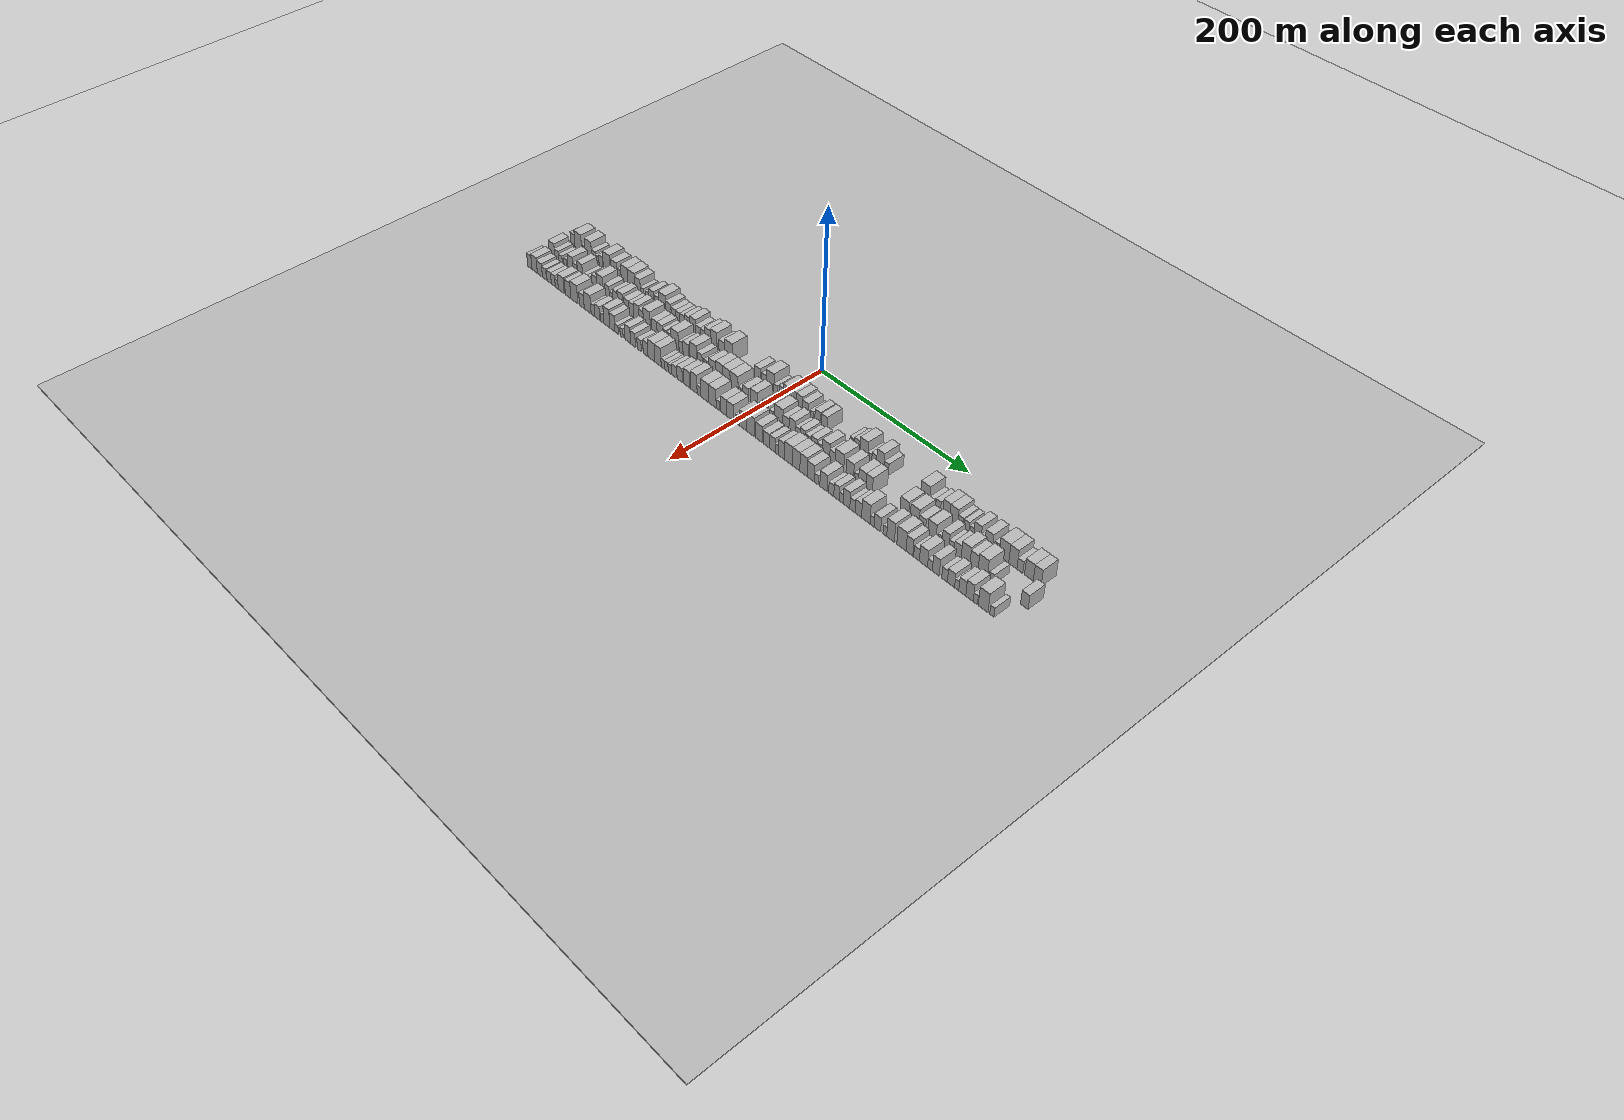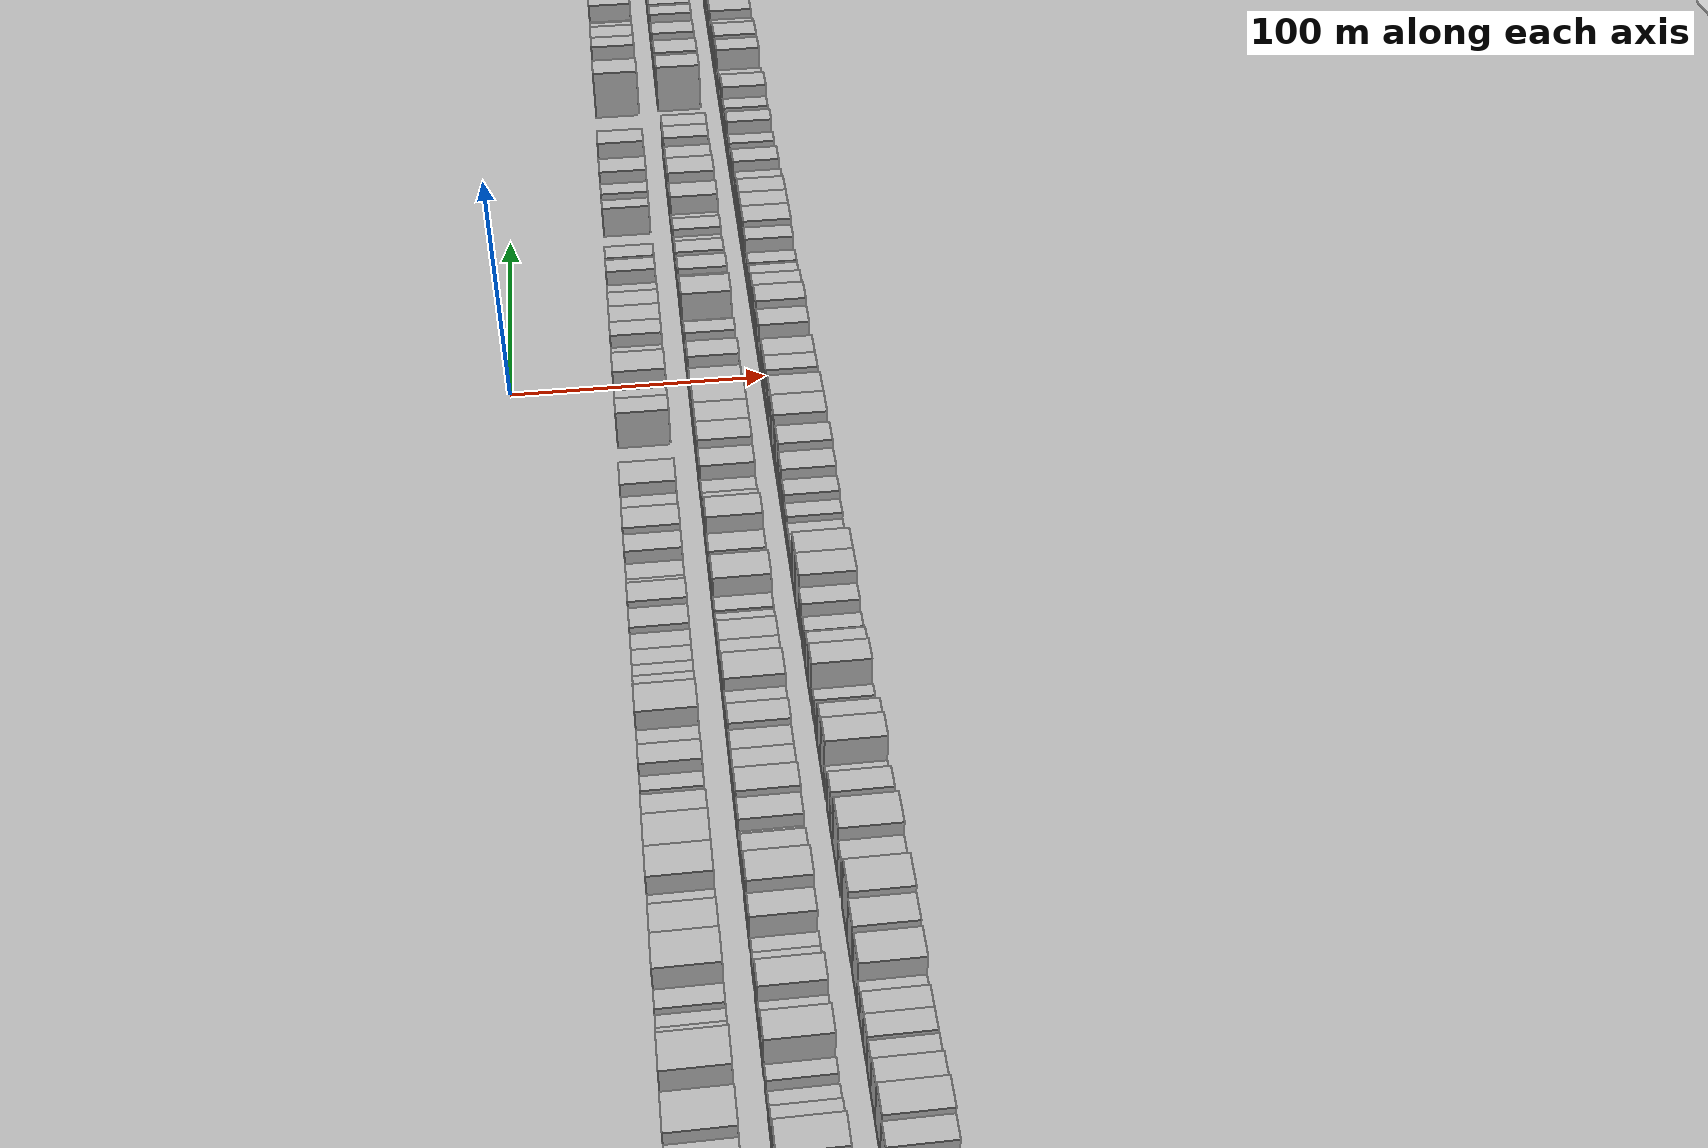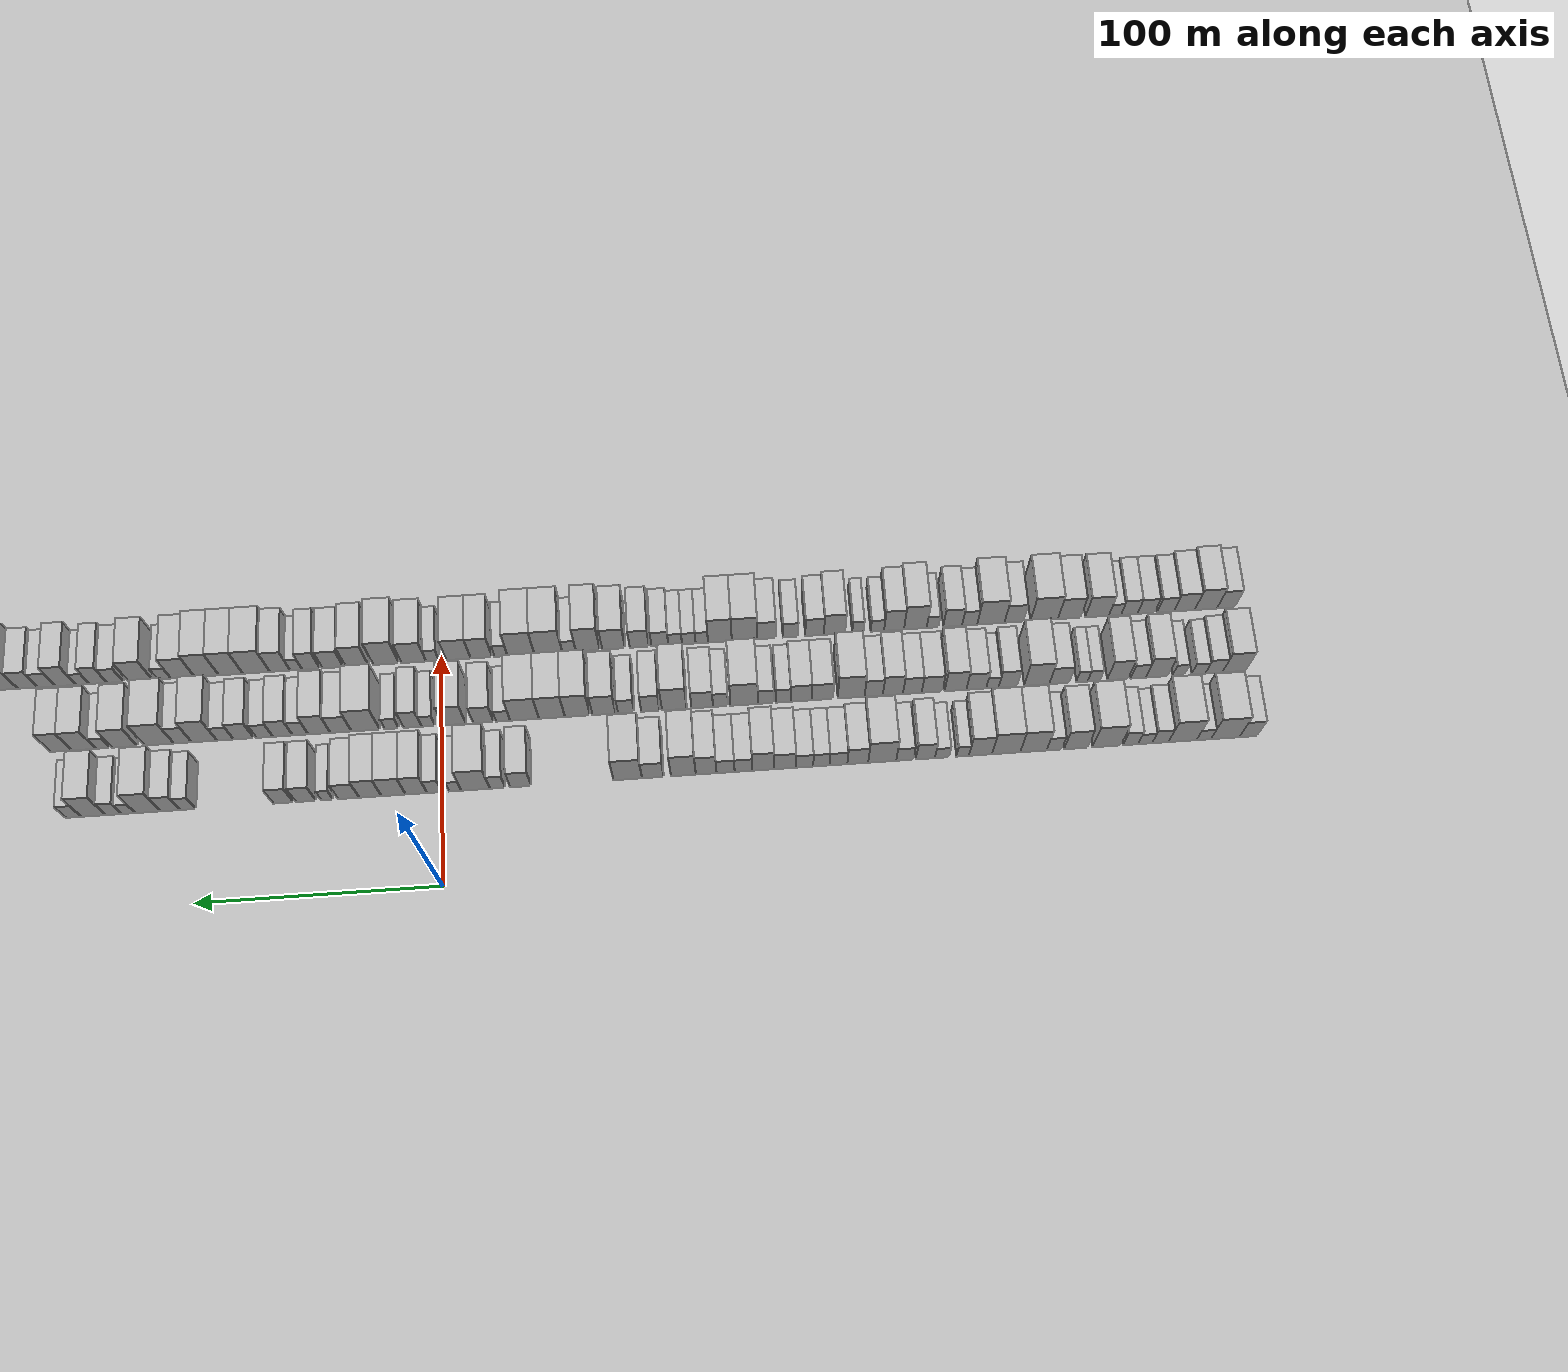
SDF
<?xml version="1.0" encoding="utf-8"?>

<sdf version="1.6">

   <world name="default">

      <gui fullscreen="0">

         <camera name="user_camera">

            <pose>-15 0 4.57585 0 0 0</pose>

            <view_controller>orbit</view_controller>

         </camera>

      </gui>

      <scene>

         <sky>

           <clouds>

             <speed>12</speed>

           </clouds>

         </sky>

         <ambient>0.4 0.4 0.4 1</ambient>

         <background>0.7 0.7 0.7 1</background>

         <shadows>1</shadows>

      </scene>

      <gravity>0 0 -9.8066</gravity>

      <magnetic_field>6e-06 2.3e-05 -4.2e-05</magnetic_field>

      <physics default="0" name="default_physics" type="ode">

         <ode>

            <solver>

               <type>quick</type>

               <iters>10</iters>

               <sor>1.0</sor>

               <use_dynamic_moi_rescaling>0</use_dynamic_moi_rescaling>

            </solver>

            <constraints>

               <cfm>0</cfm>

               <erp>0.2</erp>

               <contact_max_correcting_vel>100</contact_max_correcting_vel>

               <contact_surface_layer>0.001</contact_surface_layer>

            </constraints>

         </ode>

         <max_step_size>0.004</max_step_size>

         <real_time_factor>1</real_time_factor>

         <real_time_update_rate>250</real_time_update_rate>

      </physics>

      <light name="sun" type="directional">

         <cast_shadows>1</cast_shadows>

         <pose>0 0 10 0 0 0</pose>

         <diffuse>0.8 0.8 0.8 1</diffuse>

         <specular>0.2 0.2 0.2 1</specular>

         <attenuation>

            <range>1000</range>

            <constant>0.9</constant>

            <linear>0.01</linear>

            <quadratic>0.001</quadratic>

         </attenuation>

         <direction>-0.5 0.1 -0.9</direction>

      </light>

      <include>

         <name>ground_plane_1</name>

         <uri>model://HANNAS_ground_plane</uri>

         <pose>0 0 0  0 0 0</pose>

      </include>

      <include>

         <name>ground_plane_2</name>

         <uri>model://HANNAS_ground_plane</uri>

         <pose>100 0 0  0 0 0</pose>

      </include>

      <model name="building_1">

         <static>1</static>

         <pose frame="">50.0000 -332.3108 0 0.000000 0.000000 0.000000</pose>

         <link name="link">

            <pose frame="">0 0 9.00 0 0 0</pose>

            <collision name="collision">

               <geometry>

                  <box>

                     <size>20.0000 7.3784 18.0000</size>

                  </box>

               </geometry>

               <max_contacts>10</max_contacts>

               <surface>

                  <contact>

                     <ode/>

                  </contact>

                  <bounce/>

                  <friction>

                     <torsional>

                        <ode/>

                     </torsional>

                     <ode/>

                  </friction>

               </surface>

            </collision>

            <visual name="visual">

               <cast_shadows>0</cast_shadows>

               <geometry>

                  <box>

                     <size>20.0000 7.3784 18.0000</size>

                  </box>

               </geometry>

               <material>

                  <script>

                     <uri>model://HANNAS_wall/materials/scripts</uri>

                     <uri>model://HANNAS_wall/materials/textures</uri>

                     <name>vrc/HANNAS_wall</name>

                  </script>

               </material>

            </visual>

            <self_collide>0</self_collide>

            <enable_wind>0</enable_wind>

            <kinematic>0</kinematic>

         </link>

      </model>

      <model name="building_2">

         <static>1</static>

         <pose frame="">50.0000 -322.6757 0 0.000000 0.000000 0.000000</pose>

         <link name="link">

            <pose frame="">0 0 12.00 0 0 0</pose>

            <collision name="collision">

               <geometry>

                  <box>

                     <size>20.0000 11.8918 24.0000</size>

                  </box>

               </geometry>

               <max_contacts>10</max_contacts>

               <surface>

                  <contact>

                     <ode/>

                  </contact>

                  <bounce/>

                  <friction>

                     <torsional>

                        <ode/>

                     </torsional>

                     <ode/>

                  </friction>

               </surface>

            </collision>

            <visual name="visual">

               <cast_shadows>0</cast_shadows>

               <geometry>

                  <box>

                     <size>20.0000 11.8918 24.0000</size>

                  </box>

               </geometry>

               <material>

                  <script>

                     <uri>model://HANNAS_wall/materials/scripts</uri>

                     <uri>model://HANNAS_wall/materials/textures</uri>

                     <name>vrc/HANNAS_wall</name>

                  </script>

               </material>

            </visual>

            <self_collide>0</self_collide>

            <enable_wind>0</enable_wind>

            <kinematic>0</kinematic>

         </link>

      </model>

      <model name="building_3">

         <static>1</static>

         <pose frame="">50.0000 -313.7521 0 0.000000 0.000000 0.000000</pose>

         <link name="link">

            <pose frame="">0 0 6.00 0 0 0</pose>

            <collision name="collision">

               <geometry>

                  <box>

                     <size>20.0000 5.9555 12.0000</size>

                  </box>

               </geometry>

               <max_contacts>10</max_contacts>

               <surface>

                  <contact>

                     <ode/>

                  </contact>

                  <bounce/>

                  <friction>

                     <torsional>

                        <ode/>

                     </torsional>

                     <ode/>

                  </friction>

               </surface>

            </collision>

            <visual name="visual">

               <cast_shadows>0</cast_shadows>

               <geometry>

                  <box>

                     <size>20.0000 5.9555 12.0000</size>

                  </box>

               </geometry>

               <material>

                  <script>

                     <uri>model://HANNAS_wall/materials/scripts</uri>

                     <uri>model://HANNAS_wall/materials/textures</uri>

                     <name>vrc/HANNAS_wall</name>

                  </script>

               </material>

            </visual>

            <self_collide>0</self_collide>

            <enable_wind>0</enable_wind>

            <kinematic>0</kinematic>

         </link>

      </model>

      <model name="building_4">

         <static>1</static>

         <pose frame="">50.0000 -304.9141 0 0.000000 0.000000 0.000000</pose>

         <link name="link">

            <pose frame="">0 0 12.00 0 0 0</pose>

            <collision name="collision">

               <geometry>

                  <box>

                     <size>20.0000 11.7204 24.0000</size>

                  </box>

               </geometry>

               <max_contacts>10</max_contacts>

               <surface>

                  <contact>

                     <ode/>

                  </contact>

                  <bounce/>

                  <friction>

                     <torsional>

                        <ode/>

                     </torsional>

                     <ode/>

                  </friction>

               </surface>

            </collision>

            <visual name="visual">

               <cast_shadows>0</cast_shadows>

               <geometry>

                  <box>

                     <size>20.0000 11.7204 24.0000</size>

                  </box>

               </geometry>

               <material>

                  <script>

                     <uri>model://HANNAS_wall/materials/scripts</uri>

                     <uri>model://HANNAS_wall/materials/textures</uri>

                     <name>vrc/HANNAS_wall</name>

                  </script>

               </material>

            </visual>

            <self_collide>0</self_collide>

            <enable_wind>0</enable_wind>

            <kinematic>0</kinematic>

         </link>

      </model>

      <model name="building_5">

         <static>1</static>

         <pose frame="">50.0000 -295.6579 0 0.000000 0.000000 0.000000</pose>

         <link name="link">

            <pose frame="">0 0 7.50 0 0 0</pose>

            <collision name="collision">

               <geometry>

                  <box>

                     <size>20.0000 6.7922 15.0000</size>

                  </box>

               </geometry>

               <max_contacts>10</max_contacts>

               <surface>

                  <contact>

                     <ode/>

                  </contact>

                  <bounce/>

                  <friction>

                     <torsional>

                        <ode/>

                     </torsional>

                     <ode/>

                  </friction>

               </surface>

            </collision>

            <visual name="visual">

               <cast_shadows>0</cast_shadows>

               <geometry>

                  <box>

                     <size>20.0000 6.7922 15.0000</size>

                  </box>

               </geometry>

               <material>

                  <script>

                     <uri>model://HANNAS_wall/materials/scripts</uri>

                     <uri>model://HANNAS_wall/materials/textures</uri>

                     <name>vrc/HANNAS_wall</name>

                  </script>

               </material>

            </visual>

            <self_collide>0</self_collide>

            <enable_wind>0</enable_wind>

            <kinematic>0</kinematic>

         </link>

      </model>

      <model name="building_6">

         <static>1</static>

         <pose frame="">50.0000 -289.3308 0 0.000000 0.000000 0.000000</pose>

         <link name="link">

            <pose frame="">0 0 6.00 0 0 0</pose>

            <collision name="collision">

               <geometry>

                  <box>

                     <size>20.0000 5.8620 12.0000</size>

                  </box>

               </geometry>

               <max_contacts>10</max_contacts>

               <surface>

                  <contact>

                     <ode/>

                  </contact>

                  <bounce/>

                  <friction>

                     <torsional>

                        <ode/>

                     </torsional>

                     <ode/>

                  </friction>

               </surface>

            </collision>

            <visual name="visual">

               <cast_shadows>0</cast_shadows>

               <geometry>

                  <box>

                     <size>20.0000 5.8620 12.0000</size>

                  </box>

               </geometry>

               <material>

                  <script>

                     <uri>model://HANNAS_wall/materials/scripts</uri>

                     <uri>model://HANNAS_wall/materials/textures</uri>

                     <name>vrc/HANNAS_wall</name>

                  </script>

               </material>

            </visual>

            <self_collide>0</self_collide>

            <enable_wind>0</enable_wind>

            <kinematic>0</kinematic>

         </link>

      </model>

      <model name="building_7">

         <static>1</static>

         <pose frame="">50.0000 -283.2751 0 0.000000 0.000000 0.000000</pose>

         <link name="link">

            <pose frame="">0 0 7.50 0 0 0</pose>

            <collision name="collision">

               <geometry>

                  <box>

                     <size>20.0000 6.2495 15.0000</size>

                  </box>

               </geometry>

               <max_contacts>10</max_contacts>

               <surface>

                  <contact>

                     <ode/>

                  </contact>

                  <bounce/>

                  <friction>

                     <torsional>

                        <ode/>

                     </torsional>

                     <ode/>

                  </friction>

               </surface>

            </collision>

            <visual name="visual">

               <cast_shadows>0</cast_shadows>

               <geometry>

                  <box>

                     <size>20.0000 6.2495 15.0000</size>

                  </box>

               </geometry>

               <material>

                  <script>

                     <uri>model://HANNAS_wall/materials/scripts</uri>

                     <uri>model://HANNAS_wall/materials/textures</uri>

                     <name>vrc/HANNAS_wall</name>

                  </script>

               </material>

            </visual>

            <self_collide>0</self_collide>

            <enable_wind>0</enable_wind>

            <kinematic>0</kinematic>

         </link>

      </model>

      <model name="building_8">

         <static>1</static>

         <pose frame="">50.0000 -273.2526 0 0.000000 0.000000 0.000000</pose>

         <link name="link">

            <pose frame="">0 0 12.00 0 0 0</pose>

            <collision name="collision">

               <geometry>

                  <box>

                     <size>20.0000 11.7955 24.0000</size>

                  </box>

               </geometry>

               <max_contacts>10</max_contacts>

               <surface>

                  <contact>

                     <ode/>

                  </contact>

                  <bounce/>

                  <friction>

                     <torsional>

                        <ode/>

                     </torsional>

                     <ode/>

                  </friction>

               </surface>

            </collision>

            <visual name="visual">

               <cast_shadows>0</cast_shadows>

               <geometry>

                  <box>

                     <size>20.0000 11.7955 24.0000</size>

                  </box>

               </geometry>

               <material>

                  <script>

                     <uri>model://HANNAS_wall/materials/scripts</uri>

                     <uri>model://HANNAS_wall/materials/textures</uri>

                     <name>vrc/HANNAS_wall</name>

                  </script>

               </material>

            </visual>

            <self_collide>0</self_collide>

            <enable_wind>0</enable_wind>

            <kinematic>0</kinematic>

         </link>

      </model>

      <model name="building_9">

         <static>1</static>

         <pose frame="">50.0000 -260.4622 0 0.000000 0.000000 0.000000</pose>

         <link name="link">

            <pose frame="">0 0 10.50 0 0 0</pose>

            <collision name="collision">

               <geometry>

                  <box>

                     <size>20.0000 9.7853 21.0000</size>

                  </box>

               </geometry>

               <max_contacts>10</max_contacts>

               <surface>

                  <contact>

                     <ode/>

                  </contact>

                  <bounce/>

                  <friction>

                     <torsional>

                        <ode/>

                     </torsional>

                     <ode/>

                  </friction>

               </surface>

            </collision>

            <visual name="visual">

               <cast_shadows>0</cast_shadows>

               <geometry>

                  <box>

                     <size>20.0000 9.7853 21.0000</size>

                  </box>

               </geometry>

               <material>

                  <script>

                     <uri>model://HANNAS_wall/materials/scripts</uri>

                     <uri>model://HANNAS_wall/materials/textures</uri>

                     <name>vrc/HANNAS_wall</name>

                  </script>

               </material>

            </visual>

            <self_collide>0</self_collide>

            <enable_wind>0</enable_wind>

            <kinematic>0</kinematic>

         </link>

      </model>

      <model name="building_10">

         <static>1</static>

         <pose frame="">50.0000 -251.4611 0 0.000000 0.000000 0.000000</pose>

         <link name="link">

            <pose frame="">0 0 7.50 0 0 0</pose>

            <collision name="collision">

               <geometry>

                  <box>

                     <size>20.0000 6.2170 15.0000</size>

                  </box>

               </geometry>

               <max_contacts>10</max_contacts>

               <surface>

                  <contact>

                     <ode/>

                  </contact>

                  <bounce/>

                  <friction>

                     <torsional>

                        <ode/>

                     </torsional>

                     <ode/>

                  </friction>

               </surface>

            </collision>

            <visual name="visual">

               <cast_shadows>0</cast_shadows>

               <geometry>

                  <box>

                     <size>20.0000 6.2170 15.0000</size>

                  </box>

               </geometry>

               <material>

                  <script>

                     <uri>model://HANNAS_wall/materials/scripts</uri>

                     <uri>model://HANNAS_wall/materials/textures</uri>

                     <name>vrc/HANNAS_wall</name>

                  </script>

               </material>

            </visual>

            <self_collide>0</self_collide>

            <enable_wind>0</enable_wind>

            <kinematic>0</kinematic>

         </link>

      </model>

      <model name="building_11">

         <static>1</static>

         <pose frame="">50.0000 -242.8656 0 0.000000 0.000000 0.000000</pose>

         <link name="link">

            <pose frame="">0 0 12.00 0 0 0</pose>

            <collision name="collision">

               <geometry>

                  <box>

                     <size>20.0000 10.9740 24.0000</size>

                  </box>

               </geometry>

               <max_contacts>10</max_contacts>

               <surface>

                  <contact>

                     <ode/>

                  </contact>

                  <bounce/>

                  <friction>

                     <torsional>

                        <ode/>

                     </torsional>

                     <ode/>

                  </friction>

               </surface>

            </collision>

            <visual name="visual">

               <cast_shadows>0</cast_shadows>

               <geometry>

                  <box>

                     <size>20.0000 10.9740 24.0000</size>

                  </box>

               </geometry>

               <material>

                  <script>

                     <uri>model://HANNAS_wall/materials/scripts</uri>

                     <uri>model://HANNAS_wall/materials/textures</uri>

                     <name>vrc/HANNAS_wall</name>

                  </script>

               </material>

            </visual>

            <self_collide>0</self_collide>

            <enable_wind>0</enable_wind>

            <kinematic>0</kinematic>

         </link>

      </model>

      <model name="building_12">

         <static>1</static>

         <pose frame="">50.0000 -231.5068 0 0.000000 0.000000 0.000000</pose>

         <link name="link">

            <pose frame="">0 0 12.00 0 0 0</pose>

            <collision name="collision">

               <geometry>

                  <box>

                     <size>20.0000 11.7435 24.0000</size>

                  </box>

               </geometry>

               <max_contacts>10</max_contacts>

               <surface>

                  <contact>

                     <ode/>

                  </contact>

                  <bounce/>

                  <friction>

                     <torsional>

                        <ode/>

                     </torsional>

                     <ode/>

                  </friction>

               </surface>

            </collision>

            <visual name="visual">

               <cast_shadows>0</cast_shadows>

               <geometry>

                  <box>

                     <size>20.0000 11.7435 24.0000</size>

                  </box>

               </geometry>

               <material>

                  <script>

                     <uri>model://HANNAS_wall/materials/scripts</uri>

                     <uri>model://HANNAS_wall/materials/textures</uri>

                     <name>vrc/HANNAS_wall</name>

                  </script>

               </material>

            </visual>

            <self_collide>0</self_collide>

            <enable_wind>0</enable_wind>

            <kinematic>0</kinematic>

         </link>

      </model>

      <model name="building_13">

         <static>1</static>

         <pose frame="">50.0000 -220.8834 0 0.000000 0.000000 0.000000</pose>

         <link name="link">

            <pose frame="">0 0 10.50 0 0 0</pose>

            <collision name="collision">

               <geometry>

                  <box>

                     <size>20.0000 9.5034 21.0000</size>

                  </box>

               </geometry>

               <max_contacts>10</max_contacts>

               <surface>

                  <contact>

                     <ode/>

                  </contact>

                  <bounce/>

                  <friction>

                     <torsional>

                        <ode/>

                     </torsional>

                     <ode/>

                  </friction>

               </surface>

            </collision>

            <visual name="visual">

               <cast_shadows>0</cast_shadows>

               <geometry>

                  <box>

                     <size>20.0000 9.5034 21.0000</size>

                  </box>

               </geometry>

               <material>

                  <script>

                     <uri>model://HANNAS_wall/materials/scripts</uri>

                     <uri>model://HANNAS_wall/materials/textures</uri>

                     <name>vrc/HANNAS_wall</name>

                  </script>

               </material>

            </visual>

            <self_collide>0</self_collide>

            <enable_wind>0</enable_wind>

            <kinematic>0</kinematic>

         </link>

      </model>

      <model name="building_14">

         <static>1</static>

         <pose frame="">50.0000 -213.5074 0 0.000000 0.000000 0.000000</pose>

         <link name="link">

            <pose frame="">0 0 6.00 0 0 0</pose>

            <collision name="collision">

               <geometry>

                  <box>

                     <size>20.0000 5.2485 12.0000</size>

                  </box>

               </geometry>

               <max_contacts>10</max_contacts>

               <surface>

                  <contact>

                     <ode/>

                  </contact>

                  <bounce/>

                  <friction>

                     <torsional>

                        <ode/>

                     </torsional>

                     <ode/>

                  </friction>

               </surface>

            </collision>

            <visual name="visual">

               <cast_shadows>0</cast_shadows>

               <geometry>

                  <box>

                     <size>20.0000 5.2485 12.0000</size>

                  </box>

               </geometry>

               <material>

                  <script>

                     <uri>model://HANNAS_wall/materials/scripts</uri>

                     <uri>model://HANNAS_wall/materials/textures</uri>

                     <name>vrc/HANNAS_wall</name>

                  </script>

               </material>

            </visual>

            <self_collide>0</self_collide>

            <enable_wind>0</enable_wind>

            <kinematic>0</kinematic>

         </link>

      </model>

      <model name="building_15">

         <static>1</static>

         <pose frame="">50.0000 -204.9327 0 0.000000 0.000000 0.000000</pose>

         <link name="link">

            <pose frame="">0 0 6.00 0 0 0</pose>

            <collision name="collision">

               <geometry>

                  <box>

                     <size>20.0000 5.9009 12.0000</size>

                  </box>

               </geometry>

               <max_contacts>10</max_contacts>

               <surface>

                  <contact>

                     <ode/>

                  </contact>

                  <bounce/>

                  <friction>

                     <torsional>

                        <ode/>

                     </torsional>

                     <ode/>

                  </friction>

               </surface>

            </collision>

            <visual name="visual">

               <cast_shadows>0</cast_shadows>

               <geometry>

                  <box>

                     <size>20.0000 5.9009 12.0000</size>

                  </box>

               </geometry>

               <material>

                  <script>

                     <uri>model://HANNAS_wall/materials/scripts</uri>

                     <uri>model://HANNAS_wall/materials/textures</uri>

                     <name>vrc/HANNAS_wall</name>

                  </script>

               </material>

            </visual>

            <self_collide>0</self_collide>

            <enable_wind>0</enable_wind>

            <kinematic>0</kinematic>

         </link>

      </model>

      <model name="building_16">

         <static>1</static>

         <pose frame="">50.0000 -198.0368 0 0.000000 0.000000 0.000000</pose>

         <link name="link">

            <pose frame="">0 0 9.00 0 0 0</pose>

            <collision name="collision">

               <geometry>

                  <box>

                     <size>20.0000 7.8909 18.0000</size>

                  </box>

               </geometry>

               <max_contacts>10</max_contacts>

               <surface>

                  <contact>

                     <ode/>

                  </contact>

                  <bounce/>

                  <friction>

                     <torsional>

                        <ode/>

                     </torsional>

                     <ode/>

                  </friction>

               </surface>

            </collision>

            <visual name="visual">

               <cast_shadows>0</cast_shadows>

               <geometry>

                  <box>

                     <size>20.0000 7.8909 18.0000</size>

                  </box>

               </geometry>

               <material>

                  <script>

                     <uri>model://HANNAS_wall/materials/scripts</uri>

                     <uri>model://HANNAS_wall/materials/textures</uri>

                     <name>vrc/HANNAS_wall</name>

                  </script>

               </material>

            </visual>

            <self_collide>0</self_collide>

            <enable_wind>0</enable_wind>

            <kinematic>0</kinematic>

         </link>

      </model>

      <model name="building_17">

         <static>1</static>

         <pose frame="">50.0000 -189.5575 0 0.000000 0.000000 0.000000</pose>

         <link name="link">

            <pose frame="">0 0 7.50 0 0 0</pose>

            <collision name="collision">

               <geometry>

                  <box>

                     <size>20.0000 7.0677 15.0000</size>

                  </box>

               </geometry>

               <max_contacts>10</max_contacts>

               <surface>

                  <contact>

                     <ode/>

                  </contact>

                  <bounce/>

                  <friction>

                     <torsional>

                        <ode/>

                     </torsional>

                     <ode/>

                  </friction>

               </surface>

            </collision>

            <visual name="visual">

               <cast_shadows>0</cast_shadows>

               <geometry>

                  <box>

                     <size>20.0000 7.0677 15.0000</size>

                  </box>

               </geometry>

               <material>

                  <script>

                     <uri>model://HANNAS_wall/materials/scripts</uri>

                     <uri>model://HANNAS_wall/materials/textures</uri>

                     <name>vrc/HANNAS_wall</name>

                  </script>

               </material>

            </visual>

            <self_collide>0</self_collide>

            <enable_wind>0</enable_wind>

            <kinematic>0</kinematic>

         </link>

      </model>

      <model name="building_18">

         <static>1</static>

         <pose frame="">50.0000 -180.2230 0 0.000000 0.000000 0.000000</pose>

         <link name="link">

            <pose frame="">0 0 12.00 0 0 0</pose>

            <collision name="collision">

               <geometry>

                  <box>

                     <size>20.0000 11.6012 24.0000</size>

                  </box>

               </geometry>

               <max_contacts>10</max_contacts>

               <surface>

                  <contact>

                     <ode/>

                  </contact>

                  <bounce/>

                  <friction>

                     <torsional>

                        <ode/>

                     </torsional>

                     <ode/>

                  </friction>

               </surface>

            </collision>

            <visual name="visual">

               <cast_shadows>0</cast_shadows>

               <geometry>

                  <box>

                     <size>20.0000 11.6012 24.0000</size>

                  </box>

               </geometry>

               <material>

                  <script>

                     <uri>model://HANNAS_wall/materials/scripts</uri>

                     <uri>model://HANNAS_wall/materials/textures</uri>

                     <name>vrc/HANNAS_wall</name>

                  </script>

               </material>

            </visual>

            <self_collide>0</self_collide>

            <enable_wind>0</enable_wind>

            <kinematic>0</kinematic>

         </link>

      </model>

      <model name="building_19">

         <static>1</static>

         <pose frame="">50.0000 -170.1049 0 0.000000 0.000000 0.000000</pose>

         <link name="link">

            <pose frame="">0 0 9.00 0 0 0</pose>

            <collision name="collision">

               <geometry>

                  <box>

                     <size>20.0000 8.6351 18.0000</size>

                  </box>

               </geometry>

               <max_contacts>10</max_contacts>

               <surface>

                  <contact>

                     <ode/>

                  </contact>

                  <bounce/>

                  <friction>

                     <torsional>

                        <ode/>

                     </torsional>

                     <ode/>

                  </friction>

               </surface>

            </collision>

            <visual name="visual">

               <cast_shadows>0</cast_shadows>

               <geometry>

                  <box>

                     <size>20.0000 8.6351 18.0000</size>

                  </box>

               </geometry>

               <material>

                  <script>

                     <uri>model://HANNAS_wall/materials/scripts</uri>

                     <uri>model://HANNAS_wall/materials/textures</uri>

                     <name>vrc/HANNAS_wall</name>

                  </script>

               </material>

            </visual>

            <self_collide>0</self_collide>

            <enable_wind>0</enable_wind>

            <kinematic>0</kinematic>

         </link>

      </model>

      <model name="building_20">

         <static>1</static>

         <pose frame="">50.0000 -162.1165 0 0.000000 0.000000 0.000000</pose>

         <link name="link">

            <pose frame="">0 0 7.50 0 0 0</pose>

            <collision name="collision">

               <geometry>

                  <box>

                     <size>20.0000 7.3418 15.0000</size>

                  </box>

               </geometry>

               <max_contacts>10</max_contacts>

               <surface>

                  <contact>

                     <ode/>

                  </contact>

                  <bounce/>

                  <friction>

                     <torsional>

                        <ode/>

                     </torsional>

                     <ode/>

                  </friction>

               </surface>

            </collision>

            <visual name="visual">

               <cast_shadows>0</cast_shadows>

               <geometry>

                  <box>

                     <size>20.0000 7.3418 15.0000</size>

                  </box>

               </geometry>

               <material>

                  <script>

                     <uri>model://HANNAS_wall/materials/scripts</uri>

                     <uri>model://HANNAS_wall/materials/textures</uri>

                     <name>vrc/HANNAS_wall</name>

                  </script>

               </material>

            </visual>

            <self_collide>0</self_collide>

            <enable_wind>0</enable_wind>

            <kinematic>0</kinematic>

         </link>

      </model>

      <model name="building_21">

         <static>1</static>

         <pose frame="">50.0000 -155.0835 0 0.000000 0.000000 0.000000</pose>

         <link name="link">

            <pose frame="">0 0 7.50 0 0 0</pose>

            <collision name="collision">

               <geometry>

                  <box>

                     <size>20.0000 6.7240 15.0000</size>

                  </box>

               </geometry>

               <max_contacts>10</max_contacts>

               <surface>

                  <contact>

                     <ode/>

                  </contact>

                  <bounce/>

                  <friction>

                     <torsional>

                        <ode/>

                     </torsional>

                     <ode/>

                  </friction>

               </surface>

            </collision>

            <visual name="visual">

               <cast_shadows>0</cast_shadows>

               <geometry>

                  <box>

                     <size>20.0000 6.7240 15.0000</size>

                  </box>

               </geometry>

               <material>

                  <script>

                     <uri>model://HANNAS_wall/materials/scripts</uri>

                     <uri>model://HANNAS_wall/materials/textures</uri>

                     <name>vrc/HANNAS_wall</name>

                  </script>

               </material>

            </visual>

            <self_collide>0</self_collide>

            <enable_wind>0</enable_wind>

            <kinematic>0</kinematic>

         </link>

      </model>

      <model name="building_22">

         <static>1</static>

         <pose frame="">50.0000 -148.1666 0 0.000000 0.000000 0.000000</pose>

         <link name="link">

            <pose frame="">0 0 7.50 0 0 0</pose>

            <collision name="collision">

               <geometry>

                  <box>

                     <size>20.0000 7.1098 15.0000</size>

                  </box>

               </geometry>

               <max_contacts>10</max_contacts>

               <surface>

                  <contact>

                     <ode/>

                  </contact>

                  <bounce/>

                  <friction>

                     <torsional>

                        <ode/>

                     </torsional>

                     <ode/>

                  </friction>

               </surface>

            </collision>

            <visual name="visual">

               <cast_shadows>0</cast_shadows>

               <geometry>

                  <box>

                     <size>20.0000 7.1098 15.0000</size>

                  </box>

               </geometry>

               <material>

                  <script>

                     <uri>model://HANNAS_wall/materials/scripts</uri>

                     <uri>model://HANNAS_wall/materials/textures</uri>

                     <name>vrc/HANNAS_wall</name>

                  </script>

               </material>

            </visual>

            <self_collide>0</self_collide>

            <enable_wind>0</enable_wind>

            <kinematic>0</kinematic>

         </link>

      </model>

      <model name="building_23">

         <static>1</static>

         <pose frame="">50.0000 -140.1274 0 0.000000 0.000000 0.000000</pose>

         <link name="link">

            <pose frame="">0 0 9.00 0 0 0</pose>

            <collision name="collision">

               <geometry>

                  <box>

                     <size>20.0000 8.9688 18.0000</size>

                  </box>

               </geometry>

               <max_contacts>10</max_contacts>

               <surface>

                  <contact>

                     <ode/>

                  </contact>

                  <bounce/>

                  <friction>

                     <torsional>

                        <ode/>

                     </torsional>

                     <ode/>

                  </friction>

               </surface>

            </collision>

            <visual name="visual">

               <cast_shadows>0</cast_shadows>

               <geometry>

                  <box>

                     <size>20.0000 8.9688 18.0000</size>

                  </box>

               </geometry>

               <material>

                  <script>

                     <uri>model://HANNAS_wall/materials/scripts</uri>

                     <uri>model://HANNAS_wall/materials/textures</uri>

                     <name>vrc/HANNAS_wall</name>

                  </script>

               </material>

            </visual>

            <self_collide>0</self_collide>

            <enable_wind>0</enable_wind>

            <kinematic>0</kinematic>

         </link>

      </model>

      <model name="building_24">

         <static>1</static>

         <pose frame="">50.0000 -131.1385 0 0.000000 0.000000 0.000000</pose>

         <link name="link">

            <pose frame="">0 0 10.50 0 0 0</pose>

            <collision name="collision">

               <geometry>

                  <box>

                     <size>20.0000 9.0091 21.0000</size>

                  </box>

               </geometry>

               <max_contacts>10</max_contacts>

               <surface>

                  <contact>

                     <ode/>

                  </contact>

                  <bounce/>

                  <friction>

                     <torsional>

                        <ode/>

                     </torsional>

                     <ode/>

                  </friction>

               </surface>

            </collision>

            <visual name="visual">

               <cast_shadows>0</cast_shadows>

               <geometry>

                  <box>

                     <size>20.0000 9.0091 21.0000</size>

                  </box>

               </geometry>

               <material>

                  <script>

                     <uri>model://HANNAS_wall/materials/scripts</uri>

                     <uri>model://HANNAS_wall/materials/textures</uri>

                     <name>vrc/HANNAS_wall</name>

                  </script>

               </material>

            </visual>

            <self_collide>0</self_collide>

            <enable_wind>0</enable_wind>

            <kinematic>0</kinematic>

         </link>

      </model>

      <model name="building_25">

         <static>1</static>

         <pose frame="">50.0000 -122.9975 0 0.000000 0.000000 0.000000</pose>

         <link name="link">

            <pose frame="">0 0 7.50 0 0 0</pose>

            <collision name="collision">

               <geometry>

                  <box>

                     <size>20.0000 7.2728 15.0000</size>

                  </box>

               </geometry>

               <max_contacts>10</max_contacts>

               <surface>

                  <contact>

                     <ode/>

                  </contact>

                  <bounce/>

                  <friction>

                     <torsional>

                        <ode/>

                     </torsional>

                     <ode/>

                  </friction>

               </surface>

            </collision>

            <visual name="visual">

               <cast_shadows>0</cast_shadows>

               <geometry>

                  <box>

                     <size>20.0000 7.2728 15.0000</size>

                  </box>

               </geometry>

               <material>

                  <script>

                     <uri>model://HANNAS_wall/materials/scripts</uri>

                     <uri>model://HANNAS_wall/materials/textures</uri>

                     <name>vrc/HANNAS_wall</name>

                  </script>

               </material>

            </visual>

            <self_collide>0</self_collide>

            <enable_wind>0</enable_wind>

            <kinematic>0</kinematic>

         </link>

      </model>

      <model name="building_26">

         <static>1</static>

         <pose frame="">50.0000 -115.6475 0 0.000000 0.000000 0.000000</pose>

         <link name="link">

            <pose frame="">0 0 7.50 0 0 0</pose>

            <collision name="collision">

               <geometry>

                  <box>

                     <size>20.0000 7.4273 15.0000</size>

                  </box>

               </geometry>

               <max_contacts>10</max_contacts>

               <surface>

                  <contact>

                     <ode/>

                  </contact>

                  <bounce/>

                  <friction>

                     <torsional>

                        <ode/>

                     </torsional>

                     <ode/>

                  </friction>

               </surface>

            </collision>

            <visual name="visual">

               <cast_shadows>0</cast_shadows>

               <geometry>

                  <box>

                     <size>20.0000 7.4273 15.0000</size>

                  </box>

               </geometry>

               <material>

                  <script>

                     <uri>model://HANNAS_wall/materials/scripts</uri>

                     <uri>model://HANNAS_wall/materials/textures</uri>

                     <name>vrc/HANNAS_wall</name>

                  </script>

               </material>

            </visual>

            <self_collide>0</self_collide>

            <enable_wind>0</enable_wind>

            <kinematic>0</kinematic>

         </link>

      </model>

      <model name="building_27">

         <static>1</static>

         <pose frame="">50.0000 -107.6770 0 0.000000 0.000000 0.000000</pose>

         <link name="link">

            <pose frame="">0 0 10.50 0 0 0</pose>

            <collision name="collision">

               <geometry>

                  <box>

                     <size>20.0000 8.5136 21.0000</size>

                  </box>

               </geometry>

               <max_contacts>10</max_contacts>

               <surface>

                  <contact>

                     <ode/>

                  </contact>

                  <bounce/>

                  <friction>

                     <torsional>

                        <ode/>

                     </torsional>

                     <ode/>

                  </friction>

               </surface>

            </collision>

            <visual name="visual">

               <cast_shadows>0</cast_shadows>

               <geometry>

                  <box>

                     <size>20.0000 8.5136 21.0000</size>

                  </box>

               </geometry>

               <material>

                  <script>

                     <uri>model://HANNAS_wall/materials/scripts</uri>

                     <uri>model://HANNAS_wall/materials/textures</uri>

                     <name>vrc/HANNAS_wall</name>

                  </script>

               </material>

            </visual>

            <self_collide>0</self_collide>

            <enable_wind>0</enable_wind>

            <kinematic>0</kinematic>

         </link>

      </model>

      <model name="building_28">

         <static>1</static>

         <pose frame="">50.0000 -98.3052 0 0.000000 0.000000 0.000000</pose>

         <link name="link">

            <pose frame="">0 0 12.00 0 0 0</pose>

            <collision name="collision">

               <geometry>

                  <box>

                     <size>20.0000 10.2300 24.0000</size>

                  </box>

               </geometry>

               <max_contacts>10</max_contacts>

               <surface>

                  <contact>

                     <ode/>

                  </contact>

                  <bounce/>

                  <friction>

                     <torsional>

                        <ode/>

                     </torsional>

                     <ode/>

                  </friction>

               </surface>

            </collision>

            <visual name="visual">

               <cast_shadows>0</cast_shadows>

               <geometry>

                  <box>

                     <size>20.0000 10.2300 24.0000</size>

                  </box>

               </geometry>

               <material>

                  <script>

                     <uri>model://HANNAS_wall/materials/scripts</uri>

                     <uri>model://HANNAS_wall/materials/textures</uri>

                     <name>vrc/HANNAS_wall</name>

                  </script>

               </material>

            </visual>

            <self_collide>0</self_collide>

            <enable_wind>0</enable_wind>

            <kinematic>0</kinematic>

         </link>

      </model>

      <model name="building_29">

         <static>1</static>

         <pose frame="">50.0000 -85.7666 0 0.000000 0.000000 0.000000</pose>

         <link name="link">

            <pose frame="">0 0 9.00 0 0 0</pose>

            <collision name="collision">

               <geometry>

                  <box>

                     <size>20.0000 8.8471 18.0000</size>

                  </box>

               </geometry>

               <max_contacts>10</max_contacts>

               <surface>

                  <contact>

                     <ode/>

                  </contact>

                  <bounce/>

                  <friction>

                     <torsional>

                        <ode/>

                     </torsional>

                     <ode/>

                  </friction>

               </surface>

            </collision>

            <visual name="visual">

               <cast_shadows>0</cast_shadows>

               <geometry>

                  <box>

                     <size>20.0000 8.8471 18.0000</size>

                  </box>

               </geometry>

               <material>

                  <script>

                     <uri>model://HANNAS_wall/materials/scripts</uri>

                     <uri>model://HANNAS_wall/materials/textures</uri>

                     <name>vrc/HANNAS_wall</name>

                  </script>

               </material>

            </visual>

            <self_collide>0</self_collide>

            <enable_wind>0</enable_wind>

            <kinematic>0</kinematic>

         </link>

      </model>

      <model name="building_30">

         <static>1</static>

         <pose frame="">50.0000 -75.5026 0 0.000000 0.000000 0.000000</pose>

         <link name="link">

            <pose frame="">0 0 12.00 0 0 0</pose>

            <collision name="collision">

               <geometry>

                  <box>

                     <size>20.0000 11.6808 24.0000</size>

                  </box>

               </geometry>

               <max_contacts>10</max_contacts>

               <surface>

                  <contact>

                     <ode/>

                  </contact>

                  <bounce/>

                  <friction>

                     <torsional>

                        <ode/>

                     </torsional>

                     <ode/>

                  </friction>

               </surface>

            </collision>

            <visual name="visual">

               <cast_shadows>0</cast_shadows>

               <geometry>

                  <box>

                     <size>20.0000 11.6808 24.0000</size>

                  </box>

               </geometry>

               <material>

                  <script>

                     <uri>model://HANNAS_wall/materials/scripts</uri>

                     <uri>model://HANNAS_wall/materials/textures</uri>

                     <name>vrc/HANNAS_wall</name>

                  </script>

               </material>

            </visual>

            <self_collide>0</self_collide>

            <enable_wind>0</enable_wind>

            <kinematic>0</kinematic>

         </link>

      </model>

      <model name="building_31">

         <static>1</static>

         <pose frame="">50.0000 -31.6511 0 0.000000 0.000000 0.000000</pose>

         <link name="link">

            <pose frame="">0 0 9.00 0 0 0</pose>

            <collision name="collision">

               <geometry>

                  <box>

                     <size>20.0000 8.6741 18.0000</size>

                  </box>

               </geometry>

               <max_contacts>10</max_contacts>

               <surface>

                  <contact>

                     <ode/>

                  </contact>

                  <bounce/>

                  <friction>

                     <torsional>

                        <ode/>

                     </torsional>

                     <ode/>

                  </friction>

               </surface>

            </collision>

            <visual name="visual">

               <cast_shadows>0</cast_shadows>

               <geometry>

                  <box>

                     <size>20.0000 8.6741 18.0000</size>

                  </box>

               </geometry>

               <material>

                  <script>

                     <uri>model://HANNAS_wall/materials/scripts</uri>

                     <uri>model://HANNAS_wall/materials/textures</uri>

                     <name>vrc/HANNAS_wall</name>

                  </script>

               </material>

            </visual>

            <self_collide>0</self_collide>

            <enable_wind>0</enable_wind>

            <kinematic>0</kinematic>

         </link>

      </model>

      <model name="building_32">

         <static>1</static>

         <pose frame="">50.0000 -22.1892 0 0.000000 0.000000 0.000000</pose>

         <link name="link">

            <pose frame="">0 0 7.50 0 0 0</pose>

            <collision name="collision">

               <geometry>

                  <box>

                     <size>20.0000 6.2497 15.0000</size>

                  </box>

               </geometry>

               <max_contacts>10</max_contacts>

               <surface>

                  <contact>

                     <ode/>

                  </contact>

                  <bounce/>

                  <friction>

                     <torsional>

                        <ode/>

                     </torsional>

                     <ode/>

                  </friction>

               </surface>

            </collision>

            <visual name="visual">

               <cast_shadows>0</cast_shadows>

               <geometry>

                  <box>

                     <size>20.0000 6.2497 15.0000</size>

                  </box>

               </geometry>

               <material>

                  <script>

                     <uri>model://HANNAS_wall/materials/scripts</uri>

                     <uri>model://HANNAS_wall/materials/textures</uri>

                     <name>vrc/HANNAS_wall</name>

                  </script>

               </material>

            </visual>

            <self_collide>0</self_collide>

            <enable_wind>0</enable_wind>

            <kinematic>0</kinematic>

         </link>

      </model>

      <model name="building_33">

         <static>1</static>

         <pose frame="">50.0000 -13.2062 0 0.000000 0.000000 0.000000</pose>

         <link name="link">

            <pose frame="">0 0 12.00 0 0 0</pose>

            <collision name="collision">

               <geometry>

                  <box>

                     <size>20.0000 11.7163 24.0000</size>

                  </box>

               </geometry>

               <max_contacts>10</max_contacts>

               <surface>

                  <contact>

                     <ode/>

                  </contact>

                  <bounce/>

                  <friction>

                     <torsional>

                        <ode/>

                     </torsional>

                     <ode/>

                  </friction>

               </surface>

            </collision>

            <visual name="visual">

               <cast_shadows>0</cast_shadows>

               <geometry>

                  <box>

                     <size>20.0000 11.7163 24.0000</size>

                  </box>

               </geometry>

               <material>

                  <script>

                     <uri>model://HANNAS_wall/materials/scripts</uri>

                     <uri>model://HANNAS_wall/materials/textures</uri>

                     <name>vrc/HANNAS_wall</name>

                  </script>

               </material>

            </visual>

            <self_collide>0</self_collide>

            <enable_wind>0</enable_wind>

            <kinematic>0</kinematic>

         </link>

      </model>

      <model name="building_34">

         <static>1</static>

         <pose frame="">50.0000 -4.9149 0 0.000000 0.000000 0.000000</pose>

         <link name="link">

            <pose frame="">0 0 6.00 0 0 0</pose>

            <collision name="collision">

               <geometry>

                  <box>

                     <size>20.0000 4.8664 12.0000</size>

                  </box>

               </geometry>

               <max_contacts>10</max_contacts>

               <surface>

                  <contact>

                     <ode/>

                  </contact>

                  <bounce/>

                  <friction>

                     <torsional>

                        <ode/>

                     </torsional>

                     <ode/>

                  </friction>

               </surface>

            </collision>

            <visual name="visual">

               <cast_shadows>0</cast_shadows>

               <geometry>

                  <box>

                     <size>20.0000 4.8664 12.0000</size>

                  </box>

               </geometry>

               <material>

                  <script>

                     <uri>model://HANNAS_wall/materials/scripts</uri>

                     <uri>model://HANNAS_wall/materials/textures</uri>

                     <name>vrc/HANNAS_wall</name>

                  </script>

               </material>

            </visual>

            <self_collide>0</self_collide>

            <enable_wind>0</enable_wind>

            <kinematic>0</kinematic>

         </link>

      </model>

      <model name="building_35">

         <static>1</static>

         <pose frame="">50.0000 3.5625 0 0.000000 0.000000 0.000000</pose>

         <link name="link">

            <pose frame="">0 0 7.50 0 0 0</pose>

            <collision name="collision">

               <geometry>

                  <box>

                     <size>20.0000 6.0884 15.0000</size>

                  </box>

               </geometry>

               <max_contacts>10</max_contacts>

               <surface>

                  <contact>

                     <ode/>

                  </contact>

                  <bounce/>

                  <friction>

                     <torsional>

                        <ode/>

                     </torsional>

                     <ode/>

                  </friction>

               </surface>

            </collision>

            <visual name="visual">

               <cast_shadows>0</cast_shadows>

               <geometry>

                  <box>

                     <size>20.0000 6.0884 15.0000</size>

                  </box>

               </geometry>

               <material>

                  <script>

                     <uri>model://HANNAS_wall/materials/scripts</uri>

                     <uri>model://HANNAS_wall/materials/textures</uri>

                     <name>vrc/HANNAS_wall</name>

                  </script>

               </material>

            </visual>

            <self_collide>0</self_collide>

            <enable_wind>0</enable_wind>

            <kinematic>0</kinematic>

         </link>

      </model>

      <model name="building_36">

         <static>1</static>

         <pose frame="">50.0000 10.9737 0 0.000000 0.000000 0.000000</pose>

         <link name="link">

            <pose frame="">0 0 10.50 0 0 0</pose>

            <collision name="collision">

               <geometry>

                  <box>

                     <size>20.0000 8.7339 21.0000</size>

                  </box>

               </geometry>

               <max_contacts>10</max_contacts>

               <surface>

                  <contact>

                     <ode/>

                  </contact>

                  <bounce/>

                  <friction>

                     <torsional>

                        <ode/>

                     </torsional>

                     <ode/>

                  </friction>

               </surface>

            </collision>

            <visual name="visual">

               <cast_shadows>0</cast_shadows>

               <geometry>

                  <box>

                     <size>20.0000 8.7339 21.0000</size>

                  </box>

               </geometry>

               <material>

                  <script>

                     <uri>model://HANNAS_wall/materials/scripts</uri>

                     <uri>model://HANNAS_wall/materials/textures</uri>

                     <name>vrc/HANNAS_wall</name>

                  </script>

               </material>

            </visual>

            <self_collide>0</self_collide>

            <enable_wind>0</enable_wind>

            <kinematic>0</kinematic>

         </link>

      </model>

      <model name="building_37">

         <static>1</static>

         <pose frame="">50.0000 20.2652 0 0.000000 0.000000 0.000000</pose>

         <link name="link">

            <pose frame="">0 0 10.50 0 0 0</pose>

            <collision name="collision">

               <geometry>

                  <box>

                     <size>20.0000 9.8492 21.0000</size>

                  </box>

               </geometry>

               <max_contacts>10</max_contacts>

               <surface>

                  <contact>

                     <ode/>

                  </contact>

                  <bounce/>

                  <friction>

                     <torsional>

                        <ode/>

                     </torsional>

                     <ode/>

                  </friction>

               </surface>

            </collision>

            <visual name="visual">

               <cast_shadows>0</cast_shadows>

               <geometry>

                  <box>

                     <size>20.0000 9.8492 21.0000</size>

                  </box>

               </geometry>

               <material>

                  <script>

                     <uri>model://HANNAS_wall/materials/scripts</uri>

                     <uri>model://HANNAS_wall/materials/textures</uri>

                     <name>vrc/HANNAS_wall</name>

                  </script>

               </material>

            </visual>

            <self_collide>0</self_collide>

            <enable_wind>0</enable_wind>

            <kinematic>0</kinematic>

         </link>

      </model>

      <model name="building_38">

         <static>1</static>

         <pose frame="">50.0000 29.7162 0 0.000000 0.000000 0.000000</pose>

         <link name="link">

            <pose frame="">0 0 10.50 0 0 0</pose>

            <collision name="collision">

               <geometry>

                  <box>

                     <size>20.0000 9.0526 21.0000</size>

                  </box>

               </geometry>

               <max_contacts>10</max_contacts>

               <surface>

                  <contact>

                     <ode/>

                  </contact>

                  <bounce/>

                  <friction>

                     <torsional>

                        <ode/>

                     </torsional>

                     <ode/>

                  </friction>

               </surface>

            </collision>

            <visual name="visual">

               <cast_shadows>0</cast_shadows>

               <geometry>

                  <box>

                     <size>20.0000 9.0526 21.0000</size>

                  </box>

               </geometry>

               <material>

                  <script>

                     <uri>model://HANNAS_wall/materials/scripts</uri>

                     <uri>model://HANNAS_wall/materials/textures</uri>

                     <name>vrc/HANNAS_wall</name>

                  </script>

               </material>

            </visual>

            <self_collide>0</self_collide>

            <enable_wind>0</enable_wind>

            <kinematic>0</kinematic>

         </link>

      </model>

      <model name="building_39">

         <static>1</static>

         <pose frame="">50.0000 38.5405 0 0.000000 0.000000 0.000000</pose>

         <link name="link">

            <pose frame="">0 0 9.00 0 0 0</pose>

            <collision name="collision">

               <geometry>

                  <box>

                     <size>20.0000 8.5960 18.0000</size>

                  </box>

               </geometry>

               <max_contacts>10</max_contacts>

               <surface>

                  <contact>

                     <ode/>

                  </contact>

                  <bounce/>

                  <friction>

                     <torsional>

                        <ode/>

                     </torsional>

                     <ode/>

                  </friction>

               </surface>

            </collision>

            <visual name="visual">

               <cast_shadows>0</cast_shadows>

               <geometry>

                  <box>

                     <size>20.0000 8.5960 18.0000</size>

                  </box>

               </geometry>

               <material>

                  <script>

                     <uri>model://HANNAS_wall/materials/scripts</uri>

                     <uri>model://HANNAS_wall/materials/textures</uri>

                     <name>vrc/HANNAS_wall</name>

                  </script>

               </material>

            </visual>

            <self_collide>0</self_collide>

            <enable_wind>0</enable_wind>

            <kinematic>0</kinematic>

         </link>

      </model>

      <model name="building_40">

         <static>1</static>

         <pose frame="">50.0000 47.3137 0 0.000000 0.000000 0.000000</pose>

         <link name="link">

            <pose frame="">0 0 6.00 0 0 0</pose>

            <collision name="collision">

               <geometry>

                  <box>

                     <size>20.0000 4.9505 12.0000</size>

                  </box>

               </geometry>

               <max_contacts>10</max_contacts>

               <surface>

                  <contact>

                     <ode/>

                  </contact>

                  <bounce/>

                  <friction>

                     <torsional>

                        <ode/>

                     </torsional>

                     <ode/>

                  </friction>

               </surface>

            </collision>

            <visual name="visual">

               <cast_shadows>0</cast_shadows>

               <geometry>

                  <box>

                     <size>20.0000 4.9505 12.0000</size>

                  </box>

               </geometry>

               <material>

                  <script>

                     <uri>model://HANNAS_wall/materials/scripts</uri>

                     <uri>model://HANNAS_wall/materials/textures</uri>

                     <name>vrc/HANNAS_wall</name>

                  </script>

               </material>

            </visual>

            <self_collide>0</self_collide>

            <enable_wind>0</enable_wind>

            <kinematic>0</kinematic>

         </link>

      </model>

      <model name="building_41">

         <static>1</static>

         <pose frame="">50.0000 55.9212 0 0.000000 0.000000 0.000000</pose>

         <link name="link">

            <pose frame="">0 0 9.00 0 0 0</pose>

            <collision name="collision">

               <geometry>

                  <box>

                     <size>20.0000 8.2644 18.0000</size>

                  </box>

               </geometry>

               <max_contacts>10</max_contacts>

               <surface>

                  <contact>

                     <ode/>

                  </contact>

                  <bounce/>

                  <friction>

                     <torsional>

                        <ode/>

                     </torsional>

                     <ode/>

                  </friction>

               </surface>

            </collision>

            <visual name="visual">

               <cast_shadows>0</cast_shadows>

               <geometry>

                  <box>

                     <size>20.0000 8.2644 18.0000</size>

                  </box>

               </geometry>

               <material>

                  <script>

                     <uri>model://HANNAS_wall/materials/scripts</uri>

                     <uri>model://HANNAS_wall/materials/textures</uri>

                     <name>vrc/HANNAS_wall</name>

                  </script>

               </material>

            </visual>

            <self_collide>0</self_collide>

            <enable_wind>0</enable_wind>

            <kinematic>0</kinematic>

         </link>

      </model>

      <model name="building_42">

         <static>1</static>

         <pose frame="">50.0000 65.1122 0 0.000000 0.000000 0.000000</pose>

         <link name="link">

            <pose frame="">0 0 9.00 0 0 0</pose>

            <collision name="collision">

               <geometry>

                  <box>

                     <size>20.0000 8.1175 18.0000</size>

                  </box>

               </geometry>

               <max_contacts>10</max_contacts>

               <surface>

                  <contact>

                     <ode/>

                  </contact>

                  <bounce/>

                  <friction>

                     <torsional>

                        <ode/>

                     </torsional>

                     <ode/>

                  </friction>

               </surface>

            </collision>

            <visual name="visual">

               <cast_shadows>0</cast_shadows>

               <geometry>

                  <box>

                     <size>20.0000 8.1175 18.0000</size>

                  </box>

               </geometry>

               <material>

                  <script>

                     <uri>model://HANNAS_wall/materials/scripts</uri>

                     <uri>model://HANNAS_wall/materials/textures</uri>

                     <name>vrc/HANNAS_wall</name>

                  </script>

               </material>

            </visual>

            <self_collide>0</self_collide>

            <enable_wind>0</enable_wind>

            <kinematic>0</kinematic>

         </link>

      </model>

      <model name="building_43">

         <static>1</static>

         <pose frame="">50.0000 103.7568 0 0.000000 0.000000 0.000000</pose>

         <link name="link">

            <pose frame="">0 0 7.50 0 0 0</pose>

            <collision name="collision">

               <geometry>

                  <box>

                     <size>20.0000 6.3906 15.0000</size>

                  </box>

               </geometry>

               <max_contacts>10</max_contacts>

               <surface>

                  <contact>

                     <ode/>

                  </contact>

                  <bounce/>

                  <friction>

                     <torsional>

                        <ode/>

                     </torsional>

                     <ode/>

                  </friction>

               </surface>

            </collision>

            <visual name="visual">

               <cast_shadows>0</cast_shadows>

               <geometry>

                  <box>

                     <size>20.0000 6.3906 15.0000</size>

                  </box>

               </geometry>

               <material>

                  <script>

                     <uri>model://HANNAS_wall/materials/scripts</uri>

                     <uri>model://HANNAS_wall/materials/textures</uri>

                     <name>vrc/HANNAS_wall</name>

                  </script>

               </material>

            </visual>

            <self_collide>0</self_collide>

            <enable_wind>0</enable_wind>

            <kinematic>0</kinematic>

         </link>

      </model>

      <model name="building_44">

         <static>1</static>

         <pose frame="">50.0000 110.8456 0 0.000000 0.000000 0.000000</pose>

         <link name="link">

            <pose frame="">0 0 9.00 0 0 0</pose>

            <collision name="collision">

               <geometry>

                  <box>

                     <size>20.0000 7.7872 18.0000</size>

                  </box>

               </geometry>

               <max_contacts>10</max_contacts>

               <surface>

                  <contact>

                     <ode/>

                  </contact>

                  <bounce/>

                  <friction>

                     <torsional>

                        <ode/>

                     </torsional>

                     <ode/>

                  </friction>

               </surface>

            </collision>

            <visual name="visual">

               <cast_shadows>0</cast_shadows>

               <geometry>

                  <box>

                     <size>20.0000 7.7872 18.0000</size>

                  </box>

               </geometry>

               <material>

                  <script>

                     <uri>model://HANNAS_wall/materials/scripts</uri>

                     <uri>model://HANNAS_wall/materials/textures</uri>

                     <name>vrc/HANNAS_wall</name>

                  </script>

               </material>

            </visual>

            <self_collide>0</self_collide>

            <enable_wind>0</enable_wind>

            <kinematic>0</kinematic>

         </link>

      </model>

      <model name="building_45">

         <static>1</static>

         <pose frame="">50.0000 119.9501 0 0.000000 0.000000 0.000000</pose>

         <link name="link">

            <pose frame="">0 0 12.00 0 0 0</pose>

            <collision name="collision">

               <geometry>

                  <box>

                     <size>20.0000 10.4216 24.0000</size>

                  </box>

               </geometry>

               <max_contacts>10</max_contacts>

               <surface>

                  <contact>

                     <ode/>

                  </contact>

                  <bounce/>

                  <friction>

                     <torsional>

                        <ode/>

                     </torsional>

                     <ode/>

                  </friction>

               </surface>

            </collision>

            <visual name="visual">

               <cast_shadows>0</cast_shadows>

               <geometry>

                  <box>

                     <size>20.0000 10.4216 24.0000</size>

                  </box>

               </geometry>

               <material>

                  <script>

                     <uri>model://HANNAS_wall/materials/scripts</uri>

                     <uri>model://HANNAS_wall/materials/textures</uri>

                     <name>vrc/HANNAS_wall</name>

                  </script>

               </material>

            </visual>

            <self_collide>0</self_collide>

            <enable_wind>0</enable_wind>

            <kinematic>0</kinematic>

         </link>

      </model>

      <model name="building_46">

         <static>1</static>

         <pose frame="">50.0000 127.8922 0 0.000000 0.000000 0.000000</pose>

         <link name="link">

            <pose frame="">0 0 6.00 0 0 0</pose>

            <collision name="collision">

               <geometry>

                  <box>

                     <size>20.0000 5.4625 12.0000</size>

                  </box>

               </geometry>

               <max_contacts>10</max_contacts>

               <surface>

                  <contact>

                     <ode/>

                  </contact>

                  <bounce/>

                  <friction>

                     <torsional>

                        <ode/>

                     </torsional>

                     <ode/>

                  </friction>

               </surface>

            </collision>

            <visual name="visual">

               <cast_shadows>0</cast_shadows>

               <geometry>

                  <box>

                     <size>20.0000 5.4625 12.0000</size>

                  </box>

               </geometry>

               <material>

                  <script>

                     <uri>model://HANNAS_wall/materials/scripts</uri>

                     <uri>model://HANNAS_wall/materials/textures</uri>

                     <name>vrc/HANNAS_wall</name>

                  </script>

               </material>

            </visual>

            <self_collide>0</self_collide>

            <enable_wind>0</enable_wind>

            <kinematic>0</kinematic>

         </link>

      </model>

      <model name="building_47">

         <static>1</static>

         <pose frame="">50.0000 133.8123 0 0.000000 0.000000 0.000000</pose>

         <link name="link">

            <pose frame="">0 0 7.50 0 0 0</pose>

            <collision name="collision">

               <geometry>

                  <box>

                     <size>20.0000 6.3777 15.0000</size>

                  </box>

               </geometry>

               <max_contacts>10</max_contacts>

               <surface>

                  <contact>

                     <ode/>

                  </contact>

                  <bounce/>

                  <friction>

                     <torsional>

                        <ode/>

                     </torsional>

                     <ode/>

                  </friction>

               </surface>

            </collision>

            <visual name="visual">

               <cast_shadows>0</cast_shadows>

               <geometry>

                  <box>

                     <size>20.0000 6.3777 15.0000</size>

                  </box>

               </geometry>

               <material>

                  <script>

                     <uri>model://HANNAS_wall/materials/scripts</uri>

                     <uri>model://HANNAS_wall/materials/textures</uri>

                     <name>vrc/HANNAS_wall</name>

                  </script>

               </material>

            </visual>

            <self_collide>0</self_collide>

            <enable_wind>0</enable_wind>

            <kinematic>0</kinematic>

         </link>

      </model>

      <model name="building_48">

         <static>1</static>

         <pose frame="">50.0000 141.9819 0 0.000000 0.000000 0.000000</pose>

         <link name="link">

            <pose frame="">0 0 12.00 0 0 0</pose>

            <collision name="collision">

               <geometry>

                  <box>

                     <size>20.0000 9.9615 24.0000</size>

                  </box>

               </geometry>

               <max_contacts>10</max_contacts>

               <surface>

                  <contact>

                     <ode/>

                  </contact>

                  <bounce/>

                  <friction>

                     <torsional>

                        <ode/>

                     </torsional>

                     <ode/>

                  </friction>

               </surface>

            </collision>

            <visual name="visual">

               <cast_shadows>0</cast_shadows>

               <geometry>

                  <box>

                     <size>20.0000 9.9615 24.0000</size>

                  </box>

               </geometry>

               <material>

                  <script>

                     <uri>model://HANNAS_wall/materials/scripts</uri>

                     <uri>model://HANNAS_wall/materials/textures</uri>

                     <name>vrc/HANNAS_wall</name>

                  </script>

               </material>

            </visual>

            <self_collide>0</self_collide>

            <enable_wind>0</enable_wind>

            <kinematic>0</kinematic>

         </link>

      </model>

      <model name="building_49">

         <static>1</static>

         <pose frame="">50.0000 150.0803 0 0.000000 0.000000 0.000000</pose>

         <link name="link">

            <pose frame="">0 0 7.50 0 0 0</pose>

            <collision name="collision">

               <geometry>

                  <box>

                     <size>20.0000 6.2354 15.0000</size>

                  </box>

               </geometry>

               <max_contacts>10</max_contacts>

               <surface>

                  <contact>

                     <ode/>

                  </contact>

                  <bounce/>

                  <friction>

                     <torsional>

                        <ode/>

                     </torsional>

                     <ode/>

                  </friction>

               </surface>

            </collision>

            <visual name="visual">

               <cast_shadows>0</cast_shadows>

               <geometry>

                  <box>

                     <size>20.0000 6.2354 15.0000</size>

                  </box>

               </geometry>

               <material>

                  <script>

                     <uri>model://HANNAS_wall/materials/scripts</uri>

                     <uri>model://HANNAS_wall/materials/textures</uri>

                     <name>vrc/HANNAS_wall</name>

                  </script>

               </material>

            </visual>

            <self_collide>0</self_collide>

            <enable_wind>0</enable_wind>

            <kinematic>0</kinematic>

         </link>

      </model>

      <model name="building_50">

         <static>1</static>

         <pose frame="">50.0000 200.9176 0 0.000000 0.000000 0.000000</pose>

         <link name="link">

            <pose frame="">0 0 12.00 0 0 0</pose>

            <collision name="collision">

               <geometry>

                  <box>

                     <size>20.0000 11.8130 24.0000</size>

                  </box>

               </geometry>

               <max_contacts>10</max_contacts>

               <surface>

                  <contact>

                     <ode/>

                  </contact>

                  <bounce/>

                  <friction>

                     <torsional>

                        <ode/>

                     </torsional>

                     <ode/>

                  </friction>

               </surface>

            </collision>

            <visual name="visual">

               <cast_shadows>0</cast_shadows>

               <geometry>

                  <box>

                     <size>20.0000 11.8130 24.0000</size>

                  </box>

               </geometry>

               <material>

                  <script>

                     <uri>model://HANNAS_wall/materials/scripts</uri>

                     <uri>model://HANNAS_wall/materials/textures</uri>

                     <name>vrc/HANNAS_wall</name>

                  </script>

               </material>

            </visual>

            <self_collide>0</self_collide>

            <enable_wind>0</enable_wind>

            <kinematic>0</kinematic>

         </link>

      </model>

      <model name="building_51">

         <static>1</static>

         <pose frame="">50.0000 209.6882 0 0.000000 0.000000 0.000000</pose>

         <link name="link">

            <pose frame="">0 0 6.00 0 0 0</pose>

            <collision name="collision">

               <geometry>

                  <box>

                     <size>20.0000 5.7282 12.0000</size>

                  </box>

               </geometry>

               <max_contacts>10</max_contacts>

               <surface>

                  <contact>

                     <ode/>

                  </contact>

                  <bounce/>

                  <friction>

                     <torsional>

                        <ode/>

                     </torsional>

                     <ode/>

                  </friction>

               </surface>

            </collision>

            <visual name="visual">

               <cast_shadows>0</cast_shadows>

               <geometry>

                  <box>

                     <size>20.0000 5.7282 12.0000</size>

                  </box>

               </geometry>

               <material>

                  <script>

                     <uri>model://HANNAS_wall/materials/scripts</uri>

                     <uri>model://HANNAS_wall/materials/textures</uri>

                     <name>vrc/HANNAS_wall</name>

                  </script>

               </material>

            </visual>

            <self_collide>0</self_collide>

            <enable_wind>0</enable_wind>

            <kinematic>0</kinematic>

         </link>

      </model>

      <model name="building_52">

         <static>1</static>

         <pose frame="">50.0000 217.7186 0 0.000000 0.000000 0.000000</pose>

         <link name="link">

            <pose frame="">0 0 7.50 0 0 0</pose>

            <collision name="collision">

               <geometry>

                  <box>

                     <size>20.0000 6.3327 15.0000</size>

                  </box>

               </geometry>

               <max_contacts>10</max_contacts>

               <surface>

                  <contact>

                     <ode/>

                  </contact>

                  <bounce/>

                  <friction>

                     <torsional>

                        <ode/>

                     </torsional>

                     <ode/>

                  </friction>

               </surface>

            </collision>

            <visual name="visual">

               <cast_shadows>0</cast_shadows>

               <geometry>

                  <box>

                     <size>20.0000 6.3327 15.0000</size>

                  </box>

               </geometry>

               <material>

                  <script>

                     <uri>model://HANNAS_wall/materials/scripts</uri>

                     <uri>model://HANNAS_wall/materials/textures</uri>

                     <name>vrc/HANNAS_wall</name>

                  </script>

               </material>

            </visual>

            <self_collide>0</self_collide>

            <enable_wind>0</enable_wind>

            <kinematic>0</kinematic>

         </link>

      </model>

      <model name="building_53">

         <static>1</static>

         <pose frame="">50.0000 228.3293 0 0.000000 0.000000 0.000000</pose>

         <link name="link">

            <pose frame="">0 0 10.50 0 0 0</pose>

            <collision name="collision">

               <geometry>

                  <box>

                     <size>20.0000 8.8886 21.0000</size>

                  </box>

               </geometry>

               <max_contacts>10</max_contacts>

               <surface>

                  <contact>

                     <ode/>

                  </contact>

                  <bounce/>

                  <friction>

                     <torsional>

                        <ode/>

                     </torsional>

                     <ode/>

                  </friction>

               </surface>

            </collision>

            <visual name="visual">

               <cast_shadows>0</cast_shadows>

               <geometry>

                  <box>

                     <size>20.0000 8.8886 21.0000</size>

                  </box>

               </geometry>

               <material>

                  <script>

                     <uri>model://HANNAS_wall/materials/scripts</uri>

                     <uri>model://HANNAS_wall/materials/textures</uri>

                     <name>vrc/HANNAS_wall</name>

                  </script>

               </material>

            </visual>

            <self_collide>0</self_collide>

            <enable_wind>0</enable_wind>

            <kinematic>0</kinematic>

         </link>

      </model>

      <model name="building_54">

         <static>1</static>

         <pose frame="">50.0000 237.7962 0 0.000000 0.000000 0.000000</pose>

         <link name="link">

            <pose frame="">0 0 10.50 0 0 0</pose>

            <collision name="collision">

               <geometry>

                  <box>

                     <size>20.0000 10.0452 21.0000</size>

                  </box>

               </geometry>

               <max_contacts>10</max_contacts>

               <surface>

                  <contact>

                     <ode/>

                  </contact>

                  <bounce/>

                  <friction>

                     <torsional>

                        <ode/>

                     </torsional>

                     <ode/>

                  </friction>

               </surface>

            </collision>

            <visual name="visual">

               <cast_shadows>0</cast_shadows>

               <geometry>

                  <box>

                     <size>20.0000 10.0452 21.0000</size>

                  </box>

               </geometry>

               <material>

                  <script>

                     <uri>model://HANNAS_wall/materials/scripts</uri>

                     <uri>model://HANNAS_wall/materials/textures</uri>

                     <name>vrc/HANNAS_wall</name>

                  </script>

               </material>

            </visual>

            <self_collide>0</self_collide>

            <enable_wind>0</enable_wind>

            <kinematic>0</kinematic>

         </link>

      </model>

      <model name="building_55">

         <static>1</static>

         <pose frame="">50.0000 246.1873 0 0.000000 0.000000 0.000000</pose>

         <link name="link">

            <pose frame="">0 0 7.50 0 0 0</pose>

            <collision name="collision">

               <geometry>

                  <box>

                     <size>20.0000 6.7370 15.0000</size>

                  </box>

               </geometry>

               <max_contacts>10</max_contacts>

               <surface>

                  <contact>

                     <ode/>

                  </contact>

                  <bounce/>

                  <friction>

                     <torsional>

                        <ode/>

                     </torsional>

                     <ode/>

                  </friction>

               </surface>

            </collision>

            <visual name="visual">

               <cast_shadows>0</cast_shadows>

               <geometry>

                  <box>

                     <size>20.0000 6.7370 15.0000</size>

                  </box>

               </geometry>

               <material>

                  <script>

                     <uri>model://HANNAS_wall/materials/scripts</uri>

                     <uri>model://HANNAS_wall/materials/textures</uri>

                     <name>vrc/HANNAS_wall</name>

                  </script>

               </material>

            </visual>

            <self_collide>0</self_collide>

            <enable_wind>0</enable_wind>

            <kinematic>0</kinematic>

         </link>

      </model>

      <model name="building_56">

         <static>1</static>

         <pose frame="">50.0000 253.6301 0 0.000000 0.000000 0.000000</pose>

         <link name="link">

            <pose frame="">0 0 7.50 0 0 0</pose>

            <collision name="collision">

               <geometry>

                  <box>

                     <size>20.0000 6.1486 15.0000</size>

                  </box>

               </geometry>

               <max_contacts>10</max_contacts>

               <surface>

                  <contact>

                     <ode/>

                  </contact>

                  <bounce/>

                  <friction>

                     <torsional>

                        <ode/>

                     </torsional>

                     <ode/>

                  </friction>

               </surface>

            </collision>

            <visual name="visual">

               <cast_shadows>0</cast_shadows>

               <geometry>

                  <box>

                     <size>20.0000 6.1486 15.0000</size>

                  </box>

               </geometry>

               <material>

                  <script>

                     <uri>model://HANNAS_wall/materials/scripts</uri>

                     <uri>model://HANNAS_wall/materials/textures</uri>

                     <name>vrc/HANNAS_wall</name>

                  </script>

               </material>

            </visual>

            <self_collide>0</self_collide>

            <enable_wind>0</enable_wind>

            <kinematic>0</kinematic>

         </link>

      </model>

      <model name="building_57">

         <static>1</static>

         <pose frame="">50.0000 260.2373 0 0.000000 0.000000 0.000000</pose>

         <link name="link">

            <pose frame="">0 0 6.00 0 0 0</pose>

            <collision name="collision">

               <geometry>

                  <box>

                     <size>20.0000 5.0658 12.0000</size>

                  </box>

               </geometry>

               <max_contacts>10</max_contacts>

               <surface>

                  <contact>

                     <ode/>

                  </contact>

                  <bounce/>

                  <friction>

                     <torsional>

                        <ode/>

                     </torsional>

                     <ode/>

                  </friction>

               </surface>

            </collision>

            <visual name="visual">

               <cast_shadows>0</cast_shadows>

               <geometry>

                  <box>

                     <size>20.0000 5.0658 12.0000</size>

                  </box>

               </geometry>

               <material>

                  <script>

                     <uri>model://HANNAS_wall/materials/scripts</uri>

                     <uri>model://HANNAS_wall/materials/textures</uri>

                     <name>vrc/HANNAS_wall</name>

                  </script>

               </material>

            </visual>

            <self_collide>0</self_collide>

            <enable_wind>0</enable_wind>

            <kinematic>0</kinematic>

         </link>

      </model>

      <model name="building_58">

         <static>1</static>

         <pose frame="">50.0000 267.1651 0 0.000000 0.000000 0.000000</pose>

         <link name="link">

            <pose frame="">0 0 10.50 0 0 0</pose>

            <collision name="collision">

               <geometry>

                  <box>

                     <size>20.0000 8.7898 21.0000</size>

                  </box>

               </geometry>

               <max_contacts>10</max_contacts>

               <surface>

                  <contact>

                     <ode/>

                  </contact>

                  <bounce/>

                  <friction>

                     <torsional>

                        <ode/>

                     </torsional>

                     <ode/>

                  </friction>

               </surface>

            </collision>

            <visual name="visual">

               <cast_shadows>0</cast_shadows>

               <geometry>

                  <box>

                     <size>20.0000 8.7898 21.0000</size>

                  </box>

               </geometry>

               <material>

                  <script>

                     <uri>model://HANNAS_wall/materials/scripts</uri>

                     <uri>model://HANNAS_wall/materials/textures</uri>

                     <name>vrc/HANNAS_wall</name>

                  </script>

               </material>

            </visual>

            <self_collide>0</self_collide>

            <enable_wind>0</enable_wind>

            <kinematic>0</kinematic>

         </link>

      </model>

      <model name="building_59">

         <static>1</static>

         <pose frame="">50.0000 273.9715 0 0.000000 0.000000 0.000000</pose>

         <link name="link">

            <pose frame="">0 0 6.00 0 0 0</pose>

            <collision name="collision">

               <geometry>

                  <box>

                     <size>20.0000 4.8229 12.0000</size>

                  </box>

               </geometry>

               <max_contacts>10</max_contacts>

               <surface>

                  <contact>

                     <ode/>

                  </contact>

                  <bounce/>

                  <friction>

                     <torsional>

                        <ode/>

                     </torsional>

                     <ode/>

                  </friction>

               </surface>

            </collision>

            <visual name="visual">

               <cast_shadows>0</cast_shadows>

               <geometry>

                  <box>

                     <size>20.0000 4.8229 12.0000</size>

                  </box>

               </geometry>

               <material>

                  <script>

                     <uri>model://HANNAS_wall/materials/scripts</uri>

                     <uri>model://HANNAS_wall/materials/textures</uri>

                     <name>vrc/HANNAS_wall</name>

                  </script>

               </material>

            </visual>

            <self_collide>0</self_collide>

            <enable_wind>0</enable_wind>

            <kinematic>0</kinematic>

         </link>

      </model>

      <model name="building_60">

         <static>1</static>

         <pose frame="">50.0000 281.0614 0 0.000000 0.000000 0.000000</pose>

         <link name="link">

            <pose frame="">0 0 10.50 0 0 0</pose>

            <collision name="collision">

               <geometry>

                  <box>

                     <size>20.0000 9.3570 21.0000</size>

                  </box>

               </geometry>

               <max_contacts>10</max_contacts>

               <surface>

                  <contact>

                     <ode/>

                  </contact>

                  <bounce/>

                  <friction>

                     <torsional>

                        <ode/>

                     </torsional>

                     <ode/>

                  </friction>

               </surface>

            </collision>

            <visual name="visual">

               <cast_shadows>0</cast_shadows>

               <geometry>

                  <box>

                     <size>20.0000 9.3570 21.0000</size>

                  </box>

               </geometry>

               <material>

                  <script>

                     <uri>model://HANNAS_wall/materials/scripts</uri>

                     <uri>model://HANNAS_wall/materials/textures</uri>

                     <name>vrc/HANNAS_wall</name>

                  </script>

               </material>

            </visual>

            <self_collide>0</self_collide>

            <enable_wind>0</enable_wind>

            <kinematic>0</kinematic>

         </link>

      </model>

      <model name="building_61">

         <static>1</static>

         <pose frame="">50.0000 290.8681 0 0.000000 0.000000 0.000000</pose>

         <link name="link">

            <pose frame="">0 0 7.50 0 0 0</pose>

            <collision name="collision">

               <geometry>

                  <box>

                     <size>20.0000 6.2563 15.0000</size>

                  </box>

               </geometry>

               <max_contacts>10</max_contacts>

               <surface>

                  <contact>

                     <ode/>

                  </contact>

                  <bounce/>

                  <friction>

                     <torsional>

                        <ode/>

                     </torsional>

                     <ode/>

                  </friction>

               </surface>

            </collision>

            <visual name="visual">

               <cast_shadows>0</cast_shadows>

               <geometry>

                  <box>

                     <size>20.0000 6.2563 15.0000</size>

                  </box>

               </geometry>

               <material>

                  <script>

                     <uri>model://HANNAS_wall/materials/scripts</uri>

                     <uri>model://HANNAS_wall/materials/textures</uri>

                     <name>vrc/HANNAS_wall</name>

                  </script>

               </material>

            </visual>

            <self_collide>0</self_collide>

            <enable_wind>0</enable_wind>

            <kinematic>0</kinematic>

         </link>

      </model>

      <model name="building_62">

         <static>1</static>

         <pose frame="">50.0000 299.8954 0 0.000000 0.000000 0.000000</pose>

         <link name="link">

            <pose frame="">0 0 12.00 0 0 0</pose>

            <collision name="collision">

               <geometry>

                  <box>

                     <size>20.0000 11.7983 24.0000</size>

                  </box>

               </geometry>

               <max_contacts>10</max_contacts>

               <surface>

                  <contact>

                     <ode/>

                  </contact>

                  <bounce/>

                  <friction>

                     <torsional>

                        <ode/>

                     </torsional>

                     <ode/>

                  </friction>

               </surface>

            </collision>

            <visual name="visual">

               <cast_shadows>0</cast_shadows>

               <geometry>

                  <box>

                     <size>20.0000 11.7983 24.0000</size>

                  </box>

               </geometry>

               <material>

                  <script>

                     <uri>model://HANNAS_wall/materials/scripts</uri>

                     <uri>model://HANNAS_wall/materials/textures</uri>

                     <name>vrc/HANNAS_wall</name>

                  </script>

               </material>

            </visual>

            <self_collide>0</self_collide>

            <enable_wind>0</enable_wind>

            <kinematic>0</kinematic>

         </link>

      </model>

      <model name="building_63">

         <static>1</static>

         <pose frame="">50.0000 310.7911 0 0.000000 0.000000 0.000000</pose>

         <link name="link">

            <pose frame="">0 0 12.00 0 0 0</pose>

            <collision name="collision">

               <geometry>

                  <box>

                     <size>20.0000 9.9930 24.0000</size>

                  </box>

               </geometry>

               <max_contacts>10</max_contacts>

               <surface>

                  <contact>

                     <ode/>

                  </contact>

                  <bounce/>

                  <friction>

                     <torsional>

                        <ode/>

                     </torsional>

                     <ode/>

                  </friction>

               </surface>

            </collision>

            <visual name="visual">

               <cast_shadows>0</cast_shadows>

               <geometry>

                  <box>

                     <size>20.0000 9.9930 24.0000</size>

                  </box>

               </geometry>

               <material>

                  <script>

                     <uri>model://HANNAS_wall/materials/scripts</uri>

                     <uri>model://HANNAS_wall/materials/textures</uri>

                     <name>vrc/HANNAS_wall</name>

                  </script>

               </material>

            </visual>

            <self_collide>0</self_collide>

            <enable_wind>0</enable_wind>

            <kinematic>0</kinematic>

         </link>

      </model>

      <model name="building_64">

         <static>1</static>

         <pose frame="">50.0000 319.2852 0 0.000000 0.000000 0.000000</pose>

         <link name="link">

            <pose frame="">0 0 7.50 0 0 0</pose>

            <collision name="collision">

               <geometry>

                  <box>

                     <size>20.0000 6.9953 15.0000</size>

                  </box>

               </geometry>

               <max_contacts>10</max_contacts>

               <surface>

                  <contact>

                     <ode/>

                  </contact>

                  <bounce/>

                  <friction>

                     <torsional>

                        <ode/>

                     </torsional>

                     <ode/>

                  </friction>

               </surface>

            </collision>

            <visual name="visual">

               <cast_shadows>0</cast_shadows>

               <geometry>

                  <box>

                     <size>20.0000 6.9953 15.0000</size>

                  </box>

               </geometry>

               <material>

                  <script>

                     <uri>model://HANNAS_wall/materials/scripts</uri>

                     <uri>model://HANNAS_wall/materials/textures</uri>

                     <name>vrc/HANNAS_wall</name>

                  </script>

               </material>

            </visual>

            <self_collide>0</self_collide>

            <enable_wind>0</enable_wind>

            <kinematic>0</kinematic>

         </link>

      </model>

      <model name="building_65">

         <static>1</static>

         <pose frame="">50.0000 329.9708 0 0.000000 0.000000 0.000000</pose>

         <link name="link">

            <pose frame="">0 0 10.50 0 0 0</pose>

            <collision name="collision">

               <geometry>

                  <box>

                     <size>20.0000 10.3757 21.0000</size>

                  </box>

               </geometry>

               <max_contacts>10</max_contacts>

               <surface>

                  <contact>

                     <ode/>

                  </contact>

                  <bounce/>

                  <friction>

                     <torsional>

                        <ode/>

                     </torsional>

                     <ode/>

                  </friction>

               </surface>

            </collision>

            <visual name="visual">

               <cast_shadows>0</cast_shadows>

               <geometry>

                  <box>

                     <size>20.0000 10.3757 21.0000</size>

                  </box>

               </geometry>

               <material>

                  <script>

                     <uri>model://HANNAS_wall/materials/scripts</uri>

                     <uri>model://HANNAS_wall/materials/textures</uri>

                     <name>vrc/HANNAS_wall</name>

                  </script>

               </material>

            </visual>

            <self_collide>0</self_collide>

            <enable_wind>0</enable_wind>

            <kinematic>0</kinematic>

         </link>

      </model>

      <model name="building_66">

         <static>1</static>

         <pose frame="">50.0000 339.8101 0 0.000000 0.000000 0.000000</pose>

         <link name="link">

            <pose frame="">0 0 10.50 0 0 0</pose>

            <collision name="collision">

               <geometry>

                  <box>

                     <size>20.0000 9.3029 21.0000</size>

                  </box>

               </geometry>

               <max_contacts>10</max_contacts>

               <surface>

                  <contact>

                     <ode/>

                  </contact>

                  <bounce/>

                  <friction>

                     <torsional>

                        <ode/>

                     </torsional>

                     <ode/>

                  </friction>

               </surface>

            </collision>

            <visual name="visual">

               <cast_shadows>0</cast_shadows>

               <geometry>

                  <box>

                     <size>20.0000 9.3029 21.0000</size>

                  </box>

               </geometry>

               <material>

                  <script>

                     <uri>model://HANNAS_wall/materials/scripts</uri>

                     <uri>model://HANNAS_wall/materials/textures</uri>

                     <name>vrc/HANNAS_wall</name>

                  </script>

               </material>

            </visual>

            <self_collide>0</self_collide>

            <enable_wind>0</enable_wind>

            <kinematic>0</kinematic>

         </link>

      </model>

      <model name="building_67">

         <static>1</static>

         <pose frame="">79.0000 -331.0777 0 0.000000 0.000000 0.000000</pose>

         <link name="link">

            <pose frame="">0 0 10.50 0 0 0</pose>

            <collision name="collision">

               <geometry>

                  <box>

                     <size>20.0000 9.8445 21.0000</size>

                  </box>

               </geometry>

               <max_contacts>10</max_contacts>

               <surface>

                  <contact>

                     <ode/>

                  </contact>

                  <bounce/>

                  <friction>

                     <torsional>

                        <ode/>

                     </torsional>

                     <ode/>

                  </friction>

               </surface>

            </collision>

            <visual name="visual">

               <cast_shadows>0</cast_shadows>

               <geometry>

                  <box>

                     <size>20.0000 9.8445 21.0000</size>

                  </box>

               </geometry>

               <material>

                  <script>

                     <uri>model://HANNAS_wall/materials/scripts</uri>

                     <uri>model://HANNAS_wall/materials/textures</uri>

                     <name>vrc/HANNAS_wall</name>

                  </script>

               </material>

            </visual>

            <self_collide>0</self_collide>

            <enable_wind>0</enable_wind>

            <kinematic>0</kinematic>

         </link>

      </model>

      <model name="building_68">

         <static>1</static>

         <pose frame="">79.0000 -322.5721 0 0.000000 0.000000 0.000000</pose>

         <link name="link">

            <pose frame="">0 0 7.50 0 0 0</pose>

            <collision name="collision">

               <geometry>

                  <box>

                     <size>20.0000 7.1668 15.0000</size>

                  </box>

               </geometry>

               <max_contacts>10</max_contacts>

               <surface>

                  <contact>

                     <ode/>

                  </contact>

                  <bounce/>

                  <friction>

                     <torsional>

                        <ode/>

                     </torsional>

                     <ode/>

                  </friction>

               </surface>

            </collision>

            <visual name="visual">

               <cast_shadows>0</cast_shadows>

               <geometry>

                  <box>

                     <size>20.0000 7.1668 15.0000</size>

                  </box>

               </geometry>

               <material>

                  <script>

                     <uri>model://HANNAS_wall/materials/scripts</uri>

                     <uri>model://HANNAS_wall/materials/textures</uri>

                     <name>vrc/HANNAS_wall</name>

                  </script>

               </material>

            </visual>

            <self_collide>0</self_collide>

            <enable_wind>0</enable_wind>

            <kinematic>0</kinematic>

         </link>

      </model>

      <model name="building_69">

         <static>1</static>

         <pose frame="">79.0000 -316.0284 0 0.000000 0.000000 0.000000</pose>

         <link name="link">

            <pose frame="">0 0 6.00 0 0 0</pose>

            <collision name="collision">

               <geometry>

                  <box>

                     <size>20.0000 5.9204 12.0000</size>

                  </box>

               </geometry>

               <max_contacts>10</max_contacts>

               <surface>

                  <contact>

                     <ode/>

                  </contact>

                  <bounce/>

                  <friction>

                     <torsional>

                        <ode/>

                     </torsional>

                     <ode/>

                  </friction>

               </surface>

            </collision>

            <visual name="visual">

               <cast_shadows>0</cast_shadows>

               <geometry>

                  <box>

                     <size>20.0000 5.9204 12.0000</size>

                  </box>

               </geometry>

               <material>

                  <script>

                     <uri>model://HANNAS_wall/materials/scripts</uri>

                     <uri>model://HANNAS_wall/materials/textures</uri>

                     <name>vrc/HANNAS_wall</name>

                  </script>

               </material>

            </visual>

            <self_collide>0</self_collide>

            <enable_wind>0</enable_wind>

            <kinematic>0</kinematic>

         </link>

      </model>

      <model name="building_70">

         <static>1</static>

         <pose frame="">79.0000 -307.5376 0 0.000000 0.000000 0.000000</pose>

         <link name="link">

            <pose frame="">0 0 6.00 0 0 0</pose>

            <collision name="collision">

               <geometry>

                  <box>

                     <size>20.0000 5.0613 12.0000</size>

                  </box>

               </geometry>

               <max_contacts>10</max_contacts>

               <surface>

                  <contact>

                     <ode/>

                  </contact>

                  <bounce/>

                  <friction>

                     <torsional>

                        <ode/>

                     </torsional>

                     <ode/>

                  </friction>

               </surface>

            </collision>

            <visual name="visual">

               <cast_shadows>0</cast_shadows>

               <geometry>

                  <box>

                     <size>20.0000 5.0613 12.0000</size>

                  </box>

               </geometry>

               <material>

                  <script>

                     <uri>model://HANNAS_wall/materials/scripts</uri>

                     <uri>model://HANNAS_wall/materials/textures</uri>

                     <name>vrc/HANNAS_wall</name>

                  </script>

               </material>

            </visual>

            <self_collide>0</self_collide>

            <enable_wind>0</enable_wind>

            <kinematic>0</kinematic>

         </link>

      </model>

      <model name="building_71">

         <static>1</static>

         <pose frame="">79.0000 -298.3818 0 0.000000 0.000000 0.000000</pose>

         <link name="link">

            <pose frame="">0 0 10.50 0 0 0</pose>

            <collision name="collision">

               <geometry>

                  <box>

                     <size>20.0000 9.2502 21.0000</size>

                  </box>

               </geometry>

               <max_contacts>10</max_contacts>

               <surface>

                  <contact>

                     <ode/>

                  </contact>

                  <bounce/>

                  <friction>

                     <torsional>

                        <ode/>

                     </torsional>

                     <ode/>

                  </friction>

               </surface>

            </collision>

            <visual name="visual">

               <cast_shadows>0</cast_shadows>

               <geometry>

                  <box>

                     <size>20.0000 9.2502 21.0000</size>

                  </box>

               </geometry>

               <material>

                  <script>

                     <uri>model://HANNAS_wall/materials/scripts</uri>

                     <uri>model://HANNAS_wall/materials/textures</uri>

                     <name>vrc/HANNAS_wall</name>

                  </script>

               </material>

            </visual>

            <self_collide>0</self_collide>

            <enable_wind>0</enable_wind>

            <kinematic>0</kinematic>

         </link>

      </model>

      <model name="building_72">

         <static>1</static>

         <pose frame="">79.0000 -290.5186 0 0.000000 0.000000 0.000000</pose>

         <link name="link">

            <pose frame="">0 0 7.50 0 0 0</pose>

            <collision name="collision">

               <geometry>

                  <box>

                     <size>20.0000 6.4762 15.0000</size>

                  </box>

               </geometry>

               <max_contacts>10</max_contacts>

               <surface>

                  <contact>

                     <ode/>

                  </contact>

                  <bounce/>

                  <friction>

                     <torsional>

                        <ode/>

                     </torsional>

                     <ode/>

                  </friction>

               </surface>

            </collision>

            <visual name="visual">

               <cast_shadows>0</cast_shadows>

               <geometry>

                  <box>

                     <size>20.0000 6.4762 15.0000</size>

                  </box>

               </geometry>

               <material>

                  <script>

                     <uri>model://HANNAS_wall/materials/scripts</uri>

                     <uri>model://HANNAS_wall/materials/textures</uri>

                     <name>vrc/HANNAS_wall</name>

                  </script>

               </material>

            </visual>

            <self_collide>0</self_collide>

            <enable_wind>0</enable_wind>

            <kinematic>0</kinematic>

         </link>

      </model>

      <model name="building_73">

         <static>1</static>

         <pose frame="">79.0000 -281.8414 0 0.000000 0.000000 0.000000</pose>

         <link name="link">

            <pose frame="">0 0 10.50 0 0 0</pose>

            <collision name="collision">

               <geometry>

                  <box>

                     <size>20.0000 8.8783 21.0000</size>

                  </box>

               </geometry>

               <max_contacts>10</max_contacts>

               <surface>

                  <contact>

                     <ode/>

                  </contact>

                  <bounce/>

                  <friction>

                     <torsional>

                        <ode/>

                     </torsional>

                     <ode/>

                  </friction>

               </surface>

            </collision>

            <visual name="visual">

               <cast_shadows>0</cast_shadows>

               <geometry>

                  <box>

                     <size>20.0000 8.8783 21.0000</size>

                  </box>

               </geometry>

               <material>

                  <script>

                     <uri>model://HANNAS_wall/materials/scripts</uri>

                     <uri>model://HANNAS_wall/materials/textures</uri>

                     <name>vrc/HANNAS_wall</name>

                  </script>

               </material>

            </visual>

            <self_collide>0</self_collide>

            <enable_wind>0</enable_wind>

            <kinematic>0</kinematic>

         </link>

      </model>

      <model name="building_74">

         <static>1</static>

         <pose frame="">79.0000 -271.8258 0 0.000000 0.000000 0.000000</pose>

         <link name="link">

            <pose frame="">0 0 6.00 0 0 0</pose>

            <collision name="collision">

               <geometry>

                  <box>

                     <size>20.0000 5.1529 12.0000</size>

                  </box>

               </geometry>

               <max_contacts>10</max_contacts>

               <surface>

                  <contact>

                     <ode/>

                  </contact>

                  <bounce/>

                  <friction>

                     <torsional>

                        <ode/>

                     </torsional>

                     <ode/>

                  </friction>

               </surface>

            </collision>

            <visual name="visual">

               <cast_shadows>0</cast_shadows>

               <geometry>

                  <box>

                     <size>20.0000 5.1529 12.0000</size>

                  </box>

               </geometry>

               <material>

                  <script>

                     <uri>model://HANNAS_wall/materials/scripts</uri>

                     <uri>model://HANNAS_wall/materials/textures</uri>

                     <name>vrc/HANNAS_wall</name>

                  </script>

               </material>

            </visual>

            <self_collide>0</self_collide>

            <enable_wind>0</enable_wind>

            <kinematic>0</kinematic>

         </link>

      </model>

      <model name="building_75">

         <static>1</static>

         <pose frame="">79.0000 -266.8189 0 0.000000 0.000000 0.000000</pose>

         <link name="link">

            <pose frame="">0 0 6.00 0 0 0</pose>

            <collision name="collision">

               <geometry>

                  <box>

                     <size>20.0000 4.8611 12.0000</size>

                  </box>

               </geometry>

               <max_contacts>10</max_contacts>

               <surface>

                  <contact>

                     <ode/>

                  </contact>

                  <bounce/>

                  <friction>

                     <torsional>

                        <ode/>

                     </torsional>

                     <ode/>

                  </friction>

               </surface>

            </collision>

            <visual name="visual">

               <cast_shadows>0</cast_shadows>

               <geometry>

                  <box>

                     <size>20.0000 4.8611 12.0000</size>

                  </box>

               </geometry>

               <material>

                  <script>

                     <uri>model://HANNAS_wall/materials/scripts</uri>

                     <uri>model://HANNAS_wall/materials/textures</uri>

                     <name>vrc/HANNAS_wall</name>

                  </script>

               </material>

            </visual>

            <self_collide>0</self_collide>

            <enable_wind>0</enable_wind>

            <kinematic>0</kinematic>

         </link>

      </model>

      <model name="building_76">

         <static>1</static>

         <pose frame="">79.0000 -257.2278 0 0.000000 0.000000 0.000000</pose>

         <link name="link">

            <pose frame="">0 0 9.00 0 0 0</pose>

            <collision name="collision">

               <geometry>

                  <box>

                     <size>20.0000 8.3211 18.0000</size>

                  </box>

               </geometry>

               <max_contacts>10</max_contacts>

               <surface>

                  <contact>

                     <ode/>

                  </contact>

                  <bounce/>

                  <friction>

                     <torsional>

                        <ode/>

                     </torsional>

                     <ode/>

                  </friction>

               </surface>

            </collision>

            <visual name="visual">

               <cast_shadows>0</cast_shadows>

               <geometry>

                  <box>

                     <size>20.0000 8.3211 18.0000</size>

                  </box>

               </geometry>

               <material>

                  <script>

                     <uri>model://HANNAS_wall/materials/scripts</uri>

                     <uri>model://HANNAS_wall/materials/textures</uri>

                     <name>vrc/HANNAS_wall</name>

                  </script>

               </material>

            </visual>

            <self_collide>0</self_collide>

            <enable_wind>0</enable_wind>

            <kinematic>0</kinematic>

         </link>

      </model>

      <model name="building_77">

         <static>1</static>

         <pose frame="">79.0000 -247.7538 0 0.000000 0.000000 0.000000</pose>

         <link name="link">

            <pose frame="">0 0 12.00 0 0 0</pose>

            <collision name="collision">

               <geometry>

                  <box>

                     <size>20.0000 10.6268 24.0000</size>

                  </box>

               </geometry>

               <max_contacts>10</max_contacts>

               <surface>

                  <contact>

                     <ode/>

                  </contact>

                  <bounce/>

                  <friction>

                     <torsional>

                        <ode/>

                     </torsional>

                     <ode/>

                  </friction>

               </surface>

            </collision>

            <visual name="visual">

               <cast_shadows>0</cast_shadows>

               <geometry>

                  <box>

                     <size>20.0000 10.6268 24.0000</size>

                  </box>

               </geometry>

               <material>

                  <script>

                     <uri>model://HANNAS_wall/materials/scripts</uri>

                     <uri>model://HANNAS_wall/materials/textures</uri>

                     <name>vrc/HANNAS_wall</name>

                  </script>

               </material>

            </visual>

            <self_collide>0</self_collide>

            <enable_wind>0</enable_wind>

            <kinematic>0</kinematic>

         </link>

      </model>

      <model name="building_78">

         <static>1</static>

         <pose frame="">79.0000 -235.6024 0 0.000000 0.000000 0.000000</pose>

         <link name="link">

            <pose frame="">0 0 9.00 0 0 0</pose>

            <collision name="collision">

               <geometry>

                  <box>

                     <size>20.0000 7.6760 18.0000</size>

                  </box>

               </geometry>

               <max_contacts>10</max_contacts>

               <surface>

                  <contact>

                     <ode/>

                  </contact>

                  <bounce/>

                  <friction>

                     <torsional>

                        <ode/>

                     </torsional>

                     <ode/>

                  </friction>

               </surface>

            </collision>

            <visual name="visual">

               <cast_shadows>0</cast_shadows>

               <geometry>

                  <box>

                     <size>20.0000 7.6760 18.0000</size>

                  </box>

               </geometry>

               <material>

                  <script>

                     <uri>model://HANNAS_wall/materials/scripts</uri>

                     <uri>model://HANNAS_wall/materials/textures</uri>

                     <name>vrc/HANNAS_wall</name>

                  </script>

               </material>

            </visual>

            <self_collide>0</self_collide>

            <enable_wind>0</enable_wind>

            <kinematic>0</kinematic>

         </link>

      </model>

      <model name="building_79">

         <static>1</static>

         <pose frame="">79.0000 -229.1587 0 0.000000 0.000000 0.000000</pose>

         <link name="link">

            <pose frame="">0 0 6.00 0 0 0</pose>

            <collision name="collision">

               <geometry>

                  <box>

                     <size>20.0000 5.2114 12.0000</size>

                  </box>

               </geometry>

               <max_contacts>10</max_contacts>

               <surface>

                  <contact>

                     <ode/>

                  </contact>

                  <bounce/>

                  <friction>

                     <torsional>

                        <ode/>

                     </torsional>

                     <ode/>

                  </friction>

               </surface>

            </collision>

            <visual name="visual">

               <cast_shadows>0</cast_shadows>

               <geometry>

                  <box>

                     <size>20.0000 5.2114 12.0000</size>

                  </box>

               </geometry>

               <material>

                  <script>

                     <uri>model://HANNAS_wall/materials/scripts</uri>

                     <uri>model://HANNAS_wall/materials/textures</uri>

                     <name>vrc/HANNAS_wall</name>

                  </script>

               </material>

            </visual>

            <self_collide>0</self_collide>

            <enable_wind>0</enable_wind>

            <kinematic>0</kinematic>

         </link>

      </model>

      <model name="building_80">

         <static>1</static>

         <pose frame="">79.0000 -222.3846 0 0.000000 0.000000 0.000000</pose>

         <link name="link">

            <pose frame="">0 0 9.00 0 0 0</pose>

            <collision name="collision">

               <geometry>

                  <box>

                     <size>20.0000 8.3369 18.0000</size>

                  </box>

               </geometry>

               <max_contacts>10</max_contacts>

               <surface>

                  <contact>

                     <ode/>

                  </contact>

                  <bounce/>

                  <friction>

                     <torsional>

                        <ode/>

                     </torsional>

                     <ode/>

                  </friction>

               </surface>

            </collision>

            <visual name="visual">

               <cast_shadows>0</cast_shadows>

               <geometry>

                  <box>

                     <size>20.0000 8.3369 18.0000</size>

                  </box>

               </geometry>

               <material>

                  <script>

                     <uri>model://HANNAS_wall/materials/scripts</uri>

                     <uri>model://HANNAS_wall/materials/textures</uri>

                     <name>vrc/HANNAS_wall</name>

                  </script>

               </material>

            </visual>

            <self_collide>0</self_collide>

            <enable_wind>0</enable_wind>

            <kinematic>0</kinematic>

         </link>

      </model>

      <model name="building_81">

         <static>1</static>

         <pose frame="">79.0000 -213.6315 0 0.000000 0.000000 0.000000</pose>

         <link name="link">

            <pose frame="">0 0 10.50 0 0 0</pose>

            <collision name="collision">

               <geometry>

                  <box>

                     <size>20.0000 9.1692 21.0000</size>

                  </box>

               </geometry>

               <max_contacts>10</max_contacts>

               <surface>

                  <contact>

                     <ode/>

                  </contact>

                  <bounce/>

                  <friction>

                     <torsional>

                        <ode/>

                     </torsional>

                     <ode/>

                  </friction>

               </surface>

            </collision>

            <visual name="visual">

               <cast_shadows>0</cast_shadows>

               <geometry>

                  <box>

                     <size>20.0000 9.1692 21.0000</size>

                  </box>

               </geometry>

               <material>

                  <script>

                     <uri>model://HANNAS_wall/materials/scripts</uri>

                     <uri>model://HANNAS_wall/materials/textures</uri>

                     <name>vrc/HANNAS_wall</name>

                  </script>

               </material>

            </visual>

            <self_collide>0</self_collide>

            <enable_wind>0</enable_wind>

            <kinematic>0</kinematic>

         </link>

      </model>

      <model name="building_82">

         <static>1</static>

         <pose frame="">79.0000 -203.7266 0 0.000000 0.000000 0.000000</pose>

         <link name="link">

            <pose frame="">0 0 9.00 0 0 0</pose>

            <collision name="collision">

               <geometry>

                  <box>

                     <size>20.0000 8.6408 18.0000</size>

                  </box>

               </geometry>

               <max_contacts>10</max_contacts>

               <surface>

                  <contact>

                     <ode/>

                  </contact>

                  <bounce/>

                  <friction>

                     <torsional>

                        <ode/>

                     </torsional>

                     <ode/>

                  </friction>

               </surface>

            </collision>

            <visual name="visual">

               <cast_shadows>0</cast_shadows>

               <geometry>

                  <box>

                     <size>20.0000 8.6408 18.0000</size>

                  </box>

               </geometry>

               <material>

                  <script>

                     <uri>model://HANNAS_wall/materials/scripts</uri>

                     <uri>model://HANNAS_wall/materials/textures</uri>

                     <name>vrc/HANNAS_wall</name>

                  </script>

               </material>

            </visual>

            <self_collide>0</self_collide>

            <enable_wind>0</enable_wind>

            <kinematic>0</kinematic>

         </link>

      </model>

      <model name="building_83">

         <static>1</static>

         <pose frame="">79.0000 -195.5025 0 0.000000 0.000000 0.000000</pose>

         <link name="link">

            <pose frame="">0 0 9.00 0 0 0</pose>

            <collision name="collision">

               <geometry>

                  <box>

                     <size>20.0000 7.8075 18.0000</size>

                  </box>

               </geometry>

               <max_contacts>10</max_contacts>

               <surface>

                  <contact>

                     <ode/>

                  </contact>

                  <bounce/>

                  <friction>

                     <torsional>

                        <ode/>

                     </torsional>

                     <ode/>

                  </friction>

               </surface>

            </collision>

            <visual name="visual">

               <cast_shadows>0</cast_shadows>

               <geometry>

                  <box>

                     <size>20.0000 7.8075 18.0000</size>

                  </box>

               </geometry>

               <material>

                  <script>

                     <uri>model://HANNAS_wall/materials/scripts</uri>

                     <uri>model://HANNAS_wall/materials/textures</uri>

                     <name>vrc/HANNAS_wall</name>

                  </script>

               </material>

            </visual>

            <self_collide>0</self_collide>

            <enable_wind>0</enable_wind>

            <kinematic>0</kinematic>

         </link>

      </model>

      <model name="building_84">

         <static>1</static>

         <pose frame="">79.0000 -187.3815 0 0.000000 0.000000 0.000000</pose>

         <link name="link">

            <pose frame="">0 0 10.50 0 0 0</pose>

            <collision name="collision">

               <geometry>

                  <box>

                     <size>20.0000 8.4344 21.0000</size>

                  </box>

               </geometry>

               <max_contacts>10</max_contacts>

               <surface>

                  <contact>

                     <ode/>

                  </contact>

                  <bounce/>

                  <friction>

                     <torsional>

                        <ode/>

                     </torsional>

                     <ode/>

                  </friction>

               </surface>

            </collision>

            <visual name="visual">

               <cast_shadows>0</cast_shadows>

               <geometry>

                  <box>

                     <size>20.0000 8.4344 21.0000</size>

                  </box>

               </geometry>

               <material>

                  <script>

                     <uri>model://HANNAS_wall/materials/scripts</uri>

                     <uri>model://HANNAS_wall/materials/textures</uri>

                     <name>vrc/HANNAS_wall</name>

                  </script>

               </material>

            </visual>

            <self_collide>0</self_collide>

            <enable_wind>0</enable_wind>

            <kinematic>0</kinematic>

         </link>

      </model>

      <model name="building_85">

         <static>1</static>

         <pose frame="">79.0000 -179.3640 0 0.000000 0.000000 0.000000</pose>

         <link name="link">

            <pose frame="">0 0 9.00 0 0 0</pose>

            <collision name="collision">

               <geometry>

                  <box>

                     <size>20.0000 7.6006 18.0000</size>

                  </box>

               </geometry>

               <max_contacts>10</max_contacts>

               <surface>

                  <contact>

                     <ode/>

                  </contact>

                  <bounce/>

                  <friction>

                     <torsional>

                        <ode/>

                     </torsional>

                     <ode/>

                  </friction>

               </surface>

            </collision>

            <visual name="visual">

               <cast_shadows>0</cast_shadows>

               <geometry>

                  <box>

                     <size>20.0000 7.6006 18.0000</size>

                  </box>

               </geometry>

               <material>

                  <script>

                     <uri>model://HANNAS_wall/materials/scripts</uri>

                     <uri>model://HANNAS_wall/materials/textures</uri>

                     <name>vrc/HANNAS_wall</name>

                  </script>

               </material>

            </visual>

            <self_collide>0</self_collide>

            <enable_wind>0</enable_wind>

            <kinematic>0</kinematic>

         </link>

      </model>

      <model name="building_86">

         <static>1</static>

         <pose frame="">79.0000 -169.9344 0 0.000000 0.000000 0.000000</pose>

         <link name="link">

            <pose frame="">0 0 12.00 0 0 0</pose>

            <collision name="collision">

               <geometry>

                  <box>

                     <size>20.0000 11.2585 24.0000</size>

                  </box>

               </geometry>

               <max_contacts>10</max_contacts>

               <surface>

                  <contact>

                     <ode/>

                  </contact>

                  <bounce/>

                  <friction>

                     <torsional>

                        <ode/>

                     </torsional>

                     <ode/>

                  </friction>

               </surface>

            </collision>

            <visual name="visual">

               <cast_shadows>0</cast_shadows>

               <geometry>

                  <box>

                     <size>20.0000 11.2585 24.0000</size>

                  </box>

               </geometry>

               <material>

                  <script>

                     <uri>model://HANNAS_wall/materials/scripts</uri>

                     <uri>model://HANNAS_wall/materials/textures</uri>

                     <name>vrc/HANNAS_wall</name>

                  </script>

               </material>

            </visual>

            <self_collide>0</self_collide>

            <enable_wind>0</enable_wind>

            <kinematic>0</kinematic>

         </link>

      </model>

      <model name="building_87">

         <static>1</static>

         <pose frame="">79.0000 -157.8646 0 0.000000 0.000000 0.000000</pose>

         <link name="link">

            <pose frame="">0 0 9.00 0 0 0</pose>

            <collision name="collision">

               <geometry>

                  <box>

                     <size>20.0000 8.8811 18.0000</size>

                  </box>

               </geometry>

               <max_contacts>10</max_contacts>

               <surface>

                  <contact>

                     <ode/>

                  </contact>

                  <bounce/>

                  <friction>

                     <torsional>

                        <ode/>

                     </torsional>

                     <ode/>

                  </friction>

               </surface>

            </collision>

            <visual name="visual">

               <cast_shadows>0</cast_shadows>

               <geometry>

                  <box>

                     <size>20.0000 8.8811 18.0000</size>

                  </box>

               </geometry>

               <material>

                  <script>

                     <uri>model://HANNAS_wall/materials/scripts</uri>

                     <uri>model://HANNAS_wall/materials/textures</uri>

                     <name>vrc/HANNAS_wall</name>

                  </script>

               </material>

            </visual>

            <self_collide>0</self_collide>

            <enable_wind>0</enable_wind>

            <kinematic>0</kinematic>

         </link>

      </model>

      <model name="building_88">

         <static>1</static>

         <pose frame="">79.0000 -149.0118 0 0.000000 0.000000 0.000000</pose>

         <link name="link">

            <pose frame="">0 0 9.00 0 0 0</pose>

            <collision name="collision">

               <geometry>

                  <box>

                     <size>20.0000 8.8245 18.0000</size>

                  </box>

               </geometry>

               <max_contacts>10</max_contacts>

               <surface>

                  <contact>

                     <ode/>

                  </contact>

                  <bounce/>

                  <friction>

                     <torsional>

                        <ode/>

                     </torsional>

                     <ode/>

                  </friction>

               </surface>

            </collision>

            <visual name="visual">

               <cast_shadows>0</cast_shadows>

               <geometry>

                  <box>

                     <size>20.0000 8.8245 18.0000</size>

                  </box>

               </geometry>

               <material>

                  <script>

                     <uri>model://HANNAS_wall/materials/scripts</uri>

                     <uri>model://HANNAS_wall/materials/textures</uri>

                     <name>vrc/HANNAS_wall</name>

                  </script>

               </material>

            </visual>

            <self_collide>0</self_collide>

            <enable_wind>0</enable_wind>

            <kinematic>0</kinematic>

         </link>

      </model>

      <model name="building_89">

         <static>1</static>

         <pose frame="">79.0000 -141.5870 0 0.000000 0.000000 0.000000</pose>

         <link name="link">

            <pose frame="">0 0 7.50 0 0 0</pose>

            <collision name="collision">

               <geometry>

                  <box>

                     <size>20.0000 6.0252 15.0000</size>

                  </box>

               </geometry>

               <max_contacts>10</max_contacts>

               <surface>

                  <contact>

                     <ode/>

                  </contact>

                  <bounce/>

                  <friction>

                     <torsional>

                        <ode/>

                     </torsional>

                     <ode/>

                  </friction>

               </surface>

            </collision>

            <visual name="visual">

               <cast_shadows>0</cast_shadows>

               <geometry>

                  <box>

                     <size>20.0000 6.0252 15.0000</size>

                  </box>

               </geometry>

               <material>

                  <script>

                     <uri>model://HANNAS_wall/materials/scripts</uri>

                     <uri>model://HANNAS_wall/materials/textures</uri>

                     <name>vrc/HANNAS_wall</name>

                  </script>

               </material>

            </visual>

            <self_collide>0</self_collide>

            <enable_wind>0</enable_wind>

            <kinematic>0</kinematic>

         </link>

      </model>

      <model name="building_90">

         <static>1</static>

         <pose frame="">79.0000 -134.2580 0 0.000000 0.000000 0.000000</pose>

         <link name="link">

            <pose frame="">0 0 7.50 0 0 0</pose>

            <collision name="collision">

               <geometry>

                  <box>

                     <size>20.0000 6.6327 15.0000</size>

                  </box>

               </geometry>

               <max_contacts>10</max_contacts>

               <surface>

                  <contact>

                     <ode/>

                  </contact>

                  <bounce/>

                  <friction>

                     <torsional>

                        <ode/>

                     </torsional>

                     <ode/>

                  </friction>

               </surface>

            </collision>

            <visual name="visual">

               <cast_shadows>0</cast_shadows>

               <geometry>

                  <box>

                     <size>20.0000 6.6327 15.0000</size>

                  </box>

               </geometry>

               <material>

                  <script>

                     <uri>model://HANNAS_wall/materials/scripts</uri>

                     <uri>model://HANNAS_wall/materials/textures</uri>

                     <name>vrc/HANNAS_wall</name>

                  </script>

               </material>

            </visual>

            <self_collide>0</self_collide>

            <enable_wind>0</enable_wind>

            <kinematic>0</kinematic>

         </link>

      </model>

      <model name="building_91">

         <static>1</static>

         <pose frame="">79.0000 -125.2191 0 0.000000 0.000000 0.000000</pose>

         <link name="link">

            <pose frame="">0 0 12.00 0 0 0</pose>

            <collision name="collision">

               <geometry>

                  <box>

                     <size>20.0000 11.4452 24.0000</size>

                  </box>

               </geometry>

               <max_contacts>10</max_contacts>

               <surface>

                  <contact>

                     <ode/>

                  </contact>

                  <bounce/>

                  <friction>

                     <torsional>

                        <ode/>

                     </torsional>

                     <ode/>

                  </friction>

               </surface>

            </collision>

            <visual name="visual">

               <cast_shadows>0</cast_shadows>

               <geometry>

                  <box>

                     <size>20.0000 11.4452 24.0000</size>

                  </box>

               </geometry>

               <material>

                  <script>

                     <uri>model://HANNAS_wall/materials/scripts</uri>

                     <uri>model://HANNAS_wall/materials/textures</uri>

                     <name>vrc/HANNAS_wall</name>

                  </script>

               </material>

            </visual>

            <self_collide>0</self_collide>

            <enable_wind>0</enable_wind>

            <kinematic>0</kinematic>

         </link>

      </model>

      <model name="building_92">

         <static>1</static>

         <pose frame="">79.0000 -115.3726 0 0.000000 0.000000 0.000000</pose>

         <link name="link">

            <pose frame="">0 0 7.50 0 0 0</pose>

            <collision name="collision">

               <geometry>

                  <box>

                     <size>20.0000 6.2477 15.0000</size>

                  </box>

               </geometry>

               <max_contacts>10</max_contacts>

               <surface>

                  <contact>

                     <ode/>

                  </contact>

                  <bounce/>

                  <friction>

                     <torsional>

                        <ode/>

                     </torsional>

                     <ode/>

                  </friction>

               </surface>

            </collision>

            <visual name="visual">

               <cast_shadows>0</cast_shadows>

               <geometry>

                  <box>

                     <size>20.0000 6.2477 15.0000</size>

                  </box>

               </geometry>

               <material>

                  <script>

                     <uri>model://HANNAS_wall/materials/scripts</uri>

                     <uri>model://HANNAS_wall/materials/textures</uri>

                     <name>vrc/HANNAS_wall</name>

                  </script>

               </material>

            </visual>

            <self_collide>0</self_collide>

            <enable_wind>0</enable_wind>

            <kinematic>0</kinematic>

         </link>

      </model>

      <model name="building_93">

         <static>1</static>

         <pose frame="">79.0000 -107.7630 0 0.000000 0.000000 0.000000</pose>

         <link name="link">

            <pose frame="">0 0 9.00 0 0 0</pose>

            <collision name="collision">

               <geometry>

                  <box>

                     <size>20.0000 8.9715 18.0000</size>

                  </box>

               </geometry>

               <max_contacts>10</max_contacts>

               <surface>

                  <contact>

                     <ode/>

                  </contact>

                  <bounce/>

                  <friction>

                     <torsional>

                        <ode/>

                     </torsional>

                     <ode/>

                  </friction>

               </surface>

            </collision>

            <visual name="visual">

               <cast_shadows>0</cast_shadows>

               <geometry>

                  <box>

                     <size>20.0000 8.9715 18.0000</size>

                  </box>

               </geometry>

               <material>

                  <script>

                     <uri>model://HANNAS_wall/materials/scripts</uri>

                     <uri>model://HANNAS_wall/materials/textures</uri>

                     <name>vrc/HANNAS_wall</name>

                  </script>

               </material>

            </visual>

            <self_collide>0</self_collide>

            <enable_wind>0</enable_wind>

            <kinematic>0</kinematic>

         </link>

      </model>

      <model name="building_94">

         <static>1</static>

         <pose frame="">79.0000 -96.1327 0 0.000000 0.000000 0.000000</pose>

         <link name="link">

            <pose frame="">0 0 12.00 0 0 0</pose>

            <collision name="collision">

               <geometry>

                  <box>

                     <size>20.0000 10.2889 24.0000</size>

                  </box>

               </geometry>

               <max_contacts>10</max_contacts>

               <surface>

                  <contact>

                     <ode/>

                  </contact>

                  <bounce/>

                  <friction>

                     <torsional>

                        <ode/>

                     </torsional>

                     <ode/>

                  </friction>

               </surface>

            </collision>

            <visual name="visual">

               <cast_shadows>0</cast_shadows>

               <geometry>

                  <box>

                     <size>20.0000 10.2889 24.0000</size>

                  </box>

               </geometry>

               <material>

                  <script>

                     <uri>model://HANNAS_wall/materials/scripts</uri>

                     <uri>model://HANNAS_wall/materials/textures</uri>

                     <name>vrc/HANNAS_wall</name>

                  </script>

               </material>

            </visual>

            <self_collide>0</self_collide>

            <enable_wind>0</enable_wind>

            <kinematic>0</kinematic>

         </link>

      </model>

      <model name="building_95">

         <static>1</static>

         <pose frame="">79.0000 -86.2134 0 0.000000 0.000000 0.000000</pose>

         <link name="link">

            <pose frame="">0 0 9.00 0 0 0</pose>

            <collision name="collision">

               <geometry>

                  <box>

                     <size>20.0000 7.5497 18.0000</size>

                  </box>

               </geometry>

               <max_contacts>10</max_contacts>

               <surface>

                  <contact>

                     <ode/>

                  </contact>

                  <bounce/>

                  <friction>

                     <torsional>

                        <ode/>

                     </torsional>

                     <ode/>

                  </friction>

               </surface>

            </collision>

            <visual name="visual">

               <cast_shadows>0</cast_shadows>

               <geometry>

                  <box>

                     <size>20.0000 7.5497 18.0000</size>

                  </box>

               </geometry>

               <material>

                  <script>

                     <uri>model://HANNAS_wall/materials/scripts</uri>

                     <uri>model://HANNAS_wall/materials/textures</uri>

                     <name>vrc/HANNAS_wall</name>

                  </script>

               </material>

            </visual>

            <self_collide>0</self_collide>

            <enable_wind>0</enable_wind>

            <kinematic>0</kinematic>

         </link>

      </model>

      <model name="building_96">

         <static>1</static>

         <pose frame="">79.0000 -76.0758 0 0.000000 0.000000 0.000000</pose>

         <link name="link">

            <pose frame="">0 0 7.50 0 0 0</pose>

            <collision name="collision">

               <geometry>

                  <box>

                     <size>20.0000 6.7255 15.0000</size>

                  </box>

               </geometry>

               <max_contacts>10</max_contacts>

               <surface>

                  <contact>

                     <ode/>

                  </contact>

                  <bounce/>

                  <friction>

                     <torsional>

                        <ode/>

                     </torsional>

                     <ode/>

                  </friction>

               </surface>

            </collision>

            <visual name="visual">

               <cast_shadows>0</cast_shadows>

               <geometry>

                  <box>

                     <size>20.0000 6.7255 15.0000</size>

                  </box>

               </geometry>

               <material>

                  <script>

                     <uri>model://HANNAS_wall/materials/scripts</uri>

                     <uri>model://HANNAS_wall/materials/textures</uri>

                     <name>vrc/HANNAS_wall</name>

                  </script>

               </material>

            </visual>

            <self_collide>0</self_collide>

            <enable_wind>0</enable_wind>

            <kinematic>0</kinematic>

         </link>

      </model>

      <model name="building_97">

         <static>1</static>

         <pose frame="">79.0000 -66.9052 0 0.000000 0.000000 0.000000</pose>

         <link name="link">

            <pose frame="">0 0 10.50 0 0 0</pose>

            <collision name="collision">

               <geometry>

                  <box>

                     <size>20.0000 9.6157 21.0000</size>

                  </box>

               </geometry>

               <max_contacts>10</max_contacts>

               <surface>

                  <contact>

                     <ode/>

                  </contact>

                  <bounce/>

                  <friction>

                     <torsional>

                        <ode/>

                     </torsional>

                     <ode/>

                  </friction>

               </surface>

            </collision>

            <visual name="visual">

               <cast_shadows>0</cast_shadows>

               <geometry>

                  <box>

                     <size>20.0000 9.6157 21.0000</size>

                  </box>

               </geometry>

               <material>

                  <script>

                     <uri>model://HANNAS_wall/materials/scripts</uri>

                     <uri>model://HANNAS_wall/materials/textures</uri>

                     <name>vrc/HANNAS_wall</name>

                  </script>

               </material>

            </visual>

            <self_collide>0</self_collide>

            <enable_wind>0</enable_wind>

            <kinematic>0</kinematic>

         </link>

      </model>

      <model name="building_98">

         <static>1</static>

         <pose frame="">79.0000 -55.8953 0 0.000000 0.000000 0.000000</pose>

         <link name="link">

            <pose frame="">0 0 12.00 0 0 0</pose>

            <collision name="collision">

               <geometry>

                  <box>

                     <size>20.0000 10.4041 24.0000</size>

                  </box>

               </geometry>

               <max_contacts>10</max_contacts>

               <surface>

                  <contact>

                     <ode/>

                  </contact>

                  <bounce/>

                  <friction>

                     <torsional>

                        <ode/>

                     </torsional>

                     <ode/>

                  </friction>

               </surface>

            </collision>

            <visual name="visual">

               <cast_shadows>0</cast_shadows>

               <geometry>

                  <box>

                     <size>20.0000 10.4041 24.0000</size>

                  </box>

               </geometry>

               <material>

                  <script>

                     <uri>model://HANNAS_wall/materials/scripts</uri>

                     <uri>model://HANNAS_wall/materials/textures</uri>

                     <name>vrc/HANNAS_wall</name>

                  </script>

               </material>

            </visual>

            <self_collide>0</self_collide>

            <enable_wind>0</enable_wind>

            <kinematic>0</kinematic>

         </link>

      </model>

      <model name="building_99">

         <static>1</static>

         <pose frame="">79.0000 -45.2925 0 0.000000 0.000000 0.000000</pose>

         <link name="link">

            <pose frame="">0 0 12.00 0 0 0</pose>

            <collision name="collision">

               <geometry>

                  <box>

                     <size>20.0000 10.8014 24.0000</size>

                  </box>

               </geometry>

               <max_contacts>10</max_contacts>

               <surface>

                  <contact>

                     <ode/>

                  </contact>

                  <bounce/>

                  <friction>

                     <torsional>

                        <ode/>

                     </torsional>

                     <ode/>

                  </friction>

               </surface>

            </collision>

            <visual name="visual">

               <cast_shadows>0</cast_shadows>

               <geometry>

                  <box>

                     <size>20.0000 10.8014 24.0000</size>

                  </box>

               </geometry>

               <material>

                  <script>

                     <uri>model://HANNAS_wall/materials/scripts</uri>

                     <uri>model://HANNAS_wall/materials/textures</uri>

                     <name>vrc/HANNAS_wall</name>

                  </script>

               </material>

            </visual>

            <self_collide>0</self_collide>

            <enable_wind>0</enable_wind>

            <kinematic>0</kinematic>

         </link>

      </model>

      <model name="building_100">

         <static>1</static>

         <pose frame="">79.0000 -33.9349 0 0.000000 0.000000 0.000000</pose>

         <link name="link">

            <pose frame="">0 0 12.00 0 0 0</pose>

            <collision name="collision">

               <geometry>

                  <box>

                     <size>20.0000 11.9140 24.0000</size>

                  </box>

               </geometry>

               <max_contacts>10</max_contacts>

               <surface>

                  <contact>

                     <ode/>

                  </contact>

                  <bounce/>

                  <friction>

                     <torsional>

                        <ode/>

                     </torsional>

                     <ode/>

                  </friction>

               </surface>

            </collision>

            <visual name="visual">

               <cast_shadows>0</cast_shadows>

               <geometry>

                  <box>

                     <size>20.0000 11.9140 24.0000</size>

                  </box>

               </geometry>

               <material>

                  <script>

                     <uri>model://HANNAS_wall/materials/scripts</uri>

                     <uri>model://HANNAS_wall/materials/textures</uri>

                     <name>vrc/HANNAS_wall</name>

                  </script>

               </material>

            </visual>

            <self_collide>0</self_collide>

            <enable_wind>0</enable_wind>

            <kinematic>0</kinematic>

         </link>

      </model>

      <model name="building_101">

         <static>1</static>

         <pose frame="">79.0000 -25.0374 0 0.000000 0.000000 0.000000</pose>

         <link name="link">

            <pose frame="">0 0 6.00 0 0 0</pose>

            <collision name="collision">

               <geometry>

                  <box>

                     <size>20.0000 5.8810 12.0000</size>

                  </box>

               </geometry>

               <max_contacts>10</max_contacts>

               <surface>

                  <contact>

                     <ode/>

                  </contact>

                  <bounce/>

                  <friction>

                     <torsional>

                        <ode/>

                     </torsional>

                     <ode/>

                  </friction>

               </surface>

            </collision>

            <visual name="visual">

               <cast_shadows>0</cast_shadows>

               <geometry>

                  <box>

                     <size>20.0000 5.8810 12.0000</size>

                  </box>

               </geometry>

               <material>

                  <script>

                     <uri>model://HANNAS_wall/materials/scripts</uri>

                     <uri>model://HANNAS_wall/materials/textures</uri>

                     <name>vrc/HANNAS_wall</name>

                  </script>

               </material>

            </visual>

            <self_collide>0</self_collide>

            <enable_wind>0</enable_wind>

            <kinematic>0</kinematic>

         </link>

      </model>

      <model name="building_102">

         <static>1</static>

         <pose frame="">79.0000 -16.8628 0 0.000000 0.000000 0.000000</pose>

         <link name="link">

            <pose frame="">0 0 9.00 0 0 0</pose>

            <collision name="collision">

               <geometry>

                  <box>

                     <size>20.0000 8.4681 18.0000</size>

                  </box>

               </geometry>

               <max_contacts>10</max_contacts>

               <surface>

                  <contact>

                     <ode/>

                  </contact>

                  <bounce/>

                  <friction>

                     <torsional>

                        <ode/>

                     </torsional>

                     <ode/>

                  </friction>

               </surface>

            </collision>

            <visual name="visual">

               <cast_shadows>0</cast_shadows>

               <geometry>

                  <box>

                     <size>20.0000 8.4681 18.0000</size>

                  </box>

               </geometry>

               <material>

                  <script>

                     <uri>model://HANNAS_wall/materials/scripts</uri>

                     <uri>model://HANNAS_wall/materials/textures</uri>

                     <name>vrc/HANNAS_wall</name>

                  </script>

               </material>

            </visual>

            <self_collide>0</self_collide>

            <enable_wind>0</enable_wind>

            <kinematic>0</kinematic>

         </link>

      </model>

      <model name="building_103">

         <static>1</static>

         <pose frame="">79.0000 -4.7657 0 0.000000 0.000000 0.000000</pose>

         <link name="link">

            <pose frame="">0 0 10.50 0 0 0</pose>

            <collision name="collision">

               <geometry>

                  <box>

                     <size>20.0000 9.7261 21.0000</size>

                  </box>

               </geometry>

               <max_contacts>10</max_contacts>

               <surface>

                  <contact>

                     <ode/>

                  </contact>

                  <bounce/>

                  <friction>

                     <torsional>

                        <ode/>

                     </torsional>

                     <ode/>

                  </friction>

               </surface>

            </collision>

            <visual name="visual">

               <cast_shadows>0</cast_shadows>

               <geometry>

                  <box>

                     <size>20.0000 9.7261 21.0000</size>

                  </box>

               </geometry>

               <material>

                  <script>

                     <uri>model://HANNAS_wall/materials/scripts</uri>

                     <uri>model://HANNAS_wall/materials/textures</uri>

                     <name>vrc/HANNAS_wall</name>

                  </script>

               </material>

            </visual>

            <self_collide>0</self_collide>

            <enable_wind>0</enable_wind>

            <kinematic>0</kinematic>

         </link>

      </model>

      <model name="building_104">

         <static>1</static>

         <pose frame="">79.0000 5.8909 0 0.000000 0.000000 0.000000</pose>

         <link name="link">

            <pose frame="">0 0 6.00 0 0 0</pose>

            <collision name="collision">

               <geometry>

                  <box>

                     <size>20.0000 5.5873 12.0000</size>

                  </box>

               </geometry>

               <max_contacts>10</max_contacts>

               <surface>

                  <contact>

                     <ode/>

                  </contact>

                  <bounce/>

                  <friction>

                     <torsional>

                        <ode/>

                     </torsional>

                     <ode/>

                  </friction>

               </surface>

            </collision>

            <visual name="visual">

               <cast_shadows>0</cast_shadows>

               <geometry>

                  <box>

                     <size>20.0000 5.5873 12.0000</size>

                  </box>

               </geometry>

               <material>

                  <script>

                     <uri>model://HANNAS_wall/materials/scripts</uri>

                     <uri>model://HANNAS_wall/materials/textures</uri>

                     <name>vrc/HANNAS_wall</name>

                  </script>

               </material>

            </visual>

            <self_collide>0</self_collide>

            <enable_wind>0</enable_wind>

            <kinematic>0</kinematic>

         </link>

      </model>

      <model name="building_105">

         <static>1</static>

         <pose frame="">79.0000 12.4101 0 0.000000 0.000000 0.000000</pose>

         <link name="link">

            <pose frame="">0 0 9.00 0 0 0</pose>

            <collision name="collision">

               <geometry>

                  <box>

                     <size>20.0000 7.4510 18.0000</size>

                  </box>

               </geometry>

               <max_contacts>10</max_contacts>

               <surface>

                  <contact>

                     <ode/>

                  </contact>

                  <bounce/>

                  <friction>

                     <torsional>

                        <ode/>

                     </torsional>

                     <ode/>

                  </friction>

               </surface>

            </collision>

            <visual name="visual">

               <cast_shadows>0</cast_shadows>

               <geometry>

                  <box>

                     <size>20.0000 7.4510 18.0000</size>

                  </box>

               </geometry>

               <material>

                  <script>

                     <uri>model://HANNAS_wall/materials/scripts</uri>

                     <uri>model://HANNAS_wall/materials/textures</uri>

                     <name>vrc/HANNAS_wall</name>

                  </script>

               </material>

            </visual>

            <self_collide>0</self_collide>

            <enable_wind>0</enable_wind>

            <kinematic>0</kinematic>

         </link>

      </model>

      <model name="building_106">

         <static>1</static>

         <pose frame="">79.0000 21.0385 0 0.000000 0.000000 0.000000</pose>

         <link name="link">

            <pose frame="">0 0 6.00 0 0 0</pose>

            <collision name="collision">

               <geometry>

                  <box>

                     <size>20.0000 5.8059 12.0000</size>

                  </box>

               </geometry>

               <max_contacts>10</max_contacts>

               <surface>

                  <contact>

                     <ode/>

                  </contact>

                  <bounce/>

                  <friction>

                     <torsional>

                        <ode/>

                     </torsional>

                     <ode/>

                  </friction>

               </surface>

            </collision>

            <visual name="visual">

               <cast_shadows>0</cast_shadows>

               <geometry>

                  <box>

                     <size>20.0000 5.8059 12.0000</size>

                  </box>

               </geometry>

               <material>

                  <script>

                     <uri>model://HANNAS_wall/materials/scripts</uri>

                     <uri>model://HANNAS_wall/materials/textures</uri>

                     <name>vrc/HANNAS_wall</name>

                  </script>

               </material>

            </visual>

            <self_collide>0</self_collide>

            <enable_wind>0</enable_wind>

            <kinematic>0</kinematic>

         </link>

      </model>

      <model name="building_107">

         <static>1</static>

         <pose frame="">79.0000 31.7597 0 0.000000 0.000000 0.000000</pose>

         <link name="link">

            <pose frame="">0 0 12.00 0 0 0</pose>

            <collision name="collision">

               <geometry>

                  <box>

                     <size>20.0000 11.6365 24.0000</size>

                  </box>

               </geometry>

               <max_contacts>10</max_contacts>

               <surface>

                  <contact>

                     <ode/>

                  </contact>

                  <bounce/>

                  <friction>

                     <torsional>

                        <ode/>

                     </torsional>

                     <ode/>

                  </friction>

               </surface>

            </collision>

            <visual name="visual">

               <cast_shadows>0</cast_shadows>

               <geometry>

                  <box>

                     <size>20.0000 11.6365 24.0000</size>

                  </box>

               </geometry>

               <material>

                  <script>

                     <uri>model://HANNAS_wall/materials/scripts</uri>

                     <uri>model://HANNAS_wall/materials/textures</uri>

                     <name>vrc/HANNAS_wall</name>

                  </script>

               </material>

            </visual>

            <self_collide>0</self_collide>

            <enable_wind>0</enable_wind>

            <kinematic>0</kinematic>

         </link>

      </model>

      <model name="building_108">

         <static>1</static>

         <pose frame="">79.0000 41.9404 0 0.000000 0.000000 0.000000</pose>

         <link name="link">

            <pose frame="">0 0 9.00 0 0 0</pose>

            <collision name="collision">

               <geometry>

                  <box>

                     <size>20.0000 8.7250 18.0000</size>

                  </box>

               </geometry>

               <max_contacts>10</max_contacts>

               <surface>

                  <contact>

                     <ode/>

                  </contact>

                  <bounce/>

                  <friction>

                     <torsional>

                        <ode/>

                     </torsional>

                     <ode/>

                  </friction>

               </surface>

            </collision>

            <visual name="visual">

               <cast_shadows>0</cast_shadows>

               <geometry>

                  <box>

                     <size>20.0000 8.7250 18.0000</size>

                  </box>

               </geometry>

               <material>

                  <script>

                     <uri>model://HANNAS_wall/materials/scripts</uri>

                     <uri>model://HANNAS_wall/materials/textures</uri>

                     <name>vrc/HANNAS_wall</name>

                  </script>

               </material>

            </visual>

            <self_collide>0</self_collide>

            <enable_wind>0</enable_wind>

            <kinematic>0</kinematic>

         </link>

      </model>

      <model name="building_109">

         <static>1</static>

         <pose frame="">79.0000 50.8789 0 0.000000 0.000000 0.000000</pose>

         <link name="link">

            <pose frame="">0 0 10.50 0 0 0</pose>

            <collision name="collision">

               <geometry>

                  <box>

                     <size>20.0000 9.1520 21.0000</size>

                  </box>

               </geometry>

               <max_contacts>10</max_contacts>

               <surface>

                  <contact>

                     <ode/>

                  </contact>

                  <bounce/>

                  <friction>

                     <torsional>

                        <ode/>

                     </torsional>

                     <ode/>

                  </friction>

               </surface>

            </collision>

            <visual name="visual">

               <cast_shadows>0</cast_shadows>

               <geometry>

                  <box>

                     <size>20.0000 9.1520 21.0000</size>

                  </box>

               </geometry>

               <material>

                  <script>

                     <uri>model://HANNAS_wall/materials/scripts</uri>

                     <uri>model://HANNAS_wall/materials/textures</uri>

                     <name>vrc/HANNAS_wall</name>

                  </script>

               </material>

            </visual>

            <self_collide>0</self_collide>

            <enable_wind>0</enable_wind>

            <kinematic>0</kinematic>

         </link>

      </model>

      <model name="building_110">

         <static>1</static>

         <pose frame="">79.0000 58.6496 0 0.000000 0.000000 0.000000</pose>

         <link name="link">

            <pose frame="">0 0 7.50 0 0 0</pose>

            <collision name="collision">

               <geometry>

                  <box>

                     <size>20.0000 6.3894 15.0000</size>

                  </box>

               </geometry>

               <max_contacts>10</max_contacts>

               <surface>

                  <contact>

                     <ode/>

                  </contact>

                  <bounce/>

                  <friction>

                     <torsional>

                        <ode/>

                     </torsional>

                     <ode/>

                  </friction>

               </surface>

            </collision>

            <visual name="visual">

               <cast_shadows>0</cast_shadows>

               <geometry>

                  <box>

                     <size>20.0000 6.3894 15.0000</size>

                  </box>

               </geometry>

               <material>

                  <script>

                     <uri>model://HANNAS_wall/materials/scripts</uri>

                     <uri>model://HANNAS_wall/materials/textures</uri>

                     <name>vrc/HANNAS_wall</name>

                  </script>

               </material>

            </visual>

            <self_collide>0</self_collide>

            <enable_wind>0</enable_wind>

            <kinematic>0</kinematic>

         </link>

      </model>

      <model name="building_111">

         <static>1</static>

         <pose frame="">79.0000 65.9313 0 0.000000 0.000000 0.000000</pose>

         <link name="link">

            <pose frame="">0 0 9.00 0 0 0</pose>

            <collision name="collision">

               <geometry>

                  <box>

                     <size>20.0000 8.1739 18.0000</size>

                  </box>

               </geometry>

               <max_contacts>10</max_contacts>

               <surface>

                  <contact>

                     <ode/>

                  </contact>

                  <bounce/>

                  <friction>

                     <torsional>

                        <ode/>

                     </torsional>

                     <ode/>

                  </friction>

               </surface>

            </collision>

            <visual name="visual">

               <cast_shadows>0</cast_shadows>

               <geometry>

                  <box>

                     <size>20.0000 8.1739 18.0000</size>

                  </box>

               </geometry>

               <material>

                  <script>

                     <uri>model://HANNAS_wall/materials/scripts</uri>

                     <uri>model://HANNAS_wall/materials/textures</uri>

                     <name>vrc/HANNAS_wall</name>

                  </script>

               </material>

            </visual>

            <self_collide>0</self_collide>

            <enable_wind>0</enable_wind>

            <kinematic>0</kinematic>

         </link>

      </model>

      <model name="building_112">

         <static>1</static>

         <pose frame="">79.0000 73.4394 0 0.000000 0.000000 0.000000</pose>

         <link name="link">

            <pose frame="">0 0 7.50 0 0 0</pose>

            <collision name="collision">

               <geometry>

                  <box>

                     <size>20.0000 6.8423 15.0000</size>

                  </box>

               </geometry>

               <max_contacts>10</max_contacts>

               <surface>

                  <contact>

                     <ode/>

                  </contact>

                  <bounce/>

                  <friction>

                     <torsional>

                        <ode/>

                     </torsional>

                     <ode/>

                  </friction>

               </surface>

            </collision>

            <visual name="visual">

               <cast_shadows>0</cast_shadows>

               <geometry>

                  <box>

                     <size>20.0000 6.8423 15.0000</size>

                  </box>

               </geometry>

               <material>

                  <script>

                     <uri>model://HANNAS_wall/materials/scripts</uri>

                     <uri>model://HANNAS_wall/materials/textures</uri>

                     <name>vrc/HANNAS_wall</name>

                  </script>

               </material>

            </visual>

            <self_collide>0</self_collide>

            <enable_wind>0</enable_wind>

            <kinematic>0</kinematic>

         </link>

      </model>

      <model name="building_113">

         <static>1</static>

         <pose frame="">79.0000 82.0171 0 0.000000 0.000000 0.000000</pose>

         <link name="link">

            <pose frame="">0 0 9.00 0 0 0</pose>

            <collision name="collision">

               <geometry>

                  <box>

                     <size>20.0000 8.3131 18.0000</size>

                  </box>

               </geometry>

               <max_contacts>10</max_contacts>

               <surface>

                  <contact>

                     <ode/>

                  </contact>

                  <bounce/>

                  <friction>

                     <torsional>

                        <ode/>

                     </torsional>

                     <ode/>

                  </friction>

               </surface>

            </collision>

            <visual name="visual">

               <cast_shadows>0</cast_shadows>

               <geometry>

                  <box>

                     <size>20.0000 8.3131 18.0000</size>

                  </box>

               </geometry>

               <material>

                  <script>

                     <uri>model://HANNAS_wall/materials/scripts</uri>

                     <uri>model://HANNAS_wall/materials/textures</uri>

                     <name>vrc/HANNAS_wall</name>

                  </script>

               </material>

            </visual>

            <self_collide>0</self_collide>

            <enable_wind>0</enable_wind>

            <kinematic>0</kinematic>

         </link>

      </model>

      <model name="building_114">

         <static>1</static>

         <pose frame="">79.0000 89.6029 0 0.000000 0.000000 0.000000</pose>

         <link name="link">

            <pose frame="">0 0 7.50 0 0 0</pose>

            <collision name="collision">

               <geometry>

                  <box>

                     <size>20.0000 6.8586 15.0000</size>

                  </box>

               </geometry>

               <max_contacts>10</max_contacts>

               <surface>

                  <contact>

                     <ode/>

                  </contact>

                  <bounce/>

                  <friction>

                     <torsional>

                        <ode/>

                     </torsional>

                     <ode/>

                  </friction>

               </surface>

            </collision>

            <visual name="visual">

               <cast_shadows>0</cast_shadows>

               <geometry>

                  <box>

                     <size>20.0000 6.8586 15.0000</size>

                  </box>

               </geometry>

               <material>

                  <script>

                     <uri>model://HANNAS_wall/materials/scripts</uri>

                     <uri>model://HANNAS_wall/materials/textures</uri>

                     <name>vrc/HANNAS_wall</name>

                  </script>

               </material>

            </visual>

            <self_collide>0</self_collide>

            <enable_wind>0</enable_wind>

            <kinematic>0</kinematic>

         </link>

      </model>

      <model name="building_115">

         <static>1</static>

         <pose frame="">79.0000 98.2229 0 0.000000 0.000000 0.000000</pose>

         <link name="link">

            <pose frame="">0 0 12.00 0 0 0</pose>

            <collision name="collision">

               <geometry>

                  <box>

                     <size>20.0000 10.3814 24.0000</size>

                  </box>

               </geometry>

               <max_contacts>10</max_contacts>

               <surface>

                  <contact>

                     <ode/>

                  </contact>

                  <bounce/>

                  <friction>

                     <torsional>

                        <ode/>

                     </torsional>

                     <ode/>

                  </friction>

               </surface>

            </collision>

            <visual name="visual">

               <cast_shadows>0</cast_shadows>

               <geometry>

                  <box>

                     <size>20.0000 10.3814 24.0000</size>

                  </box>

               </geometry>

               <material>

                  <script>

                     <uri>model://HANNAS_wall/materials/scripts</uri>

                     <uri>model://HANNAS_wall/materials/textures</uri>

                     <name>vrc/HANNAS_wall</name>

                  </script>

               </material>

            </visual>

            <self_collide>0</self_collide>

            <enable_wind>0</enable_wind>

            <kinematic>0</kinematic>

         </link>

      </model>

      <model name="building_116">

         <static>1</static>

         <pose frame="">79.0000 107.0657 0 0.000000 0.000000 0.000000</pose>

         <link name="link">

            <pose frame="">0 0 9.00 0 0 0</pose>

            <collision name="collision">

               <geometry>

                  <box>

                     <size>20.0000 7.3042 18.0000</size>

                  </box>

               </geometry>

               <max_contacts>10</max_contacts>

               <surface>

                  <contact>

                     <ode/>

                  </contact>

                  <bounce/>

                  <friction>

                     <torsional>

                        <ode/>

                     </torsional>

                     <ode/>

                  </friction>

               </surface>

            </collision>

            <visual name="visual">

               <cast_shadows>0</cast_shadows>

               <geometry>

                  <box>

                     <size>20.0000 7.3042 18.0000</size>

                  </box>

               </geometry>

               <material>

                  <script>

                     <uri>model://HANNAS_wall/materials/scripts</uri>

                     <uri>model://HANNAS_wall/materials/textures</uri>

                     <name>vrc/HANNAS_wall</name>

                  </script>

               </material>

            </visual>

            <self_collide>0</self_collide>

            <enable_wind>0</enable_wind>

            <kinematic>0</kinematic>

         </link>

      </model>

      <model name="building_117">

         <static>1</static>

         <pose frame="">79.0000 116.7170 0 0.000000 0.000000 0.000000</pose>

         <link name="link">

            <pose frame="">0 0 12.00 0 0 0</pose>

            <collision name="collision">

               <geometry>

                  <box>

                     <size>20.0000 11.9986 24.0000</size>

                  </box>

               </geometry>

               <max_contacts>10</max_contacts>

               <surface>

                  <contact>

                     <ode/>

                  </contact>

                  <bounce/>

                  <friction>

                     <torsional>

                        <ode/>

                     </torsional>

                     <ode/>

                  </friction>

               </surface>

            </collision>

            <visual name="visual">

               <cast_shadows>0</cast_shadows>

               <geometry>

                  <box>

                     <size>20.0000 11.9986 24.0000</size>

                  </box>

               </geometry>

               <material>

                  <script>

                     <uri>model://HANNAS_wall/materials/scripts</uri>

                     <uri>model://HANNAS_wall/materials/textures</uri>

                     <name>vrc/HANNAS_wall</name>

                  </script>

               </material>

            </visual>

            <self_collide>0</self_collide>

            <enable_wind>0</enable_wind>

            <kinematic>0</kinematic>

         </link>

      </model>

      <model name="building_118">

         <static>1</static>

         <pose frame="">79.0000 130.8873 0 0.000000 0.000000 0.000000</pose>

         <link name="link">

            <pose frame="">0 0 10.50 0 0 0</pose>

            <collision name="collision">

               <geometry>

                  <box>

                     <size>20.0000 10.3419 21.0000</size>

                  </box>

               </geometry>

               <max_contacts>10</max_contacts>

               <surface>

                  <contact>

                     <ode/>

                  </contact>

                  <bounce/>

                  <friction>

                     <torsional>

                        <ode/>

                     </torsional>

                     <ode/>

                  </friction>

               </surface>

            </collision>

            <visual name="visual">

               <cast_shadows>0</cast_shadows>

               <geometry>

                  <box>

                     <size>20.0000 10.3419 21.0000</size>

                  </box>

               </geometry>

               <material>

                  <script>

                     <uri>model://HANNAS_wall/materials/scripts</uri>

                     <uri>model://HANNAS_wall/materials/textures</uri>

                     <name>vrc/HANNAS_wall</name>

                  </script>

               </material>

            </visual>

            <self_collide>0</self_collide>

            <enable_wind>0</enable_wind>

            <kinematic>0</kinematic>

         </link>

      </model>

      <model name="building_119">

         <static>1</static>

         <pose frame="">79.0000 139.8989 0 0.000000 0.000000 0.000000</pose>

         <link name="link">

            <pose frame="">0 0 6.00 0 0 0</pose>

            <collision name="collision">

               <geometry>

                  <box>

                     <size>20.0000 5.6813 12.0000</size>

                  </box>

               </geometry>

               <max_contacts>10</max_contacts>

               <surface>

                  <contact>

                     <ode/>

                  </contact>

                  <bounce/>

                  <friction>

                     <torsional>

                        <ode/>

                     </torsional>

                     <ode/>

                  </friction>

               </surface>

            </collision>

            <visual name="visual">

               <cast_shadows>0</cast_shadows>

               <geometry>

                  <box>

                     <size>20.0000 5.6813 12.0000</size>

                  </box>

               </geometry>

               <material>

                  <script>

                     <uri>model://HANNAS_wall/materials/scripts</uri>

                     <uri>model://HANNAS_wall/materials/textures</uri>

                     <name>vrc/HANNAS_wall</name>

                  </script>

               </material>

            </visual>

            <self_collide>0</self_collide>

            <enable_wind>0</enable_wind>

            <kinematic>0</kinematic>

         </link>

      </model>

      <model name="building_120">

         <static>1</static>

         <pose frame="">79.0000 147.6278 0 0.000000 0.000000 0.000000</pose>

         <link name="link">

            <pose frame="">0 0 10.50 0 0 0</pose>

            <collision name="collision">

               <geometry>

                  <box>

                     <size>20.0000 9.7765 21.0000</size>

                  </box>

               </geometry>

               <max_contacts>10</max_contacts>

               <surface>

                  <contact>

                     <ode/>

                  </contact>

                  <bounce/>

                  <friction>

                     <torsional>

                        <ode/>

                     </torsional>

                     <ode/>

                  </friction>

               </surface>

            </collision>

            <visual name="visual">

               <cast_shadows>0</cast_shadows>

               <geometry>

                  <box>

                     <size>20.0000 9.7765 21.0000</size>

                  </box>

               </geometry>

               <material>

                  <script>

                     <uri>model://HANNAS_wall/materials/scripts</uri>

                     <uri>model://HANNAS_wall/materials/textures</uri>

                     <name>vrc/HANNAS_wall</name>

                  </script>

               </material>

            </visual>

            <self_collide>0</self_collide>

            <enable_wind>0</enable_wind>

            <kinematic>0</kinematic>

         </link>

      </model>

      <model name="building_121">

         <static>1</static>

         <pose frame="">79.0000 156.9021 0 0.000000 0.000000 0.000000</pose>

         <link name="link">

            <pose frame="">0 0 10.50 0 0 0</pose>

            <collision name="collision">

               <geometry>

                  <box>

                     <size>20.0000 8.7720 21.0000</size>

                  </box>

               </geometry>

               <max_contacts>10</max_contacts>

               <surface>

                  <contact>

                     <ode/>

                  </contact>

                  <bounce/>

                  <friction>

                     <torsional>

                        <ode/>

                     </torsional>

                     <ode/>

                  </friction>

               </surface>

            </collision>

            <visual name="visual">

               <cast_shadows>0</cast_shadows>

               <geometry>

                  <box>

                     <size>20.0000 8.7720 21.0000</size>

                  </box>

               </geometry>

               <material>

                  <script>

                     <uri>model://HANNAS_wall/materials/scripts</uri>

                     <uri>model://HANNAS_wall/materials/textures</uri>

                     <name>vrc/HANNAS_wall</name>

                  </script>

               </material>

            </visual>

            <self_collide>0</self_collide>

            <enable_wind>0</enable_wind>

            <kinematic>0</kinematic>

         </link>

      </model>

      <model name="building_122">

         <static>1</static>

         <pose frame="">79.0000 202.7490 0 0.000000 0.000000 0.000000</pose>

         <link name="link">

            <pose frame="">0 0 12.00 0 0 0</pose>

            <collision name="collision">

               <geometry>

                  <box>

                     <size>20.0000 10.9740 24.0000</size>

                  </box>

               </geometry>

               <max_contacts>10</max_contacts>

               <surface>

                  <contact>

                     <ode/>

                  </contact>

                  <bounce/>

                  <friction>

                     <torsional>

                        <ode/>

                     </torsional>

                     <ode/>

                  </friction>

               </surface>

            </collision>

            <visual name="visual">

               <cast_shadows>0</cast_shadows>

               <geometry>

                  <box>

                     <size>20.0000 10.9740 24.0000</size>

                  </box>

               </geometry>

               <material>

                  <script>

                     <uri>model://HANNAS_wall/materials/scripts</uri>

                     <uri>model://HANNAS_wall/materials/textures</uri>

                     <name>vrc/HANNAS_wall</name>

                  </script>

               </material>

            </visual>

            <self_collide>0</self_collide>

            <enable_wind>0</enable_wind>

            <kinematic>0</kinematic>

         </link>

      </model>

      <model name="building_123">

         <static>1</static>

         <pose frame="">79.0000 215.9618 0 0.000000 0.000000 0.000000</pose>

         <link name="link">

            <pose frame="">0 0 12.00 0 0 0</pose>

            <collision name="collision">

               <geometry>

                  <box>

                     <size>20.0000 11.4517 24.0000</size>

                  </box>

               </geometry>

               <max_contacts>10</max_contacts>

               <surface>

                  <contact>

                     <ode/>

                  </contact>

                  <bounce/>

                  <friction>

                     <torsional>

                        <ode/>

                     </torsional>

                     <ode/>

                  </friction>

               </surface>

            </collision>

            <visual name="visual">

               <cast_shadows>0</cast_shadows>

               <geometry>

                  <box>

                     <size>20.0000 11.4517 24.0000</size>

                  </box>

               </geometry>

               <material>

                  <script>

                     <uri>model://HANNAS_wall/materials/scripts</uri>

                     <uri>model://HANNAS_wall/materials/textures</uri>

                     <name>vrc/HANNAS_wall</name>

                  </script>

               </material>

            </visual>

            <self_collide>0</self_collide>

            <enable_wind>0</enable_wind>

            <kinematic>0</kinematic>

         </link>

      </model>

      <model name="building_124">

         <static>1</static>

         <pose frame="">79.0000 225.8504 0 0.000000 0.000000 0.000000</pose>

         <link name="link">

            <pose frame="">0 0 9.00 0 0 0</pose>

            <collision name="collision">

               <geometry>

                  <box>

                     <size>20.0000 8.3255 18.0000</size>

                  </box>

               </geometry>

               <max_contacts>10</max_contacts>

               <surface>

                  <contact>

                     <ode/>

                  </contact>

                  <bounce/>

                  <friction>

                     <torsional>

                        <ode/>

                     </torsional>

                     <ode/>

                  </friction>

               </surface>

            </collision>

            <visual name="visual">

               <cast_shadows>0</cast_shadows>

               <geometry>

                  <box>

                     <size>20.0000 8.3255 18.0000</size>

                  </box>

               </geometry>

               <material>

                  <script>

                     <uri>model://HANNAS_wall/materials/scripts</uri>

                     <uri>model://HANNAS_wall/materials/textures</uri>

                     <name>vrc/HANNAS_wall</name>

                  </script>

               </material>

            </visual>

            <self_collide>0</self_collide>

            <enable_wind>0</enable_wind>

            <kinematic>0</kinematic>

         </link>

      </model>

      <model name="building_125">

         <static>1</static>

         <pose frame="">79.0000 238.2356 0 0.000000 0.000000 0.000000</pose>

         <link name="link">

            <pose frame="">0 0 10.50 0 0 0</pose>

            <collision name="collision">

               <geometry>

                  <box>

                     <size>20.0000 10.4449 21.0000</size>

                  </box>

               </geometry>

               <max_contacts>10</max_contacts>

               <surface>

                  <contact>

                     <ode/>

                  </contact>

                  <bounce/>

                  <friction>

                     <torsional>

                        <ode/>

                     </torsional>

                     <ode/>

                  </friction>

               </surface>

            </collision>

            <visual name="visual">

               <cast_shadows>0</cast_shadows>

               <geometry>

                  <box>

                     <size>20.0000 10.4449 21.0000</size>

                  </box>

               </geometry>

               <material>

                  <script>

                     <uri>model://HANNAS_wall/materials/scripts</uri>

                     <uri>model://HANNAS_wall/materials/textures</uri>

                     <name>vrc/HANNAS_wall</name>

                  </script>

               </material>

            </visual>

            <self_collide>0</self_collide>

            <enable_wind>0</enable_wind>

            <kinematic>0</kinematic>

         </link>

      </model>

      <model name="building_126">

         <static>1</static>

         <pose frame="">79.0000 248.1817 0 0.000000 0.000000 0.000000</pose>

         <link name="link">

            <pose frame="">0 0 6.00 0 0 0</pose>

            <collision name="collision">

               <geometry>

                  <box>

                     <size>20.0000 5.4472 12.0000</size>

                  </box>

               </geometry>

               <max_contacts>10</max_contacts>

               <surface>

                  <contact>

                     <ode/>

                  </contact>

                  <bounce/>

                  <friction>

                     <torsional>

                        <ode/>

                     </torsional>

                     <ode/>

                  </friction>

               </surface>

            </collision>

            <visual name="visual">

               <cast_shadows>0</cast_shadows>

               <geometry>

                  <box>

                     <size>20.0000 5.4472 12.0000</size>

                  </box>

               </geometry>

               <material>

                  <script>

                     <uri>model://HANNAS_wall/materials/scripts</uri>

                     <uri>model://HANNAS_wall/materials/textures</uri>

                     <name>vrc/HANNAS_wall</name>

                  </script>

               </material>

            </visual>

            <self_collide>0</self_collide>

            <enable_wind>0</enable_wind>

            <kinematic>0</kinematic>

         </link>

      </model>

      <model name="building_127">

         <static>1</static>

         <pose frame="">79.0000 255.1969 0 0.000000 0.000000 0.000000</pose>

         <link name="link">

            <pose frame="">0 0 10.50 0 0 0</pose>

            <collision name="collision">

               <geometry>

                  <box>

                     <size>20.0000 8.5832 21.0000</size>

                  </box>

               </geometry>

               <max_contacts>10</max_contacts>

               <surface>

                  <contact>

                     <ode/>

                  </contact>

                  <bounce/>

                  <friction>

                     <torsional>

                        <ode/>

                     </torsional>

                     <ode/>

                  </friction>

               </surface>

            </collision>

            <visual name="visual">

               <cast_shadows>0</cast_shadows>

               <geometry>

                  <box>

                     <size>20.0000 8.5832 21.0000</size>

                  </box>

               </geometry>

               <material>

                  <script>

                     <uri>model://HANNAS_wall/materials/scripts</uri>

                     <uri>model://HANNAS_wall/materials/textures</uri>

                     <name>vrc/HANNAS_wall</name>

                  </script>

               </material>

            </visual>

            <self_collide>0</self_collide>

            <enable_wind>0</enable_wind>

            <kinematic>0</kinematic>

         </link>

      </model>

      <model name="building_128">

         <static>1</static>

         <pose frame="">79.0000 262.6918 0 0.000000 0.000000 0.000000</pose>

         <link name="link">

            <pose frame="">0 0 7.50 0 0 0</pose>

            <collision name="collision">

               <geometry>

                  <box>

                     <size>20.0000 6.4067 15.0000</size>

                  </box>

               </geometry>

               <max_contacts>10</max_contacts>

               <surface>

                  <contact>

                     <ode/>

                  </contact>

                  <bounce/>

                  <friction>

                     <torsional>

                        <ode/>

                     </torsional>

                     <ode/>

                  </friction>

               </surface>

            </collision>

            <visual name="visual">

               <cast_shadows>0</cast_shadows>

               <geometry>

                  <box>

                     <size>20.0000 6.4067 15.0000</size>

                  </box>

               </geometry>

               <material>

                  <script>

                     <uri>model://HANNAS_wall/materials/scripts</uri>

                     <uri>model://HANNAS_wall/materials/textures</uri>

                     <name>vrc/HANNAS_wall</name>

                  </script>

               </material>

            </visual>

            <self_collide>0</self_collide>

            <enable_wind>0</enable_wind>

            <kinematic>0</kinematic>

         </link>

      </model>

      <model name="building_129">

         <static>1</static>

         <pose frame="">79.0000 270.2952 0 0.000000 0.000000 0.000000</pose>

         <link name="link">

            <pose frame="">0 0 9.00 0 0 0</pose>

            <collision name="collision">

               <geometry>

                  <box>

                     <size>20.0000 8.8000 18.0000</size>

                  </box>

               </geometry>

               <max_contacts>10</max_contacts>

               <surface>

                  <contact>

                     <ode/>

                  </contact>

                  <bounce/>

                  <friction>

                     <torsional>

                        <ode/>

                     </torsional>

                     <ode/>

                  </friction>

               </surface>

            </collision>

            <visual name="visual">

               <cast_shadows>0</cast_shadows>

               <geometry>

                  <box>

                     <size>20.0000 8.8000 18.0000</size>

                  </box>

               </geometry>

               <material>

                  <script>

                     <uri>model://HANNAS_wall/materials/scripts</uri>

                     <uri>model://HANNAS_wall/materials/textures</uri>

                     <name>vrc/HANNAS_wall</name>

                  </script>

               </material>

            </visual>

            <self_collide>0</self_collide>

            <enable_wind>0</enable_wind>

            <kinematic>0</kinematic>

         </link>

      </model>

      <model name="building_130">

         <static>1</static>

         <pose frame="">79.0000 280.0711 0 0.000000 0.000000 0.000000</pose>

         <link name="link">

            <pose frame="">0 0 12.00 0 0 0</pose>

            <collision name="collision">

               <geometry>

                  <box>

                     <size>20.0000 10.7518 24.0000</size>

                  </box>

               </geometry>

               <max_contacts>10</max_contacts>

               <surface>

                  <contact>

                     <ode/>

                  </contact>

                  <bounce/>

                  <friction>

                     <torsional>

                        <ode/>

                     </torsional>

                     <ode/>

                  </friction>

               </surface>

            </collision>

            <visual name="visual">

               <cast_shadows>0</cast_shadows>

               <geometry>

                  <box>

                     <size>20.0000 10.7518 24.0000</size>

                  </box>

               </geometry>

               <material>

                  <script>

                     <uri>model://HANNAS_wall/materials/scripts</uri>

                     <uri>model://HANNAS_wall/materials/textures</uri>

                     <name>vrc/HANNAS_wall</name>

                  </script>

               </material>

            </visual>

            <self_collide>0</self_collide>

            <enable_wind>0</enable_wind>

            <kinematic>0</kinematic>

         </link>

      </model>

      <model name="building_131">

         <static>1</static>

         <pose frame="">79.0000 290.3859 0 0.000000 0.000000 0.000000</pose>

         <link name="link">

            <pose frame="">0 0 10.50 0 0 0</pose>

            <collision name="collision">

               <geometry>

                  <box>

                     <size>20.0000 9.8777 21.0000</size>

                  </box>

               </geometry>

               <max_contacts>10</max_contacts>

               <surface>

                  <contact>

                     <ode/>

                  </contact>

                  <bounce/>

                  <friction>

                     <torsional>

                        <ode/>

                     </torsional>

                     <ode/>

                  </friction>

               </surface>

            </collision>

            <visual name="visual">

               <cast_shadows>0</cast_shadows>

               <geometry>

                  <box>

                     <size>20.0000 9.8777 21.0000</size>

                  </box>

               </geometry>

               <material>

                  <script>

                     <uri>model://HANNAS_wall/materials/scripts</uri>

                     <uri>model://HANNAS_wall/materials/textures</uri>

                     <name>vrc/HANNAS_wall</name>

                  </script>

               </material>

            </visual>

            <self_collide>0</self_collide>

            <enable_wind>0</enable_wind>

            <kinematic>0</kinematic>

         </link>

      </model>

      <model name="building_132">

         <static>1</static>

         <pose frame="">79.0000 301.0289 0 0.000000 0.000000 0.000000</pose>

         <link name="link">

            <pose frame="">0 0 12.00 0 0 0</pose>

            <collision name="collision">

               <geometry>

                  <box>

                     <size>20.0000 11.4082 24.0000</size>

                  </box>

               </geometry>

               <max_contacts>10</max_contacts>

               <surface>

                  <contact>

                     <ode/>

                  </contact>

                  <bounce/>

                  <friction>

                     <torsional>

                        <ode/>

                     </torsional>

                     <ode/>

                  </friction>

               </surface>

            </collision>

            <visual name="visual">

               <cast_shadows>0</cast_shadows>

               <geometry>

                  <box>

                     <size>20.0000 11.4082 24.0000</size>

                  </box>

               </geometry>

               <material>

                  <script>

                     <uri>model://HANNAS_wall/materials/scripts</uri>

                     <uri>model://HANNAS_wall/materials/textures</uri>

                     <name>vrc/HANNAS_wall</name>

                  </script>

               </material>

            </visual>

            <self_collide>0</self_collide>

            <enable_wind>0</enable_wind>

            <kinematic>0</kinematic>

         </link>

      </model>

      <model name="building_133">

         <static>1</static>

         <pose frame="">79.0000 311.7250 0 0.000000 0.000000 0.000000</pose>

         <link name="link">

            <pose frame="">0 0 6.00 0 0 0</pose>

            <collision name="collision">

               <geometry>

                  <box>

                     <size>20.0000 5.9841 12.0000</size>

                  </box>

               </geometry>

               <max_contacts>10</max_contacts>

               <surface>

                  <contact>

                     <ode/>

                  </contact>

                  <bounce/>

                  <friction>

                     <torsional>

                        <ode/>

                     </torsional>

                     <ode/>

                  </friction>

               </surface>

            </collision>

            <visual name="visual">

               <cast_shadows>0</cast_shadows>

               <geometry>

                  <box>

                     <size>20.0000 5.9841 12.0000</size>

                  </box>

               </geometry>

               <material>

                  <script>

                     <uri>model://HANNAS_wall/materials/scripts</uri>

                     <uri>model://HANNAS_wall/materials/textures</uri>

                     <name>vrc/HANNAS_wall</name>

                  </script>

               </material>

            </visual>

            <self_collide>0</self_collide>

            <enable_wind>0</enable_wind>

            <kinematic>0</kinematic>

         </link>

      </model>

      <model name="building_134">

         <static>1</static>

         <pose frame="">79.0000 350.9681 0 0.000000 0.000000 0.000000</pose>

         <link name="link">

            <pose frame="">0 0 9.00 0 0 0</pose>

            <collision name="collision">

               <geometry>

                  <box>

                     <size>20.0000 8.8340 18.0000</size>

                  </box>

               </geometry>

               <max_contacts>10</max_contacts>

               <surface>

                  <contact>

                     <ode/>

                  </contact>

                  <bounce/>

                  <friction>

                     <torsional>

                        <ode/>

                     </torsional>

                     <ode/>

                  </friction>

               </surface>

            </collision>

            <visual name="visual">

               <cast_shadows>0</cast_shadows>

               <geometry>

                  <box>

                     <size>20.0000 8.8340 18.0000</size>

                  </box>

               </geometry>

               <material>

                  <script>

                     <uri>model://HANNAS_wall/materials/scripts</uri>

                     <uri>model://HANNAS_wall/materials/textures</uri>

                     <name>vrc/HANNAS_wall</name>

                  </script>

               </material>

            </visual>

            <self_collide>0</self_collide>

            <enable_wind>0</enable_wind>

            <kinematic>0</kinematic>

         </link>

      </model>

      <model name="building_135">

         <static>1</static>

         <pose frame="">108.0000 -332.2345 0 0.000000 0.000000 0.000000</pose>

         <link name="link">

            <pose frame="">0 0 9.00 0 0 0</pose>

            <collision name="collision">

               <geometry>

                  <box>

                     <size>20.0000 7.5309 18.0000</size>

                  </box>

               </geometry>

               <max_contacts>10</max_contacts>

               <surface>

                  <contact>

                     <ode/>

                  </contact>

                  <bounce/>

                  <friction>

                     <torsional>

                        <ode/>

                     </torsional>

                     <ode/>

                  </friction>

               </surface>

            </collision>

            <visual name="visual">

               <cast_shadows>0</cast_shadows>

               <geometry>

                  <box>

                     <size>20.0000 7.5309 18.0000</size>

                  </box>

               </geometry>

               <material>

                  <script>

                     <uri>model://HANNAS_wall/materials/scripts</uri>

                     <uri>model://HANNAS_wall/materials/textures</uri>

                     <name>vrc/HANNAS_wall</name>

                  </script>

               </material>

            </visual>

            <self_collide>0</self_collide>

            <enable_wind>0</enable_wind>

            <kinematic>0</kinematic>

         </link>

      </model>

      <model name="building_136">

         <static>1</static>

         <pose frame="">108.0000 -323.6910 0 0.000000 0.000000 0.000000</pose>

         <link name="link">

            <pose frame="">0 0 10.50 0 0 0</pose>

            <collision name="collision">

               <geometry>

                  <box>

                     <size>20.0000 9.5561 21.0000</size>

                  </box>

               </geometry>

               <max_contacts>10</max_contacts>

               <surface>

                  <contact>

                     <ode/>

                  </contact>

                  <bounce/>

                  <friction>

                     <torsional>

                        <ode/>

                     </torsional>

                     <ode/>

                  </friction>

               </surface>

            </collision>

            <visual name="visual">

               <cast_shadows>0</cast_shadows>

               <geometry>

                  <box>

                     <size>20.0000 9.5561 21.0000</size>

                  </box>

               </geometry>

               <material>

                  <script>

                     <uri>model://HANNAS_wall/materials/scripts</uri>

                     <uri>model://HANNAS_wall/materials/textures</uri>

                     <name>vrc/HANNAS_wall</name>

                  </script>

               </material>

            </visual>

            <self_collide>0</self_collide>

            <enable_wind>0</enable_wind>

            <kinematic>0</kinematic>

         </link>

      </model>

      <model name="building_137">

         <static>1</static>

         <pose frame="">108.0000 -314.4202 0 0.000000 0.000000 0.000000</pose>

         <link name="link">

            <pose frame="">0 0 9.00 0 0 0</pose>

            <collision name="collision">

               <geometry>

                  <box>

                     <size>20.0000 8.9856 18.0000</size>

                  </box>

               </geometry>

               <max_contacts>10</max_contacts>

               <surface>

                  <contact>

                     <ode/>

                  </contact>

                  <bounce/>

                  <friction>

                     <torsional>

                        <ode/>

                     </torsional>

                     <ode/>

                  </friction>

               </surface>

            </collision>

            <visual name="visual">

               <cast_shadows>0</cast_shadows>

               <geometry>

                  <box>

                     <size>20.0000 8.9856 18.0000</size>

                  </box>

               </geometry>

               <material>

                  <script>

                     <uri>model://HANNAS_wall/materials/scripts</uri>

                     <uri>model://HANNAS_wall/materials/textures</uri>

                     <name>vrc/HANNAS_wall</name>

                  </script>

               </material>

            </visual>

            <self_collide>0</self_collide>

            <enable_wind>0</enable_wind>

            <kinematic>0</kinematic>

         </link>

      </model>

      <model name="building_138">

         <static>1</static>

         <pose frame="">108.0000 -306.3308 0 0.000000 0.000000 0.000000</pose>

         <link name="link">

            <pose frame="">0 0 7.50 0 0 0</pose>

            <collision name="collision">

               <geometry>

                  <box>

                     <size>20.0000 7.1933 15.0000</size>

                  </box>

               </geometry>

               <max_contacts>10</max_contacts>

               <surface>

                  <contact>

                     <ode/>

                  </contact>

                  <bounce/>

                  <friction>

                     <torsional>

                        <ode/>

                     </torsional>

                     <ode/>

                  </friction>

               </surface>

            </collision>

            <visual name="visual">

               <cast_shadows>0</cast_shadows>

               <geometry>

                  <box>

                     <size>20.0000 7.1933 15.0000</size>

                  </box>

               </geometry>

               <material>

                  <script>

                     <uri>model://HANNAS_wall/materials/scripts</uri>

                     <uri>model://HANNAS_wall/materials/textures</uri>

                     <name>vrc/HANNAS_wall</name>

                  </script>

               </material>

            </visual>

            <self_collide>0</self_collide>

            <enable_wind>0</enable_wind>

            <kinematic>0</kinematic>

         </link>

      </model>

      <model name="building_139">

         <static>1</static>

         <pose frame="">108.0000 -298.0703 0 0.000000 0.000000 0.000000</pose>

         <link name="link">

            <pose frame="">0 0 7.50 0 0 0</pose>

            <collision name="collision">

               <geometry>

                  <box>

                     <size>20.0000 7.3277 15.0000</size>

                  </box>

               </geometry>

               <max_contacts>10</max_contacts>

               <surface>

                  <contact>

                     <ode/>

                  </contact>

                  <bounce/>

                  <friction>

                     <torsional>

                        <ode/>

                     </torsional>

                     <ode/>

                  </friction>

               </surface>

            </collision>

            <visual name="visual">

               <cast_shadows>0</cast_shadows>

               <geometry>

                  <box>

                     <size>20.0000 7.3277 15.0000</size>

                  </box>

               </geometry>

               <material>

                  <script>

                     <uri>model://HANNAS_wall/materials/scripts</uri>

                     <uri>model://HANNAS_wall/materials/textures</uri>

                     <name>vrc/HANNAS_wall</name>

                  </script>

               </material>

            </visual>

            <self_collide>0</self_collide>

            <enable_wind>0</enable_wind>

            <kinematic>0</kinematic>

         </link>

      </model>

      <model name="building_140">

         <static>1</static>

         <pose frame="">108.0000 -290.8923 0 0.000000 0.000000 0.000000</pose>

         <link name="link">

            <pose frame="">0 0 7.50 0 0 0</pose>

            <collision name="collision">

               <geometry>

                  <box>

                     <size>20.0000 7.0283 15.0000</size>

                  </box>

               </geometry>

               <max_contacts>10</max_contacts>

               <surface>

                  <contact>

                     <ode/>

                  </contact>

                  <bounce/>

                  <friction>

                     <torsional>

                        <ode/>

                     </torsional>

                     <ode/>

                  </friction>

               </surface>

            </collision>

            <visual name="visual">

               <cast_shadows>0</cast_shadows>

               <geometry>

                  <box>

                     <size>20.0000 7.0283 15.0000</size>

                  </box>

               </geometry>

               <material>

                  <script>

                     <uri>model://HANNAS_wall/materials/scripts</uri>

                     <uri>model://HANNAS_wall/materials/textures</uri>

                     <name>vrc/HANNAS_wall</name>

                  </script>

               </material>

            </visual>

            <self_collide>0</self_collide>

            <enable_wind>0</enable_wind>

            <kinematic>0</kinematic>

         </link>

      </model>

      <model name="building_141">

         <static>1</static>

         <pose frame="">108.0000 -284.7669 0 0.000000 0.000000 0.000000</pose>

         <link name="link">

            <pose frame="">0 0 6.00 0 0 0</pose>

            <collision name="collision">

               <geometry>

                  <box>

                     <size>20.0000 5.2225 12.0000</size>

                  </box>

               </geometry>

               <max_contacts>10</max_contacts>

               <surface>

                  <contact>

                     <ode/>

                  </contact>

                  <bounce/>

                  <friction>

                     <torsional>

                        <ode/>

                     </torsional>

                     <ode/>

                  </friction>

               </surface>

            </collision>

            <visual name="visual">

               <cast_shadows>0</cast_shadows>

               <geometry>

                  <box>

                     <size>20.0000 5.2225 12.0000</size>

                  </box>

               </geometry>

               <material>

                  <script>

                     <uri>model://HANNAS_wall/materials/scripts</uri>

                     <uri>model://HANNAS_wall/materials/textures</uri>

                     <name>vrc/HANNAS_wall</name>

                  </script>

               </material>

            </visual>

            <self_collide>0</self_collide>

            <enable_wind>0</enable_wind>

            <kinematic>0</kinematic>

         </link>

      </model>

      <model name="building_142">

         <static>1</static>

         <pose frame="">108.0000 -277.0806 0 0.000000 0.000000 0.000000</pose>

         <link name="link">

            <pose frame="">0 0 10.50 0 0 0</pose>

            <collision name="collision">

               <geometry>

                  <box>

                     <size>20.0000 10.1501 21.0000</size>

                  </box>

               </geometry>

               <max_contacts>10</max_contacts>

               <surface>

                  <contact>

                     <ode/>

                  </contact>

                  <bounce/>

                  <friction>

                     <torsional>

                        <ode/>

                     </torsional>

                     <ode/>

                  </friction>

               </surface>

            </collision>

            <visual name="visual">

               <cast_shadows>0</cast_shadows>

               <geometry>

                  <box>

                     <size>20.0000 10.1501 21.0000</size>

                  </box>

               </geometry>

               <material>

                  <script>

                     <uri>model://HANNAS_wall/materials/scripts</uri>

                     <uri>model://HANNAS_wall/materials/textures</uri>

                     <name>vrc/HANNAS_wall</name>

                  </script>

               </material>

            </visual>

            <self_collide>0</self_collide>

            <enable_wind>0</enable_wind>

            <kinematic>0</kinematic>

         </link>

      </model>

      <model name="building_143">

         <static>1</static>

         <pose frame="">108.0000 -265.1861 0 0.000000 0.000000 0.000000</pose>

         <link name="link">

            <pose frame="">0 0 10.50 0 0 0</pose>

            <collision name="collision">

               <geometry>

                  <box>

                     <size>20.0000 9.6389 21.0000</size>

                  </box>

               </geometry>

               <max_contacts>10</max_contacts>

               <surface>

                  <contact>

                     <ode/>

                  </contact>

                  <bounce/>

                  <friction>

                     <torsional>

                        <ode/>

                     </torsional>

                     <ode/>

                  </friction>

               </surface>

            </collision>

            <visual name="visual">

               <cast_shadows>0</cast_shadows>

               <geometry>

                  <box>

                     <size>20.0000 9.6389 21.0000</size>

                  </box>

               </geometry>

               <material>

                  <script>

                     <uri>model://HANNAS_wall/materials/scripts</uri>

                     <uri>model://HANNAS_wall/materials/textures</uri>

                     <name>vrc/HANNAS_wall</name>

                  </script>

               </material>

            </visual>

            <self_collide>0</self_collide>

            <enable_wind>0</enable_wind>

            <kinematic>0</kinematic>

         </link>

      </model>

      <model name="building_144">

         <static>1</static>

         <pose frame="">108.0000 -254.4990 0 0.000000 0.000000 0.000000</pose>

         <link name="link">

            <pose frame="">0 0 12.00 0 0 0</pose>

            <collision name="collision">

               <geometry>

                  <box>

                     <size>20.0000 11.7352 24.0000</size>

                  </box>

               </geometry>

               <max_contacts>10</max_contacts>

               <surface>

                  <contact>

                     <ode/>

                  </contact>

                  <bounce/>

                  <friction>

                     <torsional>

                        <ode/>

                     </torsional>

                     <ode/>

                  </friction>

               </surface>

            </collision>

            <visual name="visual">

               <cast_shadows>0</cast_shadows>

               <geometry>

                  <box>

                     <size>20.0000 11.7352 24.0000</size>

                  </box>

               </geometry>

               <material>

                  <script>

                     <uri>model://HANNAS_wall/materials/scripts</uri>

                     <uri>model://HANNAS_wall/materials/textures</uri>

                     <name>vrc/HANNAS_wall</name>

                  </script>

               </material>

            </visual>

            <self_collide>0</self_collide>

            <enable_wind>0</enable_wind>

            <kinematic>0</kinematic>

         </link>

      </model>

      <model name="building_145">

         <static>1</static>

         <pose frame="">108.0000 -241.6320 0 0.000000 0.000000 0.000000</pose>

         <link name="link">

            <pose frame="">0 0 9.00 0 0 0</pose>

            <collision name="collision">

               <geometry>

                  <box>

                     <size>20.0000 7.9990 18.0000</size>

                  </box>

               </geometry>

               <max_contacts>10</max_contacts>

               <surface>

                  <contact>

                     <ode/>

                  </contact>

                  <bounce/>

                  <friction>

                     <torsional>

                        <ode/>

                     </torsional>

                     <ode/>

                  </friction>

               </surface>

            </collision>

            <visual name="visual">

               <cast_shadows>0</cast_shadows>

               <geometry>

                  <box>

                     <size>20.0000 7.9990 18.0000</size>

                  </box>

               </geometry>

               <material>

                  <script>

                     <uri>model://HANNAS_wall/materials/scripts</uri>

                     <uri>model://HANNAS_wall/materials/textures</uri>

                     <name>vrc/HANNAS_wall</name>

                  </script>

               </material>

            </visual>

            <self_collide>0</self_collide>

            <enable_wind>0</enable_wind>

            <kinematic>0</kinematic>

         </link>

      </model>

      <model name="building_146">

         <static>1</static>

         <pose frame="">108.0000 -231.8156 0 0.000000 0.000000 0.000000</pose>

         <link name="link">

            <pose frame="">0 0 12.00 0 0 0</pose>

            <collision name="collision">

               <geometry>

                  <box>

                     <size>20.0000 11.6337 24.0000</size>

                  </box>

               </geometry>

               <max_contacts>10</max_contacts>

               <surface>

                  <contact>

                     <ode/>

                  </contact>

                  <bounce/>

                  <friction>

                     <torsional>

                        <ode/>

                     </torsional>

                     <ode/>

                  </friction>

               </surface>

            </collision>

            <visual name="visual">

               <cast_shadows>0</cast_shadows>

               <geometry>

                  <box>

                     <size>20.0000 11.6337 24.0000</size>

                  </box>

               </geometry>

               <material>

                  <script>

                     <uri>model://HANNAS_wall/materials/scripts</uri>

                     <uri>model://HANNAS_wall/materials/textures</uri>

                     <name>vrc/HANNAS_wall</name>

                  </script>

               </material>

            </visual>

            <self_collide>0</self_collide>

            <enable_wind>0</enable_wind>

            <kinematic>0</kinematic>

         </link>

      </model>

      <model name="building_147">

         <static>1</static>

         <pose frame="">108.0000 -222.7878 0 0.000000 0.000000 0.000000</pose>

         <link name="link">

            <pose frame="">0 0 7.50 0 0 0</pose>

            <collision name="collision">

               <geometry>

                  <box>

                     <size>20.0000 6.4220 15.0000</size>

                  </box>

               </geometry>

               <max_contacts>10</max_contacts>

               <surface>

                  <contact>

                     <ode/>

                  </contact>

                  <bounce/>

                  <friction>

                     <torsional>

                        <ode/>

                     </torsional>

                     <ode/>

                  </friction>

               </surface>

            </collision>

            <visual name="visual">

               <cast_shadows>0</cast_shadows>

               <geometry>

                  <box>

                     <size>20.0000 6.4220 15.0000</size>

                  </box>

               </geometry>

               <material>

                  <script>

                     <uri>model://HANNAS_wall/materials/scripts</uri>

                     <uri>model://HANNAS_wall/materials/textures</uri>

                     <name>vrc/HANNAS_wall</name>

                  </script>

               </material>

            </visual>

            <self_collide>0</self_collide>

            <enable_wind>0</enable_wind>

            <kinematic>0</kinematic>

         </link>

      </model>

      <model name="building_148">

         <static>1</static>

         <pose frame="">108.0000 -215.5376 0 0.000000 0.000000 0.000000</pose>

         <link name="link">

            <pose frame="">0 0 9.00 0 0 0</pose>

            <collision name="collision">

               <geometry>

                  <box>

                     <size>20.0000 8.0783 18.0000</size>

                  </box>

               </geometry>

               <max_contacts>10</max_contacts>

               <surface>

                  <contact>

                     <ode/>

                  </contact>

                  <bounce/>

                  <friction>

                     <torsional>

                        <ode/>

                     </torsional>

                     <ode/>

                  </friction>

               </surface>

            </collision>

            <visual name="visual">

               <cast_shadows>0</cast_shadows>

               <geometry>

                  <box>

                     <size>20.0000 8.0783 18.0000</size>

                  </box>

               </geometry>

               <material>

                  <script>

                     <uri>model://HANNAS_wall/materials/scripts</uri>

                     <uri>model://HANNAS_wall/materials/textures</uri>

                     <name>vrc/HANNAS_wall</name>

                  </script>

               </material>

            </visual>

            <self_collide>0</self_collide>

            <enable_wind>0</enable_wind>

            <kinematic>0</kinematic>

         </link>

      </model>

      <model name="building_149">

         <static>1</static>

         <pose frame="">108.0000 -207.0139 0 0.000000 0.000000 0.000000</pose>

         <link name="link">

            <pose frame="">0 0 6.00 0 0 0</pose>

            <collision name="collision">

               <geometry>

                  <box>

                     <size>20.0000 4.9690 12.0000</size>

                  </box>

               </geometry>

               <max_contacts>10</max_contacts>

               <surface>

                  <contact>

                     <ode/>

                  </contact>

                  <bounce/>

                  <friction>

                     <torsional>

                        <ode/>

                     </torsional>

                     <ode/>

                  </friction>

               </surface>

            </collision>

            <visual name="visual">

               <cast_shadows>0</cast_shadows>

               <geometry>

                  <box>

                     <size>20.0000 4.9690 12.0000</size>

                  </box>

               </geometry>

               <material>

                  <script>

                     <uri>model://HANNAS_wall/materials/scripts</uri>

                     <uri>model://HANNAS_wall/materials/textures</uri>

                     <name>vrc/HANNAS_wall</name>

                  </script>

               </material>

            </visual>

            <self_collide>0</self_collide>

            <enable_wind>0</enable_wind>

            <kinematic>0</kinematic>

         </link>

      </model>

      <model name="building_150">

         <static>1</static>

         <pose frame="">108.0000 -199.6841 0 0.000000 0.000000 0.000000</pose>

         <link name="link">

            <pose frame="">0 0 12.00 0 0 0</pose>

            <collision name="collision">

               <geometry>

                  <box>

                     <size>20.0000 9.6908 24.0000</size>

                  </box>

               </geometry>

               <max_contacts>10</max_contacts>

               <surface>

                  <contact>

                     <ode/>

                  </contact>

                  <bounce/>

                  <friction>

                     <torsional>

                        <ode/>

                     </torsional>

                     <ode/>

                  </friction>

               </surface>

            </collision>

            <visual name="visual">

               <cast_shadows>0</cast_shadows>

               <geometry>

                  <box>

                     <size>20.0000 9.6908 24.0000</size>

                  </box>

               </geometry>

               <material>

                  <script>

                     <uri>model://HANNAS_wall/materials/scripts</uri>

                     <uri>model://HANNAS_wall/materials/textures</uri>

                     <name>vrc/HANNAS_wall</name>

                  </script>

               </material>

            </visual>

            <self_collide>0</self_collide>

            <enable_wind>0</enable_wind>

            <kinematic>0</kinematic>

         </link>

      </model>

      <model name="building_151">

         <static>1</static>

         <pose frame="">108.0000 -190.6066 0 0.000000 0.000000 0.000000</pose>

         <link name="link">

            <pose frame="">0 0 10.50 0 0 0</pose>

            <collision name="collision">

               <geometry>

                  <box>

                     <size>20.0000 8.4643 21.0000</size>

                  </box>

               </geometry>

               <max_contacts>10</max_contacts>

               <surface>

                  <contact>

                     <ode/>

                  </contact>

                  <bounce/>

                  <friction>

                     <torsional>

                        <ode/>

                     </torsional>

                     <ode/>

                  </friction>

               </surface>

            </collision>

            <visual name="visual">

               <cast_shadows>0</cast_shadows>

               <geometry>

                  <box>

                     <size>20.0000 8.4643 21.0000</size>

                  </box>

               </geometry>

               <material>

                  <script>

                     <uri>model://HANNAS_wall/materials/scripts</uri>

                     <uri>model://HANNAS_wall/materials/textures</uri>

                     <name>vrc/HANNAS_wall</name>

                  </script>

               </material>

            </visual>

            <self_collide>0</self_collide>

            <enable_wind>0</enable_wind>

            <kinematic>0</kinematic>

         </link>

      </model>

      <model name="building_152">

         <static>1</static>

         <pose frame="">108.0000 -183.5290 0 0.000000 0.000000 0.000000</pose>

         <link name="link">

            <pose frame="">0 0 6.00 0 0 0</pose>

            <collision name="collision">

               <geometry>

                  <box>

                     <size>20.0000 5.6908 12.0000</size>

                  </box>

               </geometry>

               <max_contacts>10</max_contacts>

               <surface>

                  <contact>

                     <ode/>

                  </contact>

                  <bounce/>

                  <friction>

                     <torsional>

                        <ode/>

                     </torsional>

                     <ode/>

                  </friction>

               </surface>

            </collision>

            <visual name="visual">

               <cast_shadows>0</cast_shadows>

               <geometry>

                  <box>

                     <size>20.0000 5.6908 12.0000</size>

                  </box>

               </geometry>

               <material>

                  <script>

                     <uri>model://HANNAS_wall/materials/scripts</uri>

                     <uri>model://HANNAS_wall/materials/textures</uri>

                     <name>vrc/HANNAS_wall</name>

                  </script>

               </material>

            </visual>

            <self_collide>0</self_collide>

            <enable_wind>0</enable_wind>

            <kinematic>0</kinematic>

         </link>

      </model>

      <model name="building_153">

         <static>1</static>

         <pose frame="">108.0000 -175.2665 0 0.000000 0.000000 0.000000</pose>

         <link name="link">

            <pose frame="">0 0 6.00 0 0 0</pose>

            <collision name="collision">

               <geometry>

                  <box>

                     <size>20.0000 4.8341 12.0000</size>

                  </box>

               </geometry>

               <max_contacts>10</max_contacts>

               <surface>

                  <contact>

                     <ode/>

                  </contact>

                  <bounce/>

                  <friction>

                     <torsional>

                        <ode/>

                     </torsional>

                     <ode/>

                  </friction>

               </surface>

            </collision>

            <visual name="visual">

               <cast_shadows>0</cast_shadows>

               <geometry>

                  <box>

                     <size>20.0000 4.8341 12.0000</size>

                  </box>

               </geometry>

               <material>

                  <script>

                     <uri>model://HANNAS_wall/materials/scripts</uri>

                     <uri>model://HANNAS_wall/materials/textures</uri>

                     <name>vrc/HANNAS_wall</name>

                  </script>

               </material>

            </visual>

            <self_collide>0</self_collide>

            <enable_wind>0</enable_wind>

            <kinematic>0</kinematic>

         </link>

      </model>

      <model name="building_154">

         <static>1</static>

         <pose frame="">108.0000 -165.3628 0 0.000000 0.000000 0.000000</pose>

         <link name="link">

            <pose frame="">0 0 10.50 0 0 0</pose>

            <collision name="collision">

               <geometry>

                  <box>

                     <size>20.0000 8.9732 21.0000</size>

                  </box>

               </geometry>

               <max_contacts>10</max_contacts>

               <surface>

                  <contact>

                     <ode/>

                  </contact>

                  <bounce/>

                  <friction>

                     <torsional>

                        <ode/>

                     </torsional>

                     <ode/>

                  </friction>

               </surface>

            </collision>

            <visual name="visual">

               <cast_shadows>0</cast_shadows>

               <geometry>

                  <box>

                     <size>20.0000 8.9732 21.0000</size>

                  </box>

               </geometry>

               <material>

                  <script>

                     <uri>model://HANNAS_wall/materials/scripts</uri>

                     <uri>model://HANNAS_wall/materials/textures</uri>

                     <name>vrc/HANNAS_wall</name>

                  </script>

               </material>

            </visual>

            <self_collide>0</self_collide>

            <enable_wind>0</enable_wind>

            <kinematic>0</kinematic>

         </link>

      </model>

      <model name="building_155">

         <static>1</static>

         <pose frame="">108.0000 -156.9213 0 0.000000 0.000000 0.000000</pose>

         <link name="link">

            <pose frame="">0 0 9.00 0 0 0</pose>

            <collision name="collision">

               <geometry>

                  <box>

                     <size>20.0000 7.9098 18.0000</size>

                  </box>

               </geometry>

               <max_contacts>10</max_contacts>

               <surface>

                  <contact>

                     <ode/>

                  </contact>

                  <bounce/>

                  <friction>

                     <torsional>

                        <ode/>

                     </torsional>

                     <ode/>

                  </friction>

               </surface>

            </collision>

            <visual name="visual">

               <cast_shadows>0</cast_shadows>

               <geometry>

                  <box>

                     <size>20.0000 7.9098 18.0000</size>

                  </box>

               </geometry>

               <material>

                  <script>

                     <uri>model://HANNAS_wall/materials/scripts</uri>

                     <uri>model://HANNAS_wall/materials/textures</uri>

                     <name>vrc/HANNAS_wall</name>

                  </script>

               </material>

            </visual>

            <self_collide>0</self_collide>

            <enable_wind>0</enable_wind>

            <kinematic>0</kinematic>

         </link>

      </model>

      <model name="building_156">

         <static>1</static>

         <pose frame="">108.0000 -146.7246 0 0.000000 0.000000 0.000000</pose>

         <link name="link">

            <pose frame="">0 0 7.50 0 0 0</pose>

            <collision name="collision">

               <geometry>

                  <box>

                     <size>20.0000 6.4835 15.0000</size>

                  </box>

               </geometry>

               <max_contacts>10</max_contacts>

               <surface>

                  <contact>

                     <ode/>

                  </contact>

                  <bounce/>

                  <friction>

                     <torsional>

                        <ode/>

                     </torsional>

                     <ode/>

                  </friction>

               </surface>

            </collision>

            <visual name="visual">

               <cast_shadows>0</cast_shadows>

               <geometry>

                  <box>

                     <size>20.0000 6.4835 15.0000</size>

                  </box>

               </geometry>

               <material>

                  <script>

                     <uri>model://HANNAS_wall/materials/scripts</uri>

                     <uri>model://HANNAS_wall/materials/textures</uri>

                     <name>vrc/HANNAS_wall</name>

                  </script>

               </material>

            </visual>

            <self_collide>0</self_collide>

            <enable_wind>0</enable_wind>

            <kinematic>0</kinematic>

         </link>

      </model>

      <model name="building_157">

         <static>1</static>

         <pose frame="">108.0000 -136.6005 0 0.000000 0.000000 0.000000</pose>

         <link name="link">

            <pose frame="">0 0 9.00 0 0 0</pose>

            <collision name="collision">

               <geometry>

                  <box>

                     <size>20.0000 7.7647 18.0000</size>

                  </box>

               </geometry>

               <max_contacts>10</max_contacts>

               <surface>

                  <contact>

                     <ode/>

                  </contact>

                  <bounce/>

                  <friction>

                     <torsional>

                        <ode/>

                     </torsional>

                     <ode/>

                  </friction>

               </surface>

            </collision>

            <visual name="visual">

               <cast_shadows>0</cast_shadows>

               <geometry>

                  <box>

                     <size>20.0000 7.7647 18.0000</size>

                  </box>

               </geometry>

               <material>

                  <script>

                     <uri>model://HANNAS_wall/materials/scripts</uri>

                     <uri>model://HANNAS_wall/materials/textures</uri>

                     <name>vrc/HANNAS_wall</name>

                  </script>

               </material>

            </visual>

            <self_collide>0</self_collide>

            <enable_wind>0</enable_wind>

            <kinematic>0</kinematic>

         </link>

      </model>

      <model name="building_158">

         <static>1</static>

         <pose frame="">108.0000 -127.3180 0 0.000000 0.000000 0.000000</pose>

         <link name="link">

            <pose frame="">0 0 12.00 0 0 0</pose>

            <collision name="collision">

               <geometry>

                  <box>

                     <size>20.0000 10.8003 24.0000</size>

                  </box>

               </geometry>

               <max_contacts>10</max_contacts>

               <surface>

                  <contact>

                     <ode/>

                  </contact>

                  <bounce/>

                  <friction>

                     <torsional>

                        <ode/>

                     </torsional>

                     <ode/>

                  </friction>

               </surface>

            </collision>

            <visual name="visual">

               <cast_shadows>0</cast_shadows>

               <geometry>

                  <box>

                     <size>20.0000 10.8003 24.0000</size>

                  </box>

               </geometry>

               <material>

                  <script>

                     <uri>model://HANNAS_wall/materials/scripts</uri>

                     <uri>model://HANNAS_wall/materials/textures</uri>

                     <name>vrc/HANNAS_wall</name>

                  </script>

               </material>

            </visual>

            <self_collide>0</self_collide>

            <enable_wind>0</enable_wind>

            <kinematic>0</kinematic>

         </link>

      </model>

      <model name="building_159">

         <static>1</static>

         <pose frame="">108.0000 -116.9004 0 0.000000 0.000000 0.000000</pose>

         <link name="link">

            <pose frame="">0 0 12.00 0 0 0</pose>

            <collision name="collision">

               <geometry>

                  <box>

                     <size>20.0000 10.0351 24.0000</size>

                  </box>

               </geometry>

               <max_contacts>10</max_contacts>

               <surface>

                  <contact>

                     <ode/>

                  </contact>

                  <bounce/>

                  <friction>

                     <torsional>

                        <ode/>

                     </torsional>

                     <ode/>

                  </friction>

               </surface>

            </collision>

            <visual name="visual">

               <cast_shadows>0</cast_shadows>

               <geometry>

                  <box>

                     <size>20.0000 10.0351 24.0000</size>

                  </box>

               </geometry>

               <material>

                  <script>

                     <uri>model://HANNAS_wall/materials/scripts</uri>

                     <uri>model://HANNAS_wall/materials/textures</uri>

                     <name>vrc/HANNAS_wall</name>

                  </script>

               </material>

            </visual>

            <self_collide>0</self_collide>

            <enable_wind>0</enable_wind>

            <kinematic>0</kinematic>

         </link>

      </model>

      <model name="building_160">

         <static>1</static>

         <pose frame="">108.0000 -109.2618 0 0.000000 0.000000 0.000000</pose>

         <link name="link">

            <pose frame="">0 0 6.00 0 0 0</pose>

            <collision name="collision">

               <geometry>

                  <box>

                     <size>20.0000 5.2422 12.0000</size>

                  </box>

               </geometry>

               <max_contacts>10</max_contacts>

               <surface>

                  <contact>

                     <ode/>

                  </contact>

                  <bounce/>

                  <friction>

                     <torsional>

                        <ode/>

                     </torsional>

                     <ode/>

                  </friction>

               </surface>

            </collision>

            <visual name="visual">

               <cast_shadows>0</cast_shadows>

               <geometry>

                  <box>

                     <size>20.0000 5.2422 12.0000</size>

                  </box>

               </geometry>

               <material>

                  <script>

                     <uri>model://HANNAS_wall/materials/scripts</uri>

                     <uri>model://HANNAS_wall/materials/textures</uri>

                     <name>vrc/HANNAS_wall</name>

                  </script>

               </material>

            </visual>

            <self_collide>0</self_collide>

            <enable_wind>0</enable_wind>

            <kinematic>0</kinematic>

         </link>

      </model>

      <model name="building_161">

         <static>1</static>

         <pose frame="">108.0000 -103.7779 0 0.000000 0.000000 0.000000</pose>

         <link name="link">

            <pose frame="">0 0 6.00 0 0 0</pose>

            <collision name="collision">

               <geometry>

                  <box>

                     <size>20.0000 5.7256 12.0000</size>

                  </box>

               </geometry>

               <max_contacts>10</max_contacts>

               <surface>

                  <contact>

                     <ode/>

                  </contact>

                  <bounce/>

                  <friction>

                     <torsional>

                        <ode/>

                     </torsional>

                     <ode/>

                  </friction>

               </surface>

            </collision>

            <visual name="visual">

               <cast_shadows>0</cast_shadows>

               <geometry>

                  <box>

                     <size>20.0000 5.7256 12.0000</size>

                  </box>

               </geometry>

               <material>

                  <script>

                     <uri>model://HANNAS_wall/materials/scripts</uri>

                     <uri>model://HANNAS_wall/materials/textures</uri>

                     <name>vrc/HANNAS_wall</name>

                  </script>

               </material>

            </visual>

            <self_collide>0</self_collide>

            <enable_wind>0</enable_wind>

            <kinematic>0</kinematic>

         </link>

      </model>

      <model name="building_162">

         <static>1</static>

         <pose frame="">108.0000 -98.0550 0 0.000000 0.000000 0.000000</pose>

         <link name="link">

            <pose frame="">0 0 6.00 0 0 0</pose>

            <collision name="collision">

               <geometry>

                  <box>

                     <size>20.0000 5.7201 12.0000</size>

                  </box>

               </geometry>

               <max_contacts>10</max_contacts>

               <surface>

                  <contact>

                     <ode/>

                  </contact>

                  <bounce/>

                  <friction>

                     <torsional>

                        <ode/>

                     </torsional>

                     <ode/>

                  </friction>

               </surface>

            </collision>

            <visual name="visual">

               <cast_shadows>0</cast_shadows>

               <geometry>

                  <box>

                     <size>20.0000 5.7201 12.0000</size>

                  </box>

               </geometry>

               <material>

                  <script>

                     <uri>model://HANNAS_wall/materials/scripts</uri>

                     <uri>model://HANNAS_wall/materials/textures</uri>

                     <name>vrc/HANNAS_wall</name>

                  </script>

               </material>

            </visual>

            <self_collide>0</self_collide>

            <enable_wind>0</enable_wind>

            <kinematic>0</kinematic>

         </link>

      </model>

      <model name="building_163">

         <static>1</static>

         <pose frame="">108.0000 -91.6006 0 0.000000 0.000000 0.000000</pose>

         <link name="link">

            <pose frame="">0 0 7.50 0 0 0</pose>

            <collision name="collision">

               <geometry>

                  <box>

                     <size>20.0000 7.1886 15.0000</size>

                  </box>

               </geometry>

               <max_contacts>10</max_contacts>

               <surface>

                  <contact>

                     <ode/>

                  </contact>

                  <bounce/>

                  <friction>

                     <torsional>

                        <ode/>

                     </torsional>

                     <ode/>

                  </friction>

               </surface>

            </collision>

            <visual name="visual">

               <cast_shadows>0</cast_shadows>

               <geometry>

                  <box>

                     <size>20.0000 7.1886 15.0000</size>

                  </box>

               </geometry>

               <material>

                  <script>

                     <uri>model://HANNAS_wall/materials/scripts</uri>

                     <uri>model://HANNAS_wall/materials/textures</uri>

                     <name>vrc/HANNAS_wall</name>

                  </script>

               </material>

            </visual>

            <self_collide>0</self_collide>

            <enable_wind>0</enable_wind>

            <kinematic>0</kinematic>

         </link>

      </model>

      <model name="building_164">

         <static>1</static>

         <pose frame="">108.0000 -82.9551 0 0.000000 0.000000 0.000000</pose>

         <link name="link">

            <pose frame="">0 0 9.00 0 0 0</pose>

            <collision name="collision">

               <geometry>

                  <box>

                     <size>20.0000 8.1024 18.0000</size>

                  </box>

               </geometry>

               <max_contacts>10</max_contacts>

               <surface>

                  <contact>

                     <ode/>

                  </contact>

                  <bounce/>

                  <friction>

                     <torsional>

                        <ode/>

                     </torsional>

                     <ode/>

                  </friction>

               </surface>

            </collision>

            <visual name="visual">

               <cast_shadows>0</cast_shadows>

               <geometry>

                  <box>

                     <size>20.0000 8.1024 18.0000</size>

                  </box>

               </geometry>

               <material>

                  <script>

                     <uri>model://HANNAS_wall/materials/scripts</uri>

                     <uri>model://HANNAS_wall/materials/textures</uri>

                     <name>vrc/HANNAS_wall</name>

                  </script>

               </material>

            </visual>

            <self_collide>0</self_collide>

            <enable_wind>0</enable_wind>

            <kinematic>0</kinematic>

         </link>

      </model>

      <model name="building_165">

         <static>1</static>

         <pose frame="">108.0000 -72.0900 0 0.000000 0.000000 0.000000</pose>

         <link name="link">

            <pose frame="">0 0 10.50 0 0 0</pose>

            <collision name="collision">

               <geometry>

                  <box>

                     <size>20.0000 9.6277 21.0000</size>

                  </box>

               </geometry>

               <max_contacts>10</max_contacts>

               <surface>

                  <contact>

                     <ode/>

                  </contact>

                  <bounce/>

                  <friction>

                     <torsional>

                        <ode/>

                     </torsional>

                     <ode/>

                  </friction>

               </surface>

            </collision>

            <visual name="visual">

               <cast_shadows>0</cast_shadows>

               <geometry>

                  <box>

                     <size>20.0000 9.6277 21.0000</size>

                  </box>

               </geometry>

               <material>

                  <script>

                     <uri>model://HANNAS_wall/materials/scripts</uri>

                     <uri>model://HANNAS_wall/materials/textures</uri>

                     <name>vrc/HANNAS_wall</name>

                  </script>

               </material>

            </visual>

            <self_collide>0</self_collide>

            <enable_wind>0</enable_wind>

            <kinematic>0</kinematic>

         </link>

      </model>

      <model name="building_166">

         <static>1</static>

         <pose frame="">108.0000 -61.2458 0 0.000000 0.000000 0.000000</pose>

         <link name="link">

            <pose frame="">0 0 12.00 0 0 0</pose>

            <collision name="collision">

               <geometry>

                  <box>

                     <size>20.0000 10.0608 24.0000</size>

                  </box>

               </geometry>

               <max_contacts>10</max_contacts>

               <surface>

                  <contact>

                     <ode/>

                  </contact>

                  <bounce/>

                  <friction>

                     <torsional>

                        <ode/>

                     </torsional>

                     <ode/>

                  </friction>

               </surface>

            </collision>

            <visual name="visual">

               <cast_shadows>0</cast_shadows>

               <geometry>

                  <box>

                     <size>20.0000 10.0608 24.0000</size>

                  </box>

               </geometry>

               <material>

                  <script>

                     <uri>model://HANNAS_wall/materials/scripts</uri>

                     <uri>model://HANNAS_wall/materials/textures</uri>

                     <name>vrc/HANNAS_wall</name>

                  </script>

               </material>

            </visual>

            <self_collide>0</self_collide>

            <enable_wind>0</enable_wind>

            <kinematic>0</kinematic>

         </link>

      </model>

      <model name="building_167">

         <static>1</static>

         <pose frame="">108.0000 -53.3576 0 0.000000 0.000000 0.000000</pose>

         <link name="link">

            <pose frame="">0 0 6.00 0 0 0</pose>

            <collision name="collision">

               <geometry>

                  <box>

                     <size>20.0000 5.7157 12.0000</size>

                  </box>

               </geometry>

               <max_contacts>10</max_contacts>

               <surface>

                  <contact>

                     <ode/>

                  </contact>

                  <bounce/>

                  <friction>

                     <torsional>

                        <ode/>

                     </torsional>

                     <ode/>

                  </friction>

               </surface>

            </collision>

            <visual name="visual">

               <cast_shadows>0</cast_shadows>

               <geometry>

                  <box>

                     <size>20.0000 5.7157 12.0000</size>

                  </box>

               </geometry>

               <material>

                  <script>

                     <uri>model://HANNAS_wall/materials/scripts</uri>

                     <uri>model://HANNAS_wall/materials/textures</uri>

                     <name>vrc/HANNAS_wall</name>

                  </script>

               </material>

            </visual>

            <self_collide>0</self_collide>

            <enable_wind>0</enable_wind>

            <kinematic>0</kinematic>

         </link>

      </model>

      <model name="building_168">

         <static>1</static>

         <pose frame="">108.0000 -44.6346 0 0.000000 0.000000 0.000000</pose>

         <link name="link">

            <pose frame="">0 0 12.00 0 0 0</pose>

            <collision name="collision">

               <geometry>

                  <box>

                     <size>20.0000 11.7302 24.0000</size>

                  </box>

               </geometry>

               <max_contacts>10</max_contacts>

               <surface>

                  <contact>

                     <ode/>

                  </contact>

                  <bounce/>

                  <friction>

                     <torsional>

                        <ode/>

                     </torsional>

                     <ode/>

                  </friction>

               </surface>

            </collision>

            <visual name="visual">

               <cast_shadows>0</cast_shadows>

               <geometry>

                  <box>

                     <size>20.0000 11.7302 24.0000</size>

                  </box>

               </geometry>

               <material>

                  <script>

                     <uri>model://HANNAS_wall/materials/scripts</uri>

                     <uri>model://HANNAS_wall/materials/textures</uri>

                     <name>vrc/HANNAS_wall</name>

                  </script>

               </material>

            </visual>

            <self_collide>0</self_collide>

            <enable_wind>0</enable_wind>

            <kinematic>0</kinematic>

         </link>

      </model>

      <model name="building_169">

         <static>1</static>

         <pose frame="">108.0000 -33.1351 0 0.000000 0.000000 0.000000</pose>

         <link name="link">

            <pose frame="">0 0 12.00 0 0 0</pose>

            <collision name="collision">

               <geometry>

                  <box>

                     <size>20.0000 11.2688 24.0000</size>

                  </box>

               </geometry>

               <max_contacts>10</max_contacts>

               <surface>

                  <contact>

                     <ode/>

                  </contact>

                  <bounce/>

                  <friction>

                     <torsional>

                        <ode/>

                     </torsional>

                     <ode/>

                  </friction>

               </surface>

            </collision>

            <visual name="visual">

               <cast_shadows>0</cast_shadows>

               <geometry>

                  <box>

                     <size>20.0000 11.2688 24.0000</size>

                  </box>

               </geometry>

               <material>

                  <script>

                     <uri>model://HANNAS_wall/materials/scripts</uri>

                     <uri>model://HANNAS_wall/materials/textures</uri>

                     <name>vrc/HANNAS_wall</name>

                  </script>

               </material>

            </visual>

            <self_collide>0</self_collide>

            <enable_wind>0</enable_wind>

            <kinematic>0</kinematic>

         </link>

      </model>

      <model name="building_170">

         <static>1</static>

         <pose frame="">108.0000 -24.7556 0 0.000000 0.000000 0.000000</pose>

         <link name="link">

            <pose frame="">0 0 6.00 0 0 0</pose>

            <collision name="collision">

               <geometry>

                  <box>

                     <size>20.0000 5.4902 12.0000</size>

                  </box>

               </geometry>

               <max_contacts>10</max_contacts>

               <surface>

                  <contact>

                     <ode/>

                  </contact>

                  <bounce/>

                  <friction>

                     <torsional>

                        <ode/>

                     </torsional>

                     <ode/>

                  </friction>

               </surface>

            </collision>

            <visual name="visual">

               <cast_shadows>0</cast_shadows>

               <geometry>

                  <box>

                     <size>20.0000 5.4902 12.0000</size>

                  </box>

               </geometry>

               <material>

                  <script>

                     <uri>model://HANNAS_wall/materials/scripts</uri>

                     <uri>model://HANNAS_wall/materials/textures</uri>

                     <name>vrc/HANNAS_wall</name>

                  </script>

               </material>

            </visual>

            <self_collide>0</self_collide>

            <enable_wind>0</enable_wind>

            <kinematic>0</kinematic>

         </link>

      </model>

      <model name="building_171">

         <static>1</static>

         <pose frame="">108.0000 -16.5234 0 0.000000 0.000000 0.000000</pose>

         <link name="link">

            <pose frame="">0 0 10.50 0 0 0</pose>

            <collision name="collision">

               <geometry>

                  <box>

                     <size>20.0000 8.9742 21.0000</size>

                  </box>

               </geometry>

               <max_contacts>10</max_contacts>

               <surface>

                  <contact>

                     <ode/>

                  </contact>

                  <bounce/>

                  <friction>

                     <torsional>

                        <ode/>

                     </torsional>

                     <ode/>

                  </friction>

               </surface>

            </collision>

            <visual name="visual">

               <cast_shadows>0</cast_shadows>

               <geometry>

                  <box>

                     <size>20.0000 8.9742 21.0000</size>

                  </box>

               </geometry>

               <material>

                  <script>

                     <uri>model://HANNAS_wall/materials/scripts</uri>

                     <uri>model://HANNAS_wall/materials/textures</uri>

                     <name>vrc/HANNAS_wall</name>

                  </script>

               </material>

            </visual>

            <self_collide>0</self_collide>

            <enable_wind>0</enable_wind>

            <kinematic>0</kinematic>

         </link>

      </model>

      <model name="building_172">

         <static>1</static>

         <pose frame="">108.0000 -6.8817 0 0.000000 0.000000 0.000000</pose>

         <link name="link">

            <pose frame="">0 0 10.50 0 0 0</pose>

            <collision name="collision">

               <geometry>

                  <box>

                     <size>20.0000 10.3091 21.0000</size>

                  </box>

               </geometry>

               <max_contacts>10</max_contacts>

               <surface>

                  <contact>

                     <ode/>

                  </contact>

                  <bounce/>

                  <friction>

                     <torsional>

                        <ode/>

                     </torsional>

                     <ode/>

                  </friction>

               </surface>

            </collision>

            <visual name="visual">

               <cast_shadows>0</cast_shadows>

               <geometry>

                  <box>

                     <size>20.0000 10.3091 21.0000</size>

                  </box>

               </geometry>

               <material>

                  <script>

                     <uri>model://HANNAS_wall/materials/scripts</uri>

                     <uri>model://HANNAS_wall/materials/textures</uri>

                     <name>vrc/HANNAS_wall</name>

                  </script>

               </material>

            </visual>

            <self_collide>0</self_collide>

            <enable_wind>0</enable_wind>

            <kinematic>0</kinematic>

         </link>

      </model>

      <model name="building_173">

         <static>1</static>

         <pose frame="">108.0000 3.9618 0 0.000000 0.000000 0.000000</pose>

         <link name="link">

            <pose frame="">0 0 6.00 0 0 0</pose>

            <collision name="collision">

               <geometry>

                  <box>

                     <size>20.0000 5.3779 12.0000</size>

                  </box>

               </geometry>

               <max_contacts>10</max_contacts>

               <surface>

                  <contact>

                     <ode/>

                  </contact>

                  <bounce/>

                  <friction>

                     <torsional>

                        <ode/>

                     </torsional>

                     <ode/>

                  </friction>

               </surface>

            </collision>

            <visual name="visual">

               <cast_shadows>0</cast_shadows>

               <geometry>

                  <box>

                     <size>20.0000 5.3779 12.0000</size>

                  </box>

               </geometry>

               <material>

                  <script>

                     <uri>model://HANNAS_wall/materials/scripts</uri>

                     <uri>model://HANNAS_wall/materials/textures</uri>

                     <name>vrc/HANNAS_wall</name>

                  </script>

               </material>

            </visual>

            <self_collide>0</self_collide>

            <enable_wind>0</enable_wind>

            <kinematic>0</kinematic>

         </link>

      </model>

      <model name="building_174">

         <static>1</static>

         <pose frame="">108.0000 11.8161 0 0.000000 0.000000 0.000000</pose>

         <link name="link">

            <pose frame="">0 0 10.50 0 0 0</pose>

            <collision name="collision">

               <geometry>

                  <box>

                     <size>20.0000 10.3307 21.0000</size>

                  </box>

               </geometry>

               <max_contacts>10</max_contacts>

               <surface>

                  <contact>

                     <ode/>

                  </contact>

                  <bounce/>

                  <friction>

                     <torsional>

                        <ode/>

                     </torsional>

                     <ode/>

                  </friction>

               </surface>

            </collision>

            <visual name="visual">

               <cast_shadows>0</cast_shadows>

               <geometry>

                  <box>

                     <size>20.0000 10.3307 21.0000</size>

                  </box>

               </geometry>

               <material>

                  <script>

                     <uri>model://HANNAS_wall/materials/scripts</uri>

                     <uri>model://HANNAS_wall/materials/textures</uri>

                     <name>vrc/HANNAS_wall</name>

                  </script>

               </material>

            </visual>

            <self_collide>0</self_collide>

            <enable_wind>0</enable_wind>

            <kinematic>0</kinematic>

         </link>

      </model>

      <model name="building_175">

         <static>1</static>

         <pose frame="">108.0000 23.3815 0 0.000000 0.000000 0.000000</pose>

         <link name="link">

            <pose frame="">0 0 12.00 0 0 0</pose>

            <collision name="collision">

               <geometry>

                  <box>

                     <size>20.0000 10.8001 24.0000</size>

                  </box>

               </geometry>

               <max_contacts>10</max_contacts>

               <surface>

                  <contact>

                     <ode/>

                  </contact>

                  <bounce/>

                  <friction>

                     <torsional>

                        <ode/>

                     </torsional>

                     <ode/>

                  </friction>

               </surface>

            </collision>

            <visual name="visual">

               <cast_shadows>0</cast_shadows>

               <geometry>

                  <box>

                     <size>20.0000 10.8001 24.0000</size>

                  </box>

               </geometry>

               <material>

                  <script>

                     <uri>model://HANNAS_wall/materials/scripts</uri>

                     <uri>model://HANNAS_wall/materials/textures</uri>

                     <name>vrc/HANNAS_wall</name>

                  </script>

               </material>

            </visual>

            <self_collide>0</self_collide>

            <enable_wind>0</enable_wind>

            <kinematic>0</kinematic>

         </link>

      </model>

      <model name="building_176">

         <static>1</static>

         <pose frame="">108.0000 35.5466 0 0.000000 0.000000 0.000000</pose>

         <link name="link">

            <pose frame="">0 0 10.50 0 0 0</pose>

            <collision name="collision">

               <geometry>

                  <box>

                     <size>20.0000 9.5301 21.0000</size>

                  </box>

               </geometry>

               <max_contacts>10</max_contacts>

               <surface>

                  <contact>

                     <ode/>

                  </contact>

                  <bounce/>

                  <friction>

                     <torsional>

                        <ode/>

                     </torsional>

                     <ode/>

                  </friction>

               </surface>

            </collision>

            <visual name="visual">

               <cast_shadows>0</cast_shadows>

               <geometry>

                  <box>

                     <size>20.0000 9.5301 21.0000</size>

                  </box>

               </geometry>

               <material>

                  <script>

                     <uri>model://HANNAS_wall/materials/scripts</uri>

                     <uri>model://HANNAS_wall/materials/textures</uri>

                     <name>vrc/HANNAS_wall</name>

                  </script>

               </material>

            </visual>

            <self_collide>0</self_collide>

            <enable_wind>0</enable_wind>

            <kinematic>0</kinematic>

         </link>

      </model>

      <model name="building_177">

         <static>1</static>

         <pose frame="">108.0000 45.6844 0 0.000000 0.000000 0.000000</pose>

         <link name="link">

            <pose frame="">0 0 9.00 0 0 0</pose>

            <collision name="collision">

               <geometry>

                  <box>

                     <size>20.0000 8.7454 18.0000</size>

                  </box>

               </geometry>

               <max_contacts>10</max_contacts>

               <surface>

                  <contact>

                     <ode/>

                  </contact>

                  <bounce/>

                  <friction>

                     <torsional>

                        <ode/>

                     </torsional>

                     <ode/>

                  </friction>

               </surface>

            </collision>

            <visual name="visual">

               <cast_shadows>0</cast_shadows>

               <geometry>

                  <box>

                     <size>20.0000 8.7454 18.0000</size>

                  </box>

               </geometry>

               <material>

                  <script>

                     <uri>model://HANNAS_wall/materials/scripts</uri>

                     <uri>model://HANNAS_wall/materials/textures</uri>

                     <name>vrc/HANNAS_wall</name>

                  </script>

               </material>

            </visual>

            <self_collide>0</self_collide>

            <enable_wind>0</enable_wind>

            <kinematic>0</kinematic>

         </link>

      </model>

      <model name="building_178">

         <static>1</static>

         <pose frame="">108.0000 54.7812 0 0.000000 0.000000 0.000000</pose>

         <link name="link">

            <pose frame="">0 0 9.00 0 0 0</pose>

            <collision name="collision">

               <geometry>

                  <box>

                     <size>20.0000 7.4484 18.0000</size>

                  </box>

               </geometry>

               <max_contacts>10</max_contacts>

               <surface>

                  <contact>

                     <ode/>

                  </contact>

                  <bounce/>

                  <friction>

                     <torsional>

                        <ode/>

                     </torsional>

                     <ode/>

                  </friction>

               </surface>

            </collision>

            <visual name="visual">

               <cast_shadows>0</cast_shadows>

               <geometry>

                  <box>

                     <size>20.0000 7.4484 18.0000</size>

                  </box>

               </geometry>

               <material>

                  <script>

                     <uri>model://HANNAS_wall/materials/scripts</uri>

                     <uri>model://HANNAS_wall/materials/textures</uri>

                     <name>vrc/HANNAS_wall</name>

                  </script>

               </material>

            </visual>

            <self_collide>0</self_collide>

            <enable_wind>0</enable_wind>

            <kinematic>0</kinematic>

         </link>

      </model>

      <model name="building_179">

         <static>1</static>

         <pose frame="">108.0000 60.9865 0 0.000000 0.000000 0.000000</pose>

         <link name="link">

            <pose frame="">0 0 6.00 0 0 0</pose>

            <collision name="collision">

               <geometry>

                  <box>

                     <size>20.0000 4.9622 12.0000</size>

                  </box>

               </geometry>

               <max_contacts>10</max_contacts>

               <surface>

                  <contact>

                     <ode/>

                  </contact>

                  <bounce/>

                  <friction>

                     <torsional>

                        <ode/>

                     </torsional>

                     <ode/>

                  </friction>

               </surface>

            </collision>

            <visual name="visual">

               <cast_shadows>0</cast_shadows>

               <geometry>

                  <box>

                     <size>20.0000 4.9622 12.0000</size>

                  </box>

               </geometry>

               <material>

                  <script>

                     <uri>model://HANNAS_wall/materials/scripts</uri>

                     <uri>model://HANNAS_wall/materials/textures</uri>

                     <name>vrc/HANNAS_wall</name>

                  </script>

               </material>

            </visual>

            <self_collide>0</self_collide>

            <enable_wind>0</enable_wind>

            <kinematic>0</kinematic>

         </link>

      </model>

      <model name="building_180">

         <static>1</static>

         <pose frame="">108.0000 67.7327 0 0.000000 0.000000 0.000000</pose>

         <link name="link">

            <pose frame="">0 0 10.50 0 0 0</pose>

            <collision name="collision">

               <geometry>

                  <box>

                     <size>20.0000 8.5303 21.0000</size>

                  </box>

               </geometry>

               <max_contacts>10</max_contacts>

               <surface>

                  <contact>

                     <ode/>

                  </contact>

                  <bounce/>

                  <friction>

                     <torsional>

                        <ode/>

                     </torsional>

                     <ode/>

                  </friction>

               </surface>

            </collision>

            <visual name="visual">

               <cast_shadows>0</cast_shadows>

               <geometry>

                  <box>

                     <size>20.0000 8.5303 21.0000</size>

                  </box>

               </geometry>

               <material>

                  <script>

                     <uri>model://HANNAS_wall/materials/scripts</uri>

                     <uri>model://HANNAS_wall/materials/textures</uri>

                     <name>vrc/HANNAS_wall</name>

                  </script>

               </material>

            </visual>

            <self_collide>0</self_collide>

            <enable_wind>0</enable_wind>

            <kinematic>0</kinematic>

         </link>

      </model>

      <model name="building_181">

         <static>1</static>

         <pose frame="">108.0000 77.6461 0 0.000000 0.000000 0.000000</pose>

         <link name="link">

            <pose frame="">0 0 12.00 0 0 0</pose>

            <collision name="collision">

               <geometry>

                  <box>

                     <size>20.0000 11.2965 24.0000</size>

                  </box>

               </geometry>

               <max_contacts>10</max_contacts>

               <surface>

                  <contact>

                     <ode/>

                  </contact>

                  <bounce/>

                  <friction>

                     <torsional>

                        <ode/>

                     </torsional>

                     <ode/>

                  </friction>

               </surface>

            </collision>

            <visual name="visual">

               <cast_shadows>0</cast_shadows>

               <geometry>

                  <box>

                     <size>20.0000 11.2965 24.0000</size>

                  </box>

               </geometry>

               <material>

                  <script>

                     <uri>model://HANNAS_wall/materials/scripts</uri>

                     <uri>model://HANNAS_wall/materials/textures</uri>

                     <name>vrc/HANNAS_wall</name>

                  </script>

               </material>

            </visual>

            <self_collide>0</self_collide>

            <enable_wind>0</enable_wind>

            <kinematic>0</kinematic>

         </link>

      </model>

      <model name="building_182">

         <static>1</static>

         <pose frame="">108.0000 88.2961 0 0.000000 0.000000 0.000000</pose>

         <link name="link">

            <pose frame="">0 0 12.00 0 0 0</pose>

            <collision name="collision">

               <geometry>

                  <box>

                     <size>20.0000 10.0035 24.0000</size>

                  </box>

               </geometry>

               <max_contacts>10</max_contacts>

               <surface>

                  <contact>

                     <ode/>

                  </contact>

                  <bounce/>

                  <friction>

                     <torsional>

                        <ode/>

                     </torsional>

                     <ode/>

                  </friction>

               </surface>

            </collision>

            <visual name="visual">

               <cast_shadows>0</cast_shadows>

               <geometry>

                  <box>

                     <size>20.0000 10.0035 24.0000</size>

                  </box>

               </geometry>

               <material>

                  <script>

                     <uri>model://HANNAS_wall/materials/scripts</uri>

                     <uri>model://HANNAS_wall/materials/textures</uri>

                     <name>vrc/HANNAS_wall</name>

                  </script>

               </material>

            </visual>

            <self_collide>0</self_collide>

            <enable_wind>0</enable_wind>

            <kinematic>0</kinematic>

         </link>

      </model>

      <model name="building_183">

         <static>1</static>

         <pose frame="">108.0000 98.3362 0 0.000000 0.000000 0.000000</pose>

         <link name="link">

            <pose frame="">0 0 12.00 0 0 0</pose>

            <collision name="collision">

               <geometry>

                  <box>

                     <size>20.0000 10.0766 24.0000</size>

                  </box>

               </geometry>

               <max_contacts>10</max_contacts>

               <surface>

                  <contact>

                     <ode/>

                  </contact>

                  <bounce/>

                  <friction>

                     <torsional>

                        <ode/>

                     </torsional>

                     <ode/>

                  </friction>

               </surface>

            </collision>

            <visual name="visual">

               <cast_shadows>0</cast_shadows>

               <geometry>

                  <box>

                     <size>20.0000 10.0766 24.0000</size>

                  </box>

               </geometry>

               <material>

                  <script>

                     <uri>model://HANNAS_wall/materials/scripts</uri>

                     <uri>model://HANNAS_wall/materials/textures</uri>

                     <name>vrc/HANNAS_wall</name>

                  </script>

               </material>

            </visual>

            <self_collide>0</self_collide>

            <enable_wind>0</enable_wind>

            <kinematic>0</kinematic>

         </link>

      </model>

      <model name="building_184">

         <static>1</static>

         <pose frame="">108.0000 108.2982 0 0.000000 0.000000 0.000000</pose>

         <link name="link">

            <pose frame="">0 0 10.50 0 0 0</pose>

            <collision name="collision">

               <geometry>

                  <box>

                     <size>20.0000 9.8473 21.0000</size>

                  </box>

               </geometry>

               <max_contacts>10</max_contacts>

               <surface>

                  <contact>

                     <ode/>

                  </contact>

                  <bounce/>

                  <friction>

                     <torsional>

                        <ode/>

                     </torsional>

                     <ode/>

                  </friction>

               </surface>

            </collision>

            <visual name="visual">

               <cast_shadows>0</cast_shadows>

               <geometry>

                  <box>

                     <size>20.0000 9.8473 21.0000</size>

                  </box>

               </geometry>

               <material>

                  <script>

                     <uri>model://HANNAS_wall/materials/scripts</uri>

                     <uri>model://HANNAS_wall/materials/textures</uri>

                     <name>vrc/HANNAS_wall</name>

                  </script>

               </material>

            </visual>

            <self_collide>0</self_collide>

            <enable_wind>0</enable_wind>

            <kinematic>0</kinematic>

         </link>

      </model>

      <model name="building_185">

         <static>1</static>

         <pose frame="">108.0000 116.0474 0 0.000000 0.000000 0.000000</pose>

         <link name="link">

            <pose frame="">0 0 6.00 0 0 0</pose>

            <collision name="collision">

               <geometry>

                  <box>

                     <size>20.0000 5.6511 12.0000</size>

                  </box>

               </geometry>

               <max_contacts>10</max_contacts>

               <surface>

                  <contact>

                     <ode/>

                  </contact>

                  <bounce/>

                  <friction>

                     <torsional>

                        <ode/>

                     </torsional>

                     <ode/>

                  </friction>

               </surface>

            </collision>

            <visual name="visual">

               <cast_shadows>0</cast_shadows>

               <geometry>

                  <box>

                     <size>20.0000 5.6511 12.0000</size>

                  </box>

               </geometry>

               <material>

                  <script>

                     <uri>model://HANNAS_wall/materials/scripts</uri>

                     <uri>model://HANNAS_wall/materials/textures</uri>

                     <name>vrc/HANNAS_wall</name>

                  </script>

               </material>

            </visual>

            <self_collide>0</self_collide>

            <enable_wind>0</enable_wind>

            <kinematic>0</kinematic>

         </link>

      </model>

      <model name="building_186">

         <static>1</static>

         <pose frame="">108.0000 125.9171 0 0.000000 0.000000 0.000000</pose>

         <link name="link">

            <pose frame="">0 0 10.50 0 0 0</pose>

            <collision name="collision">

               <geometry>

                  <box>

                     <size>20.0000 10.0884 21.0000</size>

                  </box>

               </geometry>

               <max_contacts>10</max_contacts>

               <surface>

                  <contact>

                     <ode/>

                  </contact>

                  <bounce/>

                  <friction>

                     <torsional>

                        <ode/>

                     </torsional>

                     <ode/>

                  </friction>

               </surface>

            </collision>

            <visual name="visual">

               <cast_shadows>0</cast_shadows>

               <geometry>

                  <box>

                     <size>20.0000 10.0884 21.0000</size>

                  </box>

               </geometry>

               <material>

                  <script>

                     <uri>model://HANNAS_wall/materials/scripts</uri>

                     <uri>model://HANNAS_wall/materials/textures</uri>

                     <name>vrc/HANNAS_wall</name>

                  </script>

               </material>

            </visual>

            <self_collide>0</self_collide>

            <enable_wind>0</enable_wind>

            <kinematic>0</kinematic>

         </link>

      </model>

      <model name="building_187">

         <static>1</static>

         <pose frame="">108.0000 136.3754 0 0.000000 0.000000 0.000000</pose>

         <link name="link">

            <pose frame="">0 0 7.50 0 0 0</pose>

            <collision name="collision">

               <geometry>

                  <box>

                     <size>20.0000 6.8282 15.0000</size>

                  </box>

               </geometry>

               <max_contacts>10</max_contacts>

               <surface>

                  <contact>

                     <ode/>

                  </contact>

                  <bounce/>

                  <friction>

                     <torsional>

                        <ode/>

                     </torsional>

                     <ode/>

                  </friction>

               </surface>

            </collision>

            <visual name="visual">

               <cast_shadows>0</cast_shadows>

               <geometry>

                  <box>

                     <size>20.0000 6.8282 15.0000</size>

                  </box>

               </geometry>

               <material>

                  <script>

                     <uri>model://HANNAS_wall/materials/scripts</uri>

                     <uri>model://HANNAS_wall/materials/textures</uri>

                     <name>vrc/HANNAS_wall</name>

                  </script>

               </material>

            </visual>

            <self_collide>0</self_collide>

            <enable_wind>0</enable_wind>

            <kinematic>0</kinematic>

         </link>

      </model>

      <model name="building_188">

         <static>1</static>

         <pose frame="">108.0000 143.4605 0 0.000000 0.000000 0.000000</pose>

         <link name="link">

            <pose frame="">0 0 9.00 0 0 0</pose>

            <collision name="collision">

               <geometry>

                  <box>

                     <size>20.0000 7.3420 18.0000</size>

                  </box>

               </geometry>

               <max_contacts>10</max_contacts>

               <surface>

                  <contact>

                     <ode/>

                  </contact>

                  <bounce/>

                  <friction>

                     <torsional>

                        <ode/>

                     </torsional>

                     <ode/>

                  </friction>

               </surface>

            </collision>

            <visual name="visual">

               <cast_shadows>0</cast_shadows>

               <geometry>

                  <box>

                     <size>20.0000 7.3420 18.0000</size>

                  </box>

               </geometry>

               <material>

                  <script>

                     <uri>model://HANNAS_wall/materials/scripts</uri>

                     <uri>model://HANNAS_wall/materials/textures</uri>

                     <name>vrc/HANNAS_wall</name>

                  </script>

               </material>

            </visual>

            <self_collide>0</self_collide>

            <enable_wind>0</enable_wind>

            <kinematic>0</kinematic>

         </link>

      </model>

      <model name="building_189">

         <static>1</static>

         <pose frame="">108.0000 149.8651 0 0.000000 0.000000 0.000000</pose>

         <link name="link">

            <pose frame="">0 0 6.00 0 0 0</pose>

            <collision name="collision">

               <geometry>

                  <box>

                     <size>20.0000 5.4673 12.0000</size>

                  </box>

               </geometry>

               <max_contacts>10</max_contacts>

               <surface>

                  <contact>

                     <ode/>

                  </contact>

                  <bounce/>

                  <friction>

                     <torsional>

                        <ode/>

                     </torsional>

                     <ode/>

                  </friction>

               </surface>

            </collision>

            <visual name="visual">

               <cast_shadows>0</cast_shadows>

               <geometry>

                  <box>

                     <size>20.0000 5.4673 12.0000</size>

                  </box>

               </geometry>

               <material>

                  <script>

                     <uri>model://HANNAS_wall/materials/scripts</uri>

                     <uri>model://HANNAS_wall/materials/textures</uri>

                     <name>vrc/HANNAS_wall</name>

                  </script>

               </material>

            </visual>

            <self_collide>0</self_collide>

            <enable_wind>0</enable_wind>

            <kinematic>0</kinematic>

         </link>

      </model>

      <model name="building_190">

         <static>1</static>

         <pose frame="">108.0000 156.9193 0 0.000000 0.000000 0.000000</pose>

         <link name="link">

            <pose frame="">0 0 10.50 0 0 0</pose>

            <collision name="collision">

               <geometry>

                  <box>

                     <size>20.0000 8.6410 21.0000</size>

                  </box>

               </geometry>

               <max_contacts>10</max_contacts>

               <surface>

                  <contact>

                     <ode/>

                  </contact>

                  <bounce/>

                  <friction>

                     <torsional>

                        <ode/>

                     </torsional>

                     <ode/>

                  </friction>

               </surface>

            </collision>

            <visual name="visual">

               <cast_shadows>0</cast_shadows>

               <geometry>

                  <box>

                     <size>20.0000 8.6410 21.0000</size>

                  </box>

               </geometry>

               <material>

                  <script>

                     <uri>model://HANNAS_wall/materials/scripts</uri>

                     <uri>model://HANNAS_wall/materials/textures</uri>

                     <name>vrc/HANNAS_wall</name>

                  </script>

               </material>

            </visual>

            <self_collide>0</self_collide>

            <enable_wind>0</enable_wind>

            <kinematic>0</kinematic>

         </link>

      </model>

      <model name="building_191">

         <static>1</static>

         <pose frame="">108.0000 164.9016 0 0.000000 0.000000 0.000000</pose>

         <link name="link">

            <pose frame="">0 0 7.50 0 0 0</pose>

            <collision name="collision">

               <geometry>

                  <box>

                     <size>20.0000 7.3235 15.0000</size>

                  </box>

               </geometry>

               <max_contacts>10</max_contacts>

               <surface>

                  <contact>

                     <ode/>

                  </contact>

                  <bounce/>

                  <friction>

                     <torsional>

                        <ode/>

                     </torsional>

                     <ode/>

                  </friction>

               </surface>

            </collision>

            <visual name="visual">

               <cast_shadows>0</cast_shadows>

               <geometry>

                  <box>

                     <size>20.0000 7.3235 15.0000</size>

                  </box>

               </geometry>

               <material>

                  <script>

                     <uri>model://HANNAS_wall/materials/scripts</uri>

                     <uri>model://HANNAS_wall/materials/textures</uri>

                     <name>vrc/HANNAS_wall</name>

                  </script>

               </material>

            </visual>

            <self_collide>0</self_collide>

            <enable_wind>0</enable_wind>

            <kinematic>0</kinematic>

         </link>

      </model>

      <model name="building_192">

         <static>1</static>

         <pose frame="">108.0000 172.6764 0 0.000000 0.000000 0.000000</pose>

         <link name="link">

            <pose frame="">0 0 9.00 0 0 0</pose>

            <collision name="collision">

               <geometry>

                  <box>

                     <size>20.0000 8.2261 18.0000</size>

                  </box>

               </geometry>

               <max_contacts>10</max_contacts>

               <surface>

                  <contact>

                     <ode/>

                  </contact>

                  <bounce/>

                  <friction>

                     <torsional>

                        <ode/>

                     </torsional>

                     <ode/>

                  </friction>

               </surface>

            </collision>

            <visual name="visual">

               <cast_shadows>0</cast_shadows>

               <geometry>

                  <box>

                     <size>20.0000 8.2261 18.0000</size>

                  </box>

               </geometry>

               <material>

                  <script>

                     <uri>model://HANNAS_wall/materials/scripts</uri>

                     <uri>model://HANNAS_wall/materials/textures</uri>

                     <name>vrc/HANNAS_wall</name>

                  </script>

               </material>

            </visual>

            <self_collide>0</self_collide>

            <enable_wind>0</enable_wind>

            <kinematic>0</kinematic>

         </link>

      </model>

      <model name="building_193">

         <static>1</static>

         <pose frame="">108.0000 182.4041 0 0.000000 0.000000 0.000000</pose>

         <link name="link">

            <pose frame="">0 0 12.00 0 0 0</pose>

            <collision name="collision">

               <geometry>

                  <box>

                     <size>20.0000 11.2294 24.0000</size>

                  </box>

               </geometry>

               <max_contacts>10</max_contacts>

               <surface>

                  <contact>

                     <ode/>

                  </contact>

                  <bounce/>

                  <friction>

                     <torsional>

                        <ode/>

                     </torsional>

                     <ode/>

                  </friction>

               </surface>

            </collision>

            <visual name="visual">

               <cast_shadows>0</cast_shadows>

               <geometry>

                  <box>

                     <size>20.0000 11.2294 24.0000</size>

                  </box>

               </geometry>

               <material>

                  <script>

                     <uri>model://HANNAS_wall/materials/scripts</uri>

                     <uri>model://HANNAS_wall/materials/textures</uri>

                     <name>vrc/HANNAS_wall</name>

                  </script>

               </material>

            </visual>

            <self_collide>0</self_collide>

            <enable_wind>0</enable_wind>

            <kinematic>0</kinematic>

         </link>

      </model>

      <model name="building_194">

         <static>1</static>

         <pose frame="">108.0000 190.6174 0 0.000000 0.000000 0.000000</pose>

         <link name="link">

            <pose frame="">0 0 6.00 0 0 0</pose>

            <collision name="collision">

               <geometry>

                  <box>

                     <size>20.0000 5.1972 12.0000</size>

                  </box>

               </geometry>

               <max_contacts>10</max_contacts>

               <surface>

                  <contact>

                     <ode/>

                  </contact>

                  <bounce/>

                  <friction>

                     <torsional>

                        <ode/>

                     </torsional>

                     <ode/>

                  </friction>

               </surface>

            </collision>

            <visual name="visual">

               <cast_shadows>0</cast_shadows>

               <geometry>

                  <box>

                     <size>20.0000 5.1972 12.0000</size>

                  </box>

               </geometry>

               <material>

                  <script>

                     <uri>model://HANNAS_wall/materials/scripts</uri>

                     <uri>model://HANNAS_wall/materials/textures</uri>

                     <name>vrc/HANNAS_wall</name>

                  </script>

               </material>

            </visual>

            <self_collide>0</self_collide>

            <enable_wind>0</enable_wind>

            <kinematic>0</kinematic>

         </link>

      </model>

      <model name="building_195">

         <static>1</static>

         <pose frame="">108.0000 197.4819 0 0.000000 0.000000 0.000000</pose>

         <link name="link">

            <pose frame="">0 0 9.00 0 0 0</pose>

            <collision name="collision">

               <geometry>

                  <box>

                     <size>20.0000 8.5320 18.0000</size>

                  </box>

               </geometry>

               <max_contacts>10</max_contacts>

               <surface>

                  <contact>

                     <ode/>

                  </contact>

                  <bounce/>

                  <friction>

                     <torsional>

                        <ode/>

                     </torsional>

                     <ode/>

                  </friction>

               </surface>

            </collision>

            <visual name="visual">

               <cast_shadows>0</cast_shadows>

               <geometry>

                  <box>

                     <size>20.0000 8.5320 18.0000</size>

                  </box>

               </geometry>

               <material>

                  <script>

                     <uri>model://HANNAS_wall/materials/scripts</uri>

                     <uri>model://HANNAS_wall/materials/textures</uri>

                     <name>vrc/HANNAS_wall</name>

                  </script>

               </material>

            </visual>

            <self_collide>0</self_collide>

            <enable_wind>0</enable_wind>

            <kinematic>0</kinematic>

         </link>

      </model>

      <model name="building_196">

         <static>1</static>

         <pose frame="">108.0000 207.1658 0 0.000000 0.000000 0.000000</pose>

         <link name="link">

            <pose frame="">0 0 6.00 0 0 0</pose>

            <collision name="collision">

               <geometry>

                  <box>

                     <size>20.0000 4.8358 12.0000</size>

                  </box>

               </geometry>

               <max_contacts>10</max_contacts>

               <surface>

                  <contact>

                     <ode/>

                  </contact>

                  <bounce/>

                  <friction>

                     <torsional>

                        <ode/>

                     </torsional>

                     <ode/>

                  </friction>

               </surface>

            </collision>

            <visual name="visual">

               <cast_shadows>0</cast_shadows>

               <geometry>

                  <box>

                     <size>20.0000 4.8358 12.0000</size>

                  </box>

               </geometry>

               <material>

                  <script>

                     <uri>model://HANNAS_wall/materials/scripts</uri>

                     <uri>model://HANNAS_wall/materials/textures</uri>

                     <name>vrc/HANNAS_wall</name>

                  </script>

               </material>

            </visual>

            <self_collide>0</self_collide>

            <enable_wind>0</enable_wind>

            <kinematic>0</kinematic>

         </link>

      </model>

      <model name="building_197">

         <static>1</static>

         <pose frame="">108.0000 214.5688 0 0.000000 0.000000 0.000000</pose>

         <link name="link">

            <pose frame="">0 0 12.00 0 0 0</pose>

            <collision name="collision">

               <geometry>

                  <box>

                     <size>20.0000 9.9702 24.0000</size>

                  </box>

               </geometry>

               <max_contacts>10</max_contacts>

               <surface>

                  <contact>

                     <ode/>

                  </contact>

                  <bounce/>

                  <friction>

                     <torsional>

                        <ode/>

                     </torsional>

                     <ode/>

                  </friction>

               </surface>

            </collision>

            <visual name="visual">

               <cast_shadows>0</cast_shadows>

               <geometry>

                  <box>

                     <size>20.0000 9.9702 24.0000</size>

                  </box>

               </geometry>

               <material>

                  <script>

                     <uri>model://HANNAS_wall/materials/scripts</uri>

                     <uri>model://HANNAS_wall/materials/textures</uri>

                     <name>vrc/HANNAS_wall</name>

                  </script>

               </material>

            </visual>

            <self_collide>0</self_collide>

            <enable_wind>0</enable_wind>

            <kinematic>0</kinematic>

         </link>

      </model>

      <model name="building_198">

         <static>1</static>

         <pose frame="">108.0000 228.4556 0 0.000000 0.000000 0.000000</pose>

         <link name="link">

            <pose frame="">0 0 12.00 0 0 0</pose>

            <collision name="collision">

               <geometry>

                  <box>

                     <size>20.0000 11.8033 24.0000</size>

                  </box>

               </geometry>

               <max_contacts>10</max_contacts>

               <surface>

                  <contact>

                     <ode/>

                  </contact>

                  <bounce/>

                  <friction>

                     <torsional>

                        <ode/>

                     </torsional>

                     <ode/>

                  </friction>

               </surface>

            </collision>

            <visual name="visual">

               <cast_shadows>0</cast_shadows>

               <geometry>

                  <box>

                     <size>20.0000 11.8033 24.0000</size>

                  </box>

               </geometry>

               <material>

                  <script>

                     <uri>model://HANNAS_wall/materials/scripts</uri>

                     <uri>model://HANNAS_wall/materials/textures</uri>

                     <name>vrc/HANNAS_wall</name>

                  </script>

               </material>

            </visual>

            <self_collide>0</self_collide>

            <enable_wind>0</enable_wind>

            <kinematic>0</kinematic>

         </link>

      </model>

      <model name="building_199">

         <static>1</static>

         <pose frame="">108.0000 238.6269 0 0.000000 0.000000 0.000000</pose>

         <link name="link">

            <pose frame="">0 0 10.50 0 0 0</pose>

            <collision name="collision">

               <geometry>

                  <box>

                     <size>20.0000 8.5393 21.0000</size>

                  </box>

               </geometry>

               <max_contacts>10</max_contacts>

               <surface>

                  <contact>

                     <ode/>

                  </contact>

                  <bounce/>

                  <friction>

                     <torsional>

                        <ode/>

                     </torsional>

                     <ode/>

                  </friction>

               </surface>

            </collision>

            <visual name="visual">

               <cast_shadows>0</cast_shadows>

               <geometry>

                  <box>

                     <size>20.0000 8.5393 21.0000</size>

                  </box>

               </geometry>

               <material>

                  <script>

                     <uri>model://HANNAS_wall/materials/scripts</uri>

                     <uri>model://HANNAS_wall/materials/textures</uri>

                     <name>vrc/HANNAS_wall</name>

                  </script>

               </material>

            </visual>

            <self_collide>0</self_collide>

            <enable_wind>0</enable_wind>

            <kinematic>0</kinematic>

         </link>

      </model>

      <model name="building_200">

         <static>1</static>

         <pose frame="">108.0000 247.4996 0 0.000000 0.000000 0.000000</pose>

         <link name="link">

            <pose frame="">0 0 7.50 0 0 0</pose>

            <collision name="collision">

               <geometry>

                  <box>

                     <size>20.0000 7.2062 15.0000</size>

                  </box>

               </geometry>

               <max_contacts>10</max_contacts>

               <surface>

                  <contact>

                     <ode/>

                  </contact>

                  <bounce/>

                  <friction>

                     <torsional>

                        <ode/>

                     </torsional>

                     <ode/>

                  </friction>

               </surface>

            </collision>

            <visual name="visual">

               <cast_shadows>0</cast_shadows>

               <geometry>

                  <box>

                     <size>20.0000 7.2062 15.0000</size>

                  </box>

               </geometry>

               <material>

                  <script>

                     <uri>model://HANNAS_wall/materials/scripts</uri>

                     <uri>model://HANNAS_wall/materials/textures</uri>

                     <name>vrc/HANNAS_wall</name>

                  </script>

               </material>

            </visual>

            <self_collide>0</self_collide>

            <enable_wind>0</enable_wind>

            <kinematic>0</kinematic>

         </link>

      </model>

      <model name="building_201">

         <static>1</static>

         <pose frame="">108.0000 256.1762 0 0.000000 0.000000 0.000000</pose>

         <link name="link">

            <pose frame="">0 0 10.50 0 0 0</pose>

            <collision name="collision">

               <geometry>

                  <box>

                     <size>20.0000 10.1469 21.0000</size>

                  </box>

               </geometry>

               <max_contacts>10</max_contacts>

               <surface>

                  <contact>

                     <ode/>

                  </contact>

                  <bounce/>

                  <friction>

                     <torsional>

                        <ode/>

                     </torsional>

                     <ode/>

                  </friction>

               </surface>

            </collision>

            <visual name="visual">

               <cast_shadows>0</cast_shadows>

               <geometry>

                  <box>

                     <size>20.0000 10.1469 21.0000</size>

                  </box>

               </geometry>

               <material>

                  <script>

                     <uri>model://HANNAS_wall/materials/scripts</uri>

                     <uri>model://HANNAS_wall/materials/textures</uri>

                     <name>vrc/HANNAS_wall</name>

                  </script>

               </material>

            </visual>

            <self_collide>0</self_collide>

            <enable_wind>0</enable_wind>

            <kinematic>0</kinematic>

         </link>

      </model>

      <model name="building_202">

         <static>1</static>

         <pose frame="">108.0000 264.2455 0 0.000000 0.000000 0.000000</pose>

         <link name="link">

            <pose frame="">0 0 6.00 0 0 0</pose>

            <collision name="collision">

               <geometry>

                  <box>

                     <size>20.0000 5.9918 12.0000</size>

                  </box>

               </geometry>

               <max_contacts>10</max_contacts>

               <surface>

                  <contact>

                     <ode/>

                  </contact>

                  <bounce/>

                  <friction>

                     <torsional>

                        <ode/>

                     </torsional>

                     <ode/>

                  </friction>

               </surface>

            </collision>

            <visual name="visual">

               <cast_shadows>0</cast_shadows>

               <geometry>

                  <box>

                     <size>20.0000 5.9918 12.0000</size>

                  </box>

               </geometry>

               <material>

                  <script>

                     <uri>model://HANNAS_wall/materials/scripts</uri>

                     <uri>model://HANNAS_wall/materials/textures</uri>

                     <name>vrc/HANNAS_wall</name>

                  </script>

               </material>

            </visual>

            <self_collide>0</self_collide>

            <enable_wind>0</enable_wind>

            <kinematic>0</kinematic>

         </link>

      </model>

      <model name="building_203">

         <static>1</static>

         <pose frame="">108.0000 271.5210 0 0.000000 0.000000 0.000000</pose>

         <link name="link">

            <pose frame="">0 0 10.50 0 0 0</pose>

            <collision name="collision">

               <geometry>

                  <box>

                     <size>20.0000 8.5592 21.0000</size>

                  </box>

               </geometry>

               <max_contacts>10</max_contacts>

               <surface>

                  <contact>

                     <ode/>

                  </contact>

                  <bounce/>

                  <friction>

                     <torsional>

                        <ode/>

                     </torsional>

                     <ode/>

                  </friction>

               </surface>

            </collision>

            <visual name="visual">

               <cast_shadows>0</cast_shadows>

               <geometry>

                  <box>

                     <size>20.0000 8.5592 21.0000</size>

                  </box>

               </geometry>

               <material>

                  <script>

                     <uri>model://HANNAS_wall/materials/scripts</uri>

                     <uri>model://HANNAS_wall/materials/textures</uri>

                     <name>vrc/HANNAS_wall</name>

                  </script>

               </material>

            </visual>

            <self_collide>0</self_collide>

            <enable_wind>0</enable_wind>

            <kinematic>0</kinematic>

         </link>

      </model>

      <model name="building_204">

         <static>1</static>

         <pose frame="">108.0000 282.2758 0 0.000000 0.000000 0.000000</pose>

         <link name="link">

            <pose frame="">0 0 7.50 0 0 0</pose>

            <collision name="collision">

               <geometry>

                  <box>

                     <size>20.0000 6.9503 15.0000</size>

                  </box>

               </geometry>

               <max_contacts>10</max_contacts>

               <surface>

                  <contact>

                     <ode/>

                  </contact>

                  <bounce/>

                  <friction>

                     <torsional>

                        <ode/>

                     </torsional>

                     <ode/>

                  </friction>

               </surface>

            </collision>

            <visual name="visual">

               <cast_shadows>0</cast_shadows>

               <geometry>

                  <box>

                     <size>20.0000 6.9503 15.0000</size>

                  </box>

               </geometry>

               <material>

                  <script>

                     <uri>model://HANNAS_wall/materials/scripts</uri>

                     <uri>model://HANNAS_wall/materials/textures</uri>

                     <name>vrc/HANNAS_wall</name>

                  </script>

               </material>

            </visual>

            <self_collide>0</self_collide>

            <enable_wind>0</enable_wind>

            <kinematic>0</kinematic>

         </link>

      </model>

      <model name="building_205">

         <static>1</static>

         <pose frame="">108.0000 290.2034 0 0.000000 0.000000 0.000000</pose>

         <link name="link">

            <pose frame="">0 0 9.00 0 0 0</pose>

            <collision name="collision">

               <geometry>

                  <box>

                     <size>20.0000 8.9051 18.0000</size>

                  </box>

               </geometry>

               <max_contacts>10</max_contacts>

               <surface>

                  <contact>

                     <ode/>

                  </contact>

                  <bounce/>

                  <friction>

                     <torsional>

                        <ode/>

                     </torsional>

                     <ode/>

                  </friction>

               </surface>

            </collision>

            <visual name="visual">

               <cast_shadows>0</cast_shadows>

               <geometry>

                  <box>

                     <size>20.0000 8.9051 18.0000</size>

                  </box>

               </geometry>

               <material>

                  <script>

                     <uri>model://HANNAS_wall/materials/scripts</uri>

                     <uri>model://HANNAS_wall/materials/textures</uri>

                     <name>vrc/HANNAS_wall</name>

                  </script>

               </material>

            </visual>

            <self_collide>0</self_collide>

            <enable_wind>0</enable_wind>

            <kinematic>0</kinematic>

         </link>

      </model>

      <model name="building_206">

         <static>1</static>

         <pose frame="">108.0000 297.2304 0 0.000000 0.000000 0.000000</pose>

         <link name="link">

            <pose frame="">0 0 6.00 0 0 0</pose>

            <collision name="collision">

               <geometry>

                  <box>

                     <size>20.0000 5.1489 12.0000</size>

                  </box>

               </geometry>

               <max_contacts>10</max_contacts>

               <surface>

                  <contact>

                     <ode/>

                  </contact>

                  <bounce/>

                  <friction>

                     <torsional>

                        <ode/>

                     </torsional>

                     <ode/>

                  </friction>

               </surface>

            </collision>

            <visual name="visual">

               <cast_shadows>0</cast_shadows>

               <geometry>

                  <box>

                     <size>20.0000 5.1489 12.0000</size>

                  </box>

               </geometry>

               <material>

                  <script>

                     <uri>model://HANNAS_wall/materials/scripts</uri>

                     <uri>model://HANNAS_wall/materials/textures</uri>

                     <name>vrc/HANNAS_wall</name>

                  </script>

               </material>

            </visual>

            <self_collide>0</self_collide>

            <enable_wind>0</enable_wind>

            <kinematic>0</kinematic>

         </link>

      </model>

      <model name="building_207">

         <static>1</static>

         <pose frame="">108.0000 304.0229 0 0.000000 0.000000 0.000000</pose>

         <link name="link">

            <pose frame="">0 0 9.00 0 0 0</pose>

            <collision name="collision">

               <geometry>

                  <box>

                     <size>20.0000 8.4359 18.0000</size>

                  </box>

               </geometry>

               <max_contacts>10</max_contacts>

               <surface>

                  <contact>

                     <ode/>

                  </contact>

                  <bounce/>

                  <friction>

                     <torsional>

                        <ode/>

                     </torsional>

                     <ode/>

                  </friction>

               </surface>

            </collision>

            <visual name="visual">

               <cast_shadows>0</cast_shadows>

               <geometry>

                  <box>

                     <size>20.0000 8.4359 18.0000</size>

                  </box>

               </geometry>

               <material>

                  <script>

                     <uri>model://HANNAS_wall/materials/scripts</uri>

                     <uri>model://HANNAS_wall/materials/textures</uri>

                     <name>vrc/HANNAS_wall</name>

                  </script>

               </material>

            </visual>

            <self_collide>0</self_collide>

            <enable_wind>0</enable_wind>

            <kinematic>0</kinematic>

         </link>

      </model>

      <model name="building_208">

         <static>1</static>

         <pose frame="">108.0000 312.7065 0 0.000000 0.000000 0.000000</pose>

         <link name="link">

            <pose frame="">0 0 10.50 0 0 0</pose>

            <collision name="collision">

               <geometry>

                  <box>

                     <size>20.0000 8.9315 21.0000</size>

                  </box>

               </geometry>

               <max_contacts>10</max_contacts>

               <surface>

                  <contact>

                     <ode/>

                  </contact>

                  <bounce/>

                  <friction>

                     <torsional>

                        <ode/>

                     </torsional>

                     <ode/>

                  </friction>

               </surface>

            </collision>

            <visual name="visual">

               <cast_shadows>0</cast_shadows>

               <geometry>

                  <box>

                     <size>20.0000 8.9315 21.0000</size>

                  </box>

               </geometry>

               <material>

                  <script>

                     <uri>model://HANNAS_wall/materials/scripts</uri>

                     <uri>model://HANNAS_wall/materials/textures</uri>

                     <name>vrc/HANNAS_wall</name>

                  </script>

               </material>

            </visual>

            <self_collide>0</self_collide>

            <enable_wind>0</enable_wind>

            <kinematic>0</kinematic>

         </link>

      </model>

      <model name="building_209">

         <static>1</static>

         <pose frame="">108.0000 319.6856 0 0.000000 0.000000 0.000000</pose>

         <link name="link">

            <pose frame="">0 0 6.00 0 0 0</pose>

            <collision name="collision">

               <geometry>

                  <box>

                     <size>20.0000 5.0266 12.0000</size>

                  </box>

               </geometry>

               <max_contacts>10</max_contacts>

               <surface>

                  <contact>

                     <ode/>

                  </contact>

                  <bounce/>

                  <friction>

                     <torsional>

                        <ode/>

                     </torsional>

                     <ode/>

                  </friction>

               </surface>

            </collision>

            <visual name="visual">

               <cast_shadows>0</cast_shadows>

               <geometry>

                  <box>

                     <size>20.0000 5.0266 12.0000</size>

                  </box>

               </geometry>

               <material>

                  <script>

                     <uri>model://HANNAS_wall/materials/scripts</uri>

                     <uri>model://HANNAS_wall/materials/textures</uri>

                     <name>vrc/HANNAS_wall</name>

                  </script>

               </material>

            </visual>

            <self_collide>0</self_collide>

            <enable_wind>0</enable_wind>

            <kinematic>0</kinematic>

         </link>

      </model>

      <model name="building_210">

         <static>1</static>

         <pose frame="">108.0000 329.0246 0 0.000000 0.000000 0.000000</pose>

         <link name="link">

            <pose frame="">0 0 12.00 0 0 0</pose>

            <collision name="collision">

               <geometry>

                  <box>

                     <size>20.0000 11.6514 24.0000</size>

                  </box>

               </geometry>

               <max_contacts>10</max_contacts>

               <surface>

                  <contact>

                     <ode/>

                  </contact>

                  <bounce/>

                  <friction>

                     <torsional>

                        <ode/>

                     </torsional>

                     <ode/>

                  </friction>

               </surface>

            </collision>

            <visual name="visual">

               <cast_shadows>0</cast_shadows>

               <geometry>

                  <box>

                     <size>20.0000 11.6514 24.0000</size>

                  </box>

               </geometry>

               <material>

                  <script>

                     <uri>model://HANNAS_wall/materials/scripts</uri>

                     <uri>model://HANNAS_wall/materials/textures</uri>

                     <name>vrc/HANNAS_wall</name>

                  </script>

               </material>

            </visual>

            <self_collide>0</self_collide>

            <enable_wind>0</enable_wind>

            <kinematic>0</kinematic>

         </link>

      </model>

      <model name="building_211">

         <static>1</static>

         <pose frame="">108.0000 339.3893 0 0.000000 0.000000 0.000000</pose>

         <link name="link">

            <pose frame="">0 0 6.00 0 0 0</pose>

            <collision name="collision">

               <geometry>

                  <box>

                     <size>20.0000 5.0782 12.0000</size>

                  </box>

               </geometry>

               <max_contacts>10</max_contacts>

               <surface>

                  <contact>

                     <ode/>

                  </contact>

                  <bounce/>

                  <friction>

                     <torsional>

                        <ode/>

                     </torsional>

                     <ode/>

                  </friction>

               </surface>

            </collision>

            <visual name="visual">

               <cast_shadows>0</cast_shadows>

               <geometry>

                  <box>

                     <size>20.0000 5.0782 12.0000</size>

                  </box>

               </geometry>

               <material>

                  <script>

                     <uri>model://HANNAS_wall/materials/scripts</uri>

                     <uri>model://HANNAS_wall/materials/textures</uri>

                     <name>vrc/HANNAS_wall</name>

                  </script>

               </material>

            </visual>

            <self_collide>0</self_collide>

            <enable_wind>0</enable_wind>

            <kinematic>0</kinematic>

         </link>

      </model>

   </world>

</sdf>

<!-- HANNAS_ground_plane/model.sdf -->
<sdf version="1.4">
<model name="HANNAS_ground_plane">
  <static>true</static>
    <link name="link">
      <collision name="collision">
        <geometry>
          <plane>
            <normal>0 0 1</normal>
            <size>1000 1000</size>
          </plane>
        </geometry>
        <surface>
          <friction>
            <ode>
              <mu>100</mu>
              <mu2>50</mu2>
            </ode>
          </friction>
        </surface>
      </collision>
      <visual name="visual">
        <cast_shadows>false</cast_shadows>
        <geometry>
          <plane>
            <normal>0 0 1</normal>
            <size>1000 1000</size>
          </plane>
        </geometry>
        <material>
          <script>
            <uri>model://HANNAS_ground_plane/materials/scripts/HANNAS_ground_plane.material</uri>
	    <uri>model://HANNAS_ground_plane/materials/textures</uri>
            <name>HANNASGroundPlane/Image</name>
          </script>
        </material>
      </visual>
    </link>
  </model>
</sdf>
